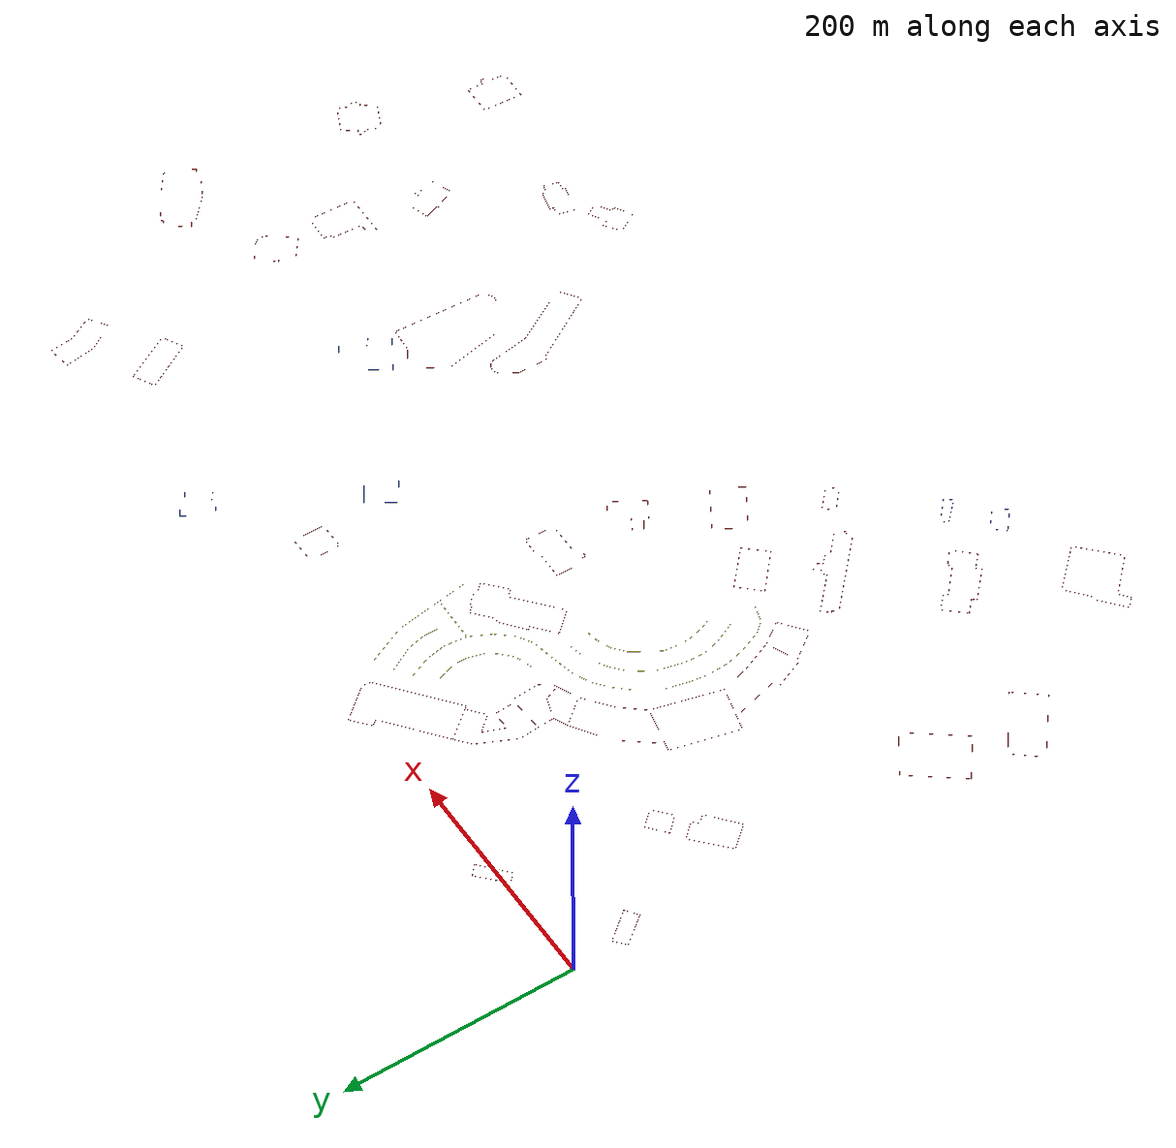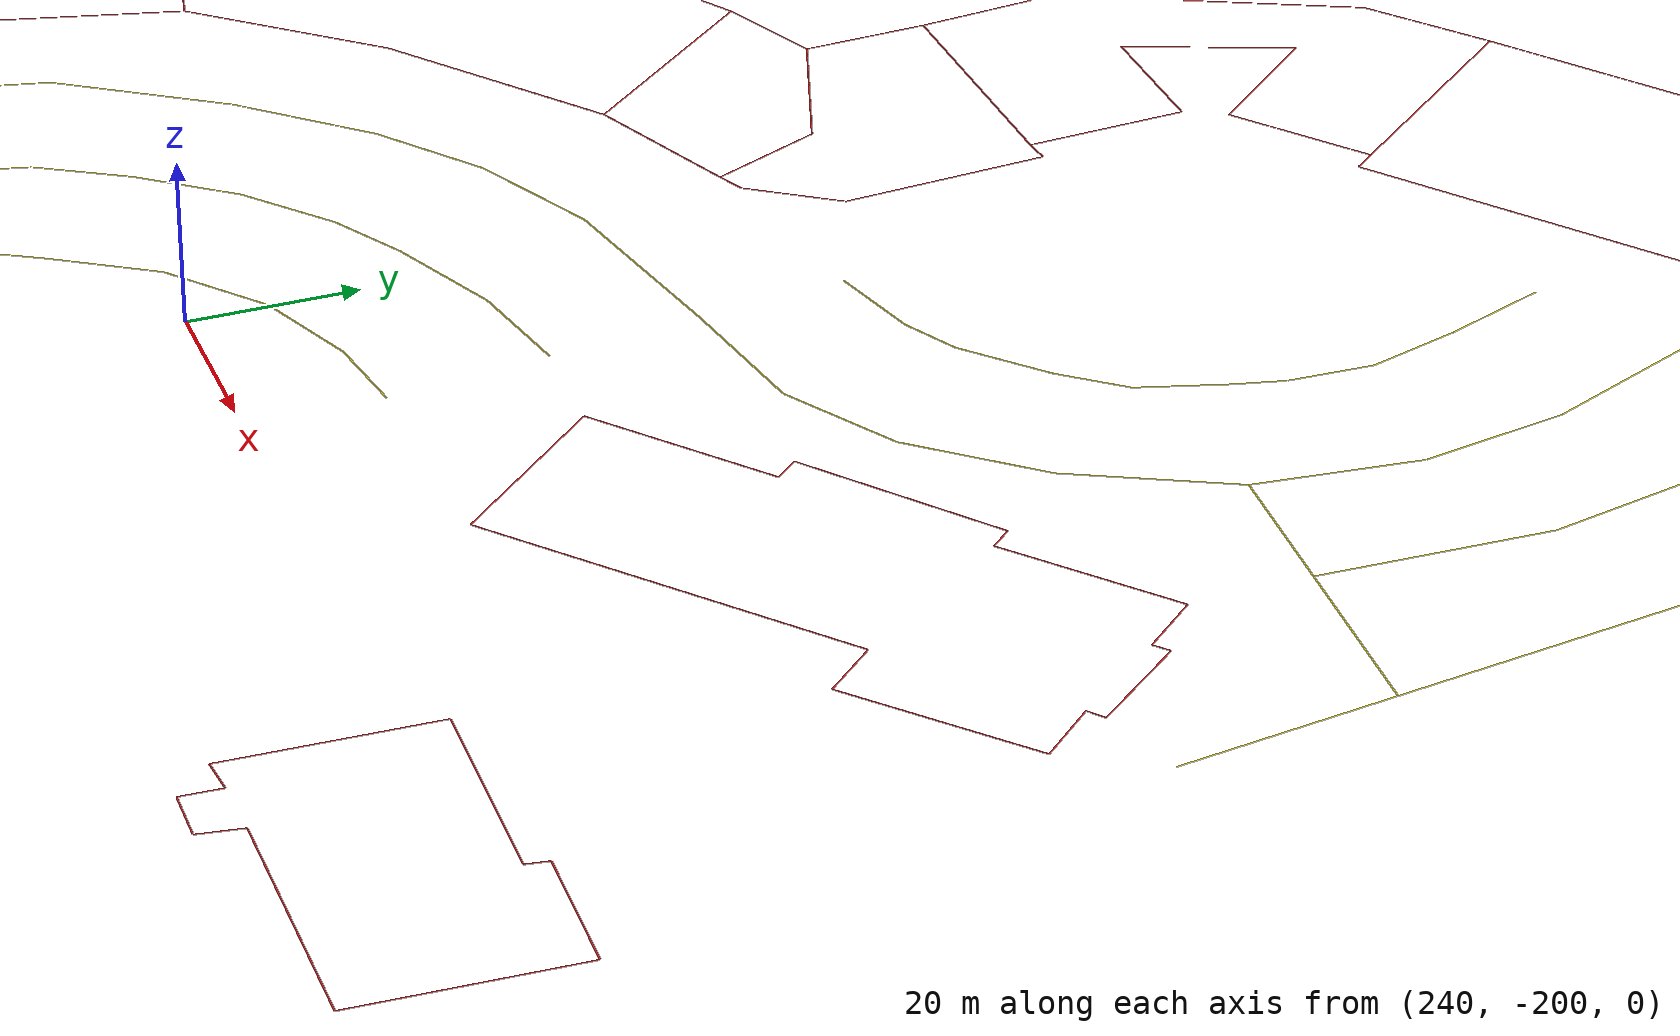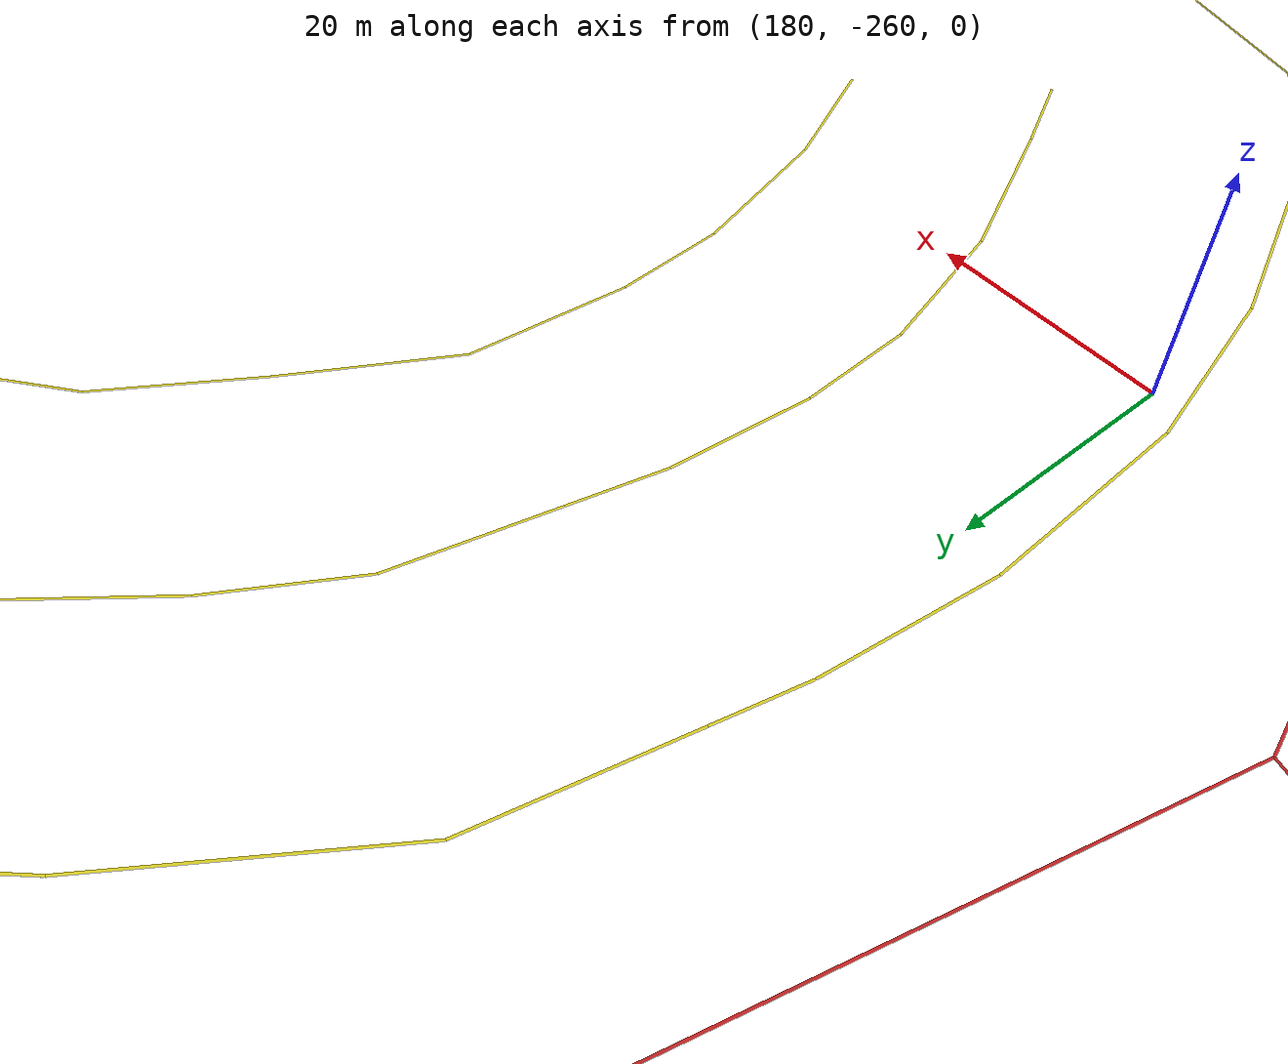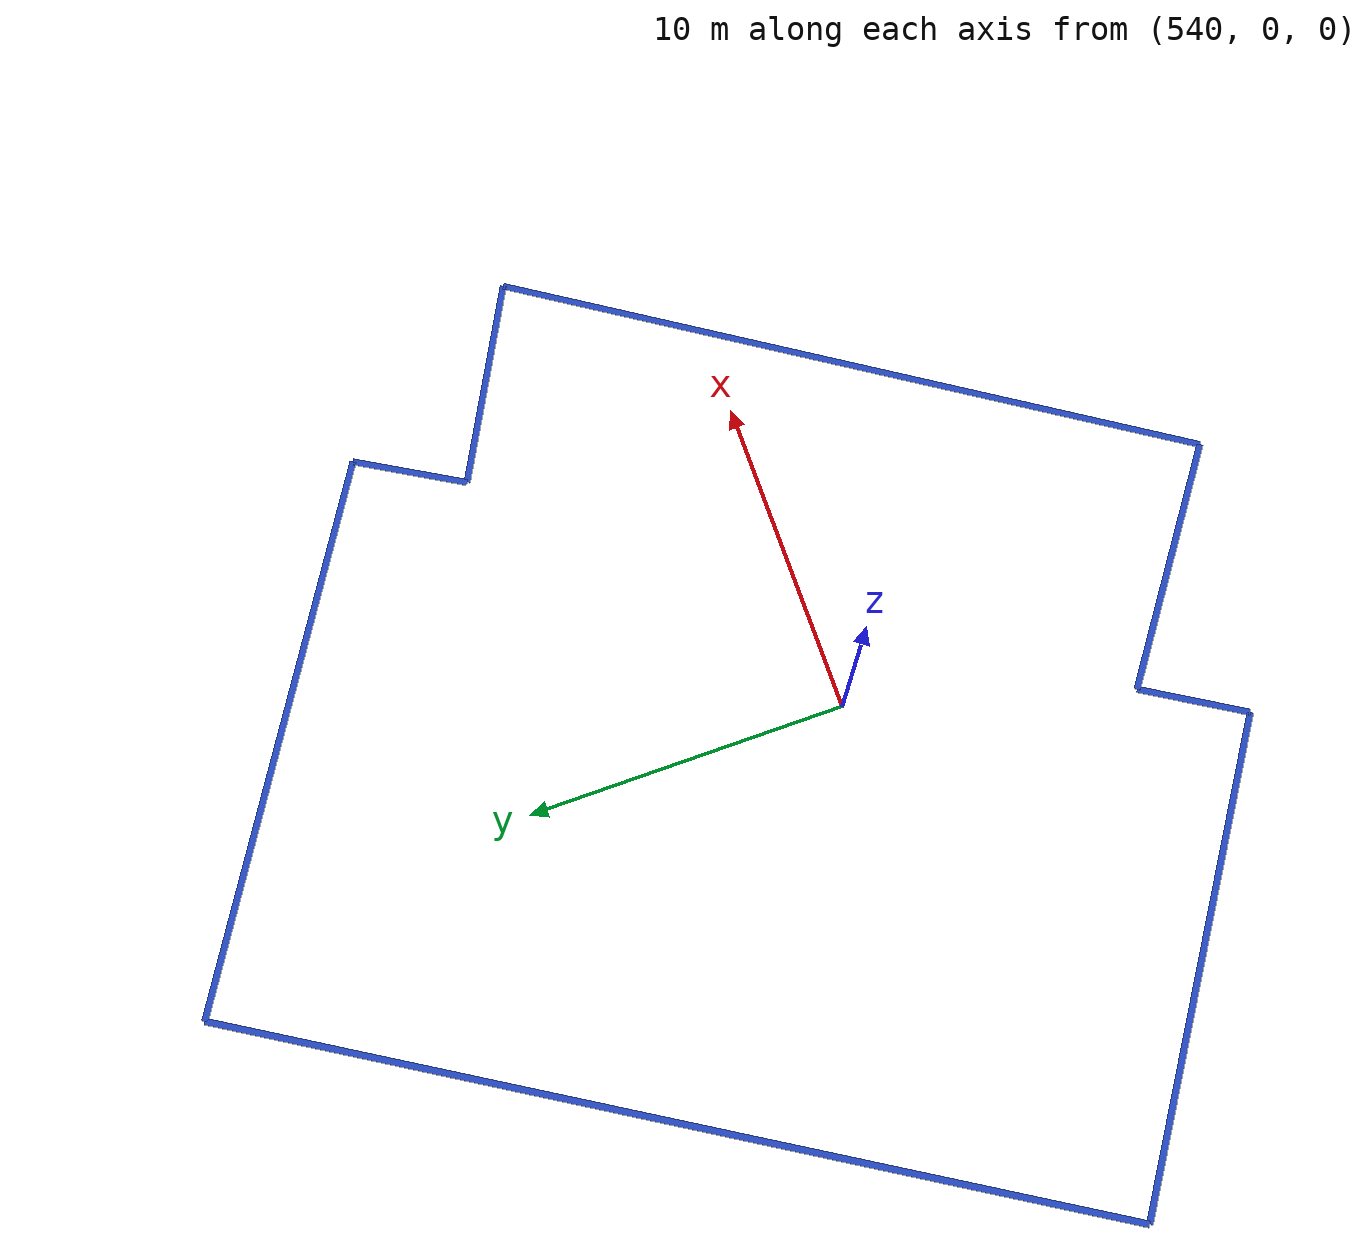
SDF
<sdf version="1.4">
 <world name="default">
  <spherical_coordinates>
   <surface_model>EARTH_WGS84</surface_model>
   <latitude_deg>33.39325</latitude_deg>
   <longitude_deg>-84.59399</longitude_deg>
   <elevation>0.0</elevation>
   <heading_deg>0</heading_deg>
  </spherical_coordinates>
  <include><uri>model://sun</uri></include>
  <model name="office_building_289242335">
   <static>true</static>
   <pose>343.145341733 -276.995207953 0.0 0 0 0</pose>
   <link name="office_building_289242335_0">
    <collision name="office_building_289242335_0">
     <geometry><box><size>17.6338927644 0.2 0</size></box></geometry>
    </collision>
    <visual name="office_building_289242335_0">
     <geometry><box><size>17.6338927644 0.2 0</size></box></geometry>
     <material>
      <script><uri>file://media/materials/scripts/gazebo.material</uri><name>Gazebo/Red</name></script>
     </material>
    </visual>
    <pose>14.1053484426 12.1612331397 0 0 0 -0.540218831163</pose>
   </link>
   <link name="office_building_289242335_1">
    <collision name="office_building_289242335_1">
     <geometry><box><size>18.614672145 0.2 0</size></box></geometry>
    </collision>
    <visual name="office_building_289242335_1">
     <geometry><box><size>18.614672145 0.2 0</size></box></geometry>
     <material>
      <script><uri>file://media/materials/scripts/gazebo.material</uri><name>Gazebo/Red</name></script>
     </material>
    </visual>
    <pose>1.55709475204 8.83739773491 0 0 0 1.00534090891</pose>
   </link>
   <link name="office_building_289242335_2">
    <collision name="office_building_289242335_2">
     <geometry><box><size>11.7677063694 0.2 0</size></box></geometry>
    </collision>
    <visual name="office_building_289242335_2">
     <geometry><box><size>11.7677063694 0.2 0</size></box></geometry>
     <material>
      <script><uri>file://media/materials/scripts/gazebo.material</uri><name>Gazebo/Red</name></script>
     </material>
    </visual>
    <pose>-8.56706633955 3.84724954283 0 0 0 -0.5092383873</pose>
   </link>
   <link name="office_building_289242335_3">
    <collision name="office_building_289242335_3">
     <geometry><box><size>8.97223625328 0.2 0</size></box></geometry>
    </collision>
    <visual name="office_building_289242335_3">
     <geometry><box><size>8.97223625328 0.2 0</size></box></geometry>
     <material>
      <script><uri>file://media/materials/scripts/gazebo.material</uri><name>Gazebo/Red</name></script>
     </material>
    </visual>
    <pose>-16.1227355342 2.93725133158 0 0 0 1.00145033255</pose>
   </link>
   <link name="office_building_289242335_4">
    <collision name="office_building_289242335_4">
     <geometry><box><size>12.1586680872 0.2 0</size></box></geometry>
    </collision>
    <visual name="office_building_289242335_4">
     <geometry><box><size>12.1586680872 0.2 0</size></box></geometry>
     <material>
      <script><uri>file://media/materials/scripts/gazebo.material</uri><name>Gazebo/Red</name></script>
     </material>
    </visual>
    <pose>-13.5539243764 -4.31771984411 0 0 0 2.5328225592</pose>
   </link>
   <link name="office_building_289242335_5">
    <collision name="office_building_289242335_5">
     <geometry><box><size>3.69089578935 0.2 0</size></box></geometry>
    </collision>
    <visual name="office_building_289242335_5">
     <geometry><box><size>3.69089578935 0.2 0</size></box></geometry>
     <material>
      <script><uri>file://media/materials/scripts/gazebo.material</uri><name>Gazebo/Red</name></script>
     </material>
    </visual>
    <pose>-9.62303768704 -9.30748075953 0 0 0 0.961384639227</pose>
   </link>
   <link name="office_building_289242335_6">
    <collision name="office_building_289242335_6">
     <geometry><box><size>18.3017159656 0.2 0</size></box></geometry>
    </collision>
    <visual name="office_building_289242335_6">
     <geometry><box><size>18.3017159656 0.2 0</size></box></geometry>
     <material>
      <script><uri>file://media/materials/scripts/gazebo.material</uri><name>Gazebo/Red</name></script>
     </material>
    </visual>
    <pose>-2.81772159209 -15.5039972855 0 0 0 2.60433075349</pose>
   </link>
   <link name="office_building_289242335_7">
    <collision name="office_building_289242335_7">
     <geometry><box><size>32.4025102245 0.2 0</size></box></geometry>
    </collision>
    <visual name="office_building_289242335_7">
     <geometry><box><size>32.4025102245 0.2 0</size></box></geometry>
     <material>
      <script><uri>file://media/materials/scripts/gazebo.material</uri><name>Gazebo/Red</name></script>
     </material>
    </visual>
    <pose>13.3553146037 -6.28040275404 0 0 0 -2.10948457299</pose>
   </link>
  </model>
  <model name="office_building_289242332">
   <static>true</static>
   <pose>311.738976313 -346.503149997 0.0 0 0 0</pose>
   <link name="office_building_289242332_0">
    <collision name="office_building_289242332_0">
     <geometry><box><size>42.8399060471 0.2 0</size></box></geometry>
    </collision>
    <visual name="office_building_289242332_0">
     <geometry><box><size>42.8399060471 0.2 0</size></box></geometry>
     <material>
      <script><uri>file://media/materials/scripts/gazebo.material</uri><name>Gazebo/Red</name></script>
     </material>
    </visual>
    <pose>2.37024662163 12.0417303831 0 0 0 -0.55021795317</pose>
   </link>
   <link name="office_building_289242332_1">
    <collision name="office_building_289242332_1">
     <geometry><box><size>28.5915512448 0.2 0</size></box></geometry>
    </collision>
    <visual name="office_building_289242332_1">
     <geometry><box><size>28.5915512448 0.2 0</size></box></geometry>
     <material>
      <script><uri>file://media/materials/scripts/gazebo.material</uri><name>Gazebo/Red</name></script>
     </material>
    </visual>
    <pose>-23.3268647899 11.0335475916 0 0 0 1.02355932555</pose>
   </link>
   <link name="office_building_289242332_2">
    <collision name="office_building_289242332_2">
     <geometry><box><size>42.6301835624 0.2 0</size></box></geometry>
    </collision>
    <visual name="office_building_289242332_2">
     <geometry><box><size>42.6301835624 0.2 0</size></box></geometry>
     <material>
      <script><uri>file://media/materials/scripts/gazebo.material</uri><name>Gazebo/Red</name></script>
     </material>
    </visual>
    <pose>-12.6846672277 -12.4626377375 0 0 0 2.58348505288</pose>
   </link>
   <link name="office_building_289242332_3">
    <collision name="office_building_289242332_3">
     <geometry><box><size>28.9280314655 0.2 0</size></box></geometry>
    </collision>
    <visual name="office_building_289242332_3">
     <geometry><box><size>28.9280314655 0.2 0</size></box></geometry>
     <material>
      <script><uri>file://media/materials/scripts/gazebo.material</uri><name>Gazebo/Red</name></script>
     </material>
    </visual>
    <pose>13.0124441838 -11.454454946 0 0 0 -2.1253636859</pose>
   </link>
  </model>
  <model name="office_building_289242333">
   <static>true</static>
   <pose>213.605715151 -379.046638468 0.0 0 0 0</pose>
   <link name="office_building_289242333_0">
    <collision name="office_building_289242333_0">
     <geometry><box><size>25.7217980841 0.2 0</size></box></geometry>
    </collision>
    <visual name="office_building_289242333_0">
     <geometry><box><size>25.7217980841 0.2 0</size></box></geometry>
     <material>
      <script><uri>file://media/materials/scripts/gazebo.material</uri><name>Gazebo/Red</name></script>
     </material>
    </visual>
    <pose>18.366076549 -15.4406419336 0 0 0 -0.734969119008</pose>
   </link>
   <link name="office_building_289242333_1">
    <collision name="office_building_289242333_1">
     <geometry><box><size>3.97115283461 0.2 0</size></box></geometry>
    </collision>
    <visual name="office_building_289242333_1">
     <geometry><box><size>3.97115283461 0.2 0</size></box></geometry>
     <material>
      <script><uri>file://media/materials/scripts/gazebo.material</uri><name>Gazebo/Red</name></script>
     </material>
    </visual>
    <pose>9.92596387683 -5.16405988727 0 0 0 -2.15841428691</pose>
   </link>
   <link name="office_building_289242333_2">
    <collision name="office_building_289242333_2">
     <geometry><box><size>8.70406953996 0.2 0</size></box></geometry>
    </collision>
    <visual name="office_building_289242333_2">
     <geometry><box><size>8.70406953996 0.2 0</size></box></geometry>
     <material>
      <script><uri>file://media/materials/scripts/gazebo.material</uri><name>Gazebo/Red</name></script>
     </material>
    </visual>
    <pose>7.9965435527 -0.387726886614 0 0 0 -0.800610788464</pose>
   </link>
   <link name="office_building_289242333_3">
    <collision name="office_building_289242333_3">
     <geometry><box><size>11.4907243861 0.2 0</size></box></geometry>
    </collision>
    <visual name="office_building_289242333_3">
     <geometry><box><size>11.4907243861 0.2 0</size></box></geometry>
     <material>
      <script><uri>file://media/materials/scripts/gazebo.material</uri><name>Gazebo/Red</name></script>
     </material>
    </visual>
    <pose>8.54666291681 7.2294795995 0 0 0 -2.24357830144</pose>
   </link>
   <link name="office_building_289242333_4">
    <collision name="office_building_289242333_4">
     <geometry><box><size>5.91099845738 0.2 0</size></box></geometry>
    </collision>
    <visual name="office_building_289242333_4">
     <geometry><box><size>5.91099845738 0.2 0</size></box></geometry>
     <material>
      <script><uri>file://media/materials/scripts/gazebo.material</uri><name>Gazebo/Red</name></script>
     </material>
    </visual>
    <pose>9.7417694847 13.4681009702 0 0 0 -0.631679350504</pose>
   </link>
   <link name="office_building_289242333_5">
    <collision name="office_building_289242333_5">
     <geometry><box><size>10.7838333885 0.2 0</size></box></geometry>
    </collision>
    <visual name="office_building_289242333_5">
     <geometry><box><size>10.7838333885 0.2 0</size></box></geometry>
     <material>
      <script><uri>file://media/materials/scripts/gazebo.material</uri><name>Gazebo/Red</name></script>
     </material>
    </visual>
    <pose>3.68173011129 11.2676572989 0 0 0 0.820922354455</pose>
   </link>
   <link name="office_building_289242333_6">
    <collision name="office_building_289242333_6">
     <geometry><box><size>3.38210886328 0.2 0</size></box></geometry>
    </collision>
    <visual name="office_building_289242333_6">
     <geometry><box><size>3.38210886328 0.2 0</size></box></geometry>
     <material>
      <script><uri>file://media/materials/scripts/gazebo.material</uri><name>Gazebo/Red</name></script>
     </material>
    </visual>
    <pose>-1.27745565575 8.42204626606 0 0 0 -0.708263323073</pose>
   </link>
   <link name="office_building_289242333_7">
    <collision name="office_building_289242333_7">
     <geometry><box><size>4.54273188868 0.2 0</size></box></geometry>
    </collision>
    <visual name="office_building_289242333_7">
     <geometry><box><size>4.54273188868 0.2 0</size></box></geometry>
     <material>
      <script><uri>file://media/materials/scripts/gazebo.material</uri><name>Gazebo/Red</name></script>
     </material>
    </visual>
    <pose>-4.21298402079 7.96239484504 0 0 0 0.756916667004</pose>
   </link>
   <link name="office_building_289242333_8">
    <collision name="office_building_289242333_8">
     <geometry><box><size>37.139260413 0.2 0</size></box></geometry>
    </collision>
    <visual name="office_building_289242333_8">
     <geometry><box><size>37.139260413 0.2 0</size></box></geometry>
     <material>
      <script><uri>file://media/materials/scripts/gazebo.material</uri><name>Gazebo/Red</name></script>
     </material>
    </visual>
    <pose>-19.4471007572 19.0650365684 0 0 0 -0.750336472054</pose>
   </link>
   <link name="office_building_289242333_9">
    <collision name="office_building_289242333_9">
     <geometry><box><size>8.96068470982 0.2 0</size></box></geometry>
    </collision>
    <visual name="office_building_289242333_9">
     <geometry><box><size>8.96068470982 0.2 0</size></box></geometry>
     <material>
      <script><uri>file://media/materials/scripts/gazebo.material</uri><name>Gazebo/Red</name></script>
     </material>
    </visual>
    <pose>-36.0599747349 28.4269450263 0 0 0 0.828102644443</pose>
   </link>
   <link name="office_building_289242333_10">
    <collision name="office_building_289242333_10">
     <geometry><box><size>1.69829934679 0.2 0</size></box></geometry>
    </collision>
    <visual name="office_building_289242333_10">
     <geometry><box><size>1.69829934679 0.2 0</size></box></geometry>
     <material>
      <script><uri>file://media/materials/scripts/gazebo.material</uri><name>Gazebo/Red</name></script>
     </material>
    </visual>
    <pose>-38.4449659149 24.5741500069 0 0 0 2.43337967471</pose>
   </link>
   <link name="office_building_289242333_11">
    <collision name="office_building_289242333_11">
     <geometry><box><size>5.45648890442 0.2 0</size></box></geometry>
    </collision>
    <visual name="office_building_289242333_11">
     <geometry><box><size>5.45648890442 0.2 0</size></box></geometry>
     <material>
      <script><uri>file://media/materials/scripts/gazebo.material</uri><name>Gazebo/Red</name></script>
     </material>
    </visual>
    <pose>-39.6346567714 22.0025380464 0 0 0 0.833265629062</pose>
   </link>
   <link name="office_building_289242333_12">
    <collision name="office_building_289242333_12">
     <geometry><box><size>79.7377841775 0.2 0</size></box></geometry>
    </collision>
    <visual name="office_building_289242333_12">
     <geometry><box><size>79.7377841775 0.2 0</size></box></geometry>
     <material>
      <script><uri>file://media/materials/scripts/gazebo.material</uri><name>Gazebo/Red</name></script>
     </material>
    </visual>
    <pose>-12.2851043829 -7.17940459039 0 0 0 2.39205528834</pose>
   </link>
   <link name="office_building_289242333_13">
    <collision name="office_building_289242333_13">
     <geometry><box><size>5.99332656118 0.2 0</size></box></geometry>
    </collision>
    <visual name="office_building_289242333_13">
     <geometry><box><size>5.99332656118 0.2 0</size></box></geometry>
     <material>
      <script><uri>file://media/materials/scripts/gazebo.material</uri><name>Gazebo/Red</name></script>
     </material>
    </visual>
    <pose>18.8282241321 -32.0489611056 0 0 0 -2.27019915235</pose>
   </link>
   <link name="office_building_289242333_14">
    <collision name="office_building_289242333_14">
     <geometry><box><size>1.94594424793 0.2 0</size></box></geometry>
    </collision>
    <visual name="office_building_289242333_14">
     <geometry><box><size>1.94594424793 0.2 0</size></box></geometry>
     <material>
      <script><uri>file://media/materials/scripts/gazebo.material</uri><name>Gazebo/Red</name></script>
     </material>
    </visual>
    <pose>21.3967604749 -30.4892098943 0 0 0 2.28784588362</pose>
   </link>
   <link name="office_building_289242333_15">
    <collision name="office_building_289242333_15">
     <geometry><box><size>9.25751035754 0.2 0</size></box></geometry>
    </collision>
    <visual name="office_building_289242333_15">
     <geometry><box><size>9.25751035754 0.2 0</size></box></geometry>
     <material>
      <script><uri>file://media/materials/scripts/gazebo.material</uri><name>Gazebo/Red</name></script>
     </material>
    </visual>
    <pose>24.9715578407 -27.6436433166 0 0 0 -2.25772469713</pose>
   </link>
  </model>
  <model name="office_building_289242331">
   <static>true</static>
   <pose>248.93098129 -327.817578953 0.0 0 0 0</pose>
   <link name="office_building_289242331_0">
    <collision name="office_building_289242331_0">
     <geometry><box><size>39.8998555635 0.2 0</size></box></geometry>
    </collision>
    <visual name="office_building_289242331_0">
     <geometry><box><size>39.8998555635 0.2 0</size></box></geometry>
     <material>
      <script><uri>file://media/materials/scripts/gazebo.material</uri><name>Gazebo/Red</name></script>
     </material>
    </visual>
    <pose>3.5979393788 9.7812924144 0 0 0 -0.729923029131</pose>
   </link>
   <link name="office_building_289242331_1">
    <collision name="office_building_289242331_1">
     <geometry><box><size>24.5358813129 0.2 0</size></box></geometry>
    </collision>
    <visual name="office_building_289242331_1">
     <geometry><box><size>24.5358813129 0.2 0</size></box></geometry>
     <material>
      <script><uri>file://media/materials/scripts/gazebo.material</uri><name>Gazebo/Red</name></script>
     </material>
    </visual>
    <pose>-19.7142260107 14.1855583344 0 0 0 0.811547444255</pose>
   </link>
   <link name="office_building_289242331_2">
    <collision name="office_building_289242331_2">
     <geometry><box><size>40.598398462 0.2 0</size></box></geometry>
    </collision>
    <visual name="office_building_289242331_2">
     <geometry><box><size>40.598398462 0.2 0</size></box></geometry>
     <material>
      <script><uri>file://media/materials/scripts/gazebo.material</uri><name>Gazebo/Red</name></script>
     </material>
    </visual>
    <pose>-12.8305088122 -8.02051024345 0 0 0 2.4266599033</pose>
   </link>
   <link name="office_building_289242331_3">
    <collision name="office_building_289242331_3">
     <geometry><box><size>23.9167865907 0.2 0</size></box></geometry>
    </collision>
    <visual name="office_building_289242331_3">
     <geometry><box><size>23.9167865907 0.2 0</size></box></geometry>
     <material>
      <script><uri>file://media/materials/scripts/gazebo.material</uri><name>Gazebo/Red</name></script>
     </material>
    </visual>
    <pose>10.4816565773 -12.4247761634 0 0 0 -2.30178350188</pose>
   </link>
  </model>
  <model name="Smokey Bones Bar and Grill">
   <static>true</static>
   <pose>456.98906086 -52.4046080895 0.0 0 0 0</pose>
   <link name="Smokey Bones Bar and Grill_0">
    <collision name="Smokey Bones Bar and Grill_0">
     <geometry><box><size>24.902365744 0.2 0</size></box></geometry>
    </collision>
    <visual name="Smokey Bones Bar and Grill_0">
     <geometry><box><size>24.902365744 0.2 0</size></box></geometry>
     <material>
      <script><uri>file://media/materials/scripts/gazebo.material</uri><name>Gazebo/Red</name></script>
     </material>
    </visual>
    <pose>-2.65206088 10.8243966605 0 0 0 0.021627846046</pose>
   </link>
   <link name="Smokey Bones Bar and Grill_1">
    <collision name="Smokey Bones Bar and Grill_1">
     <geometry><box><size>27.0732267006 0.2 0</size></box></geometry>
    </collision>
    <visual name="Smokey Bones Bar and Grill_1">
     <geometry><box><size>27.0732267006 0.2 0</size></box></geometry>
     <material>
      <script><uri>file://media/materials/scripts/gazebo.material</uri><name>Gazebo/Red</name></script>
     </material>
    </visual>
    <pose>-14.6943927386 -2.97539989771 0 0 0 1.60078904937</pose>
   </link>
   <link name="Smokey Bones Bar and Grill_2">
    <collision name="Smokey Bones Bar and Grill_2">
     <geometry><box><size>24.086325709 0.2 0</size></box></geometry>
    </collision>
    <visual name="Smokey Bones Bar and Grill_2">
     <geometry><box><size>24.086325709 0.2 0</size></box></geometry>
     <material>
      <script><uri>file://media/materials/scripts/gazebo.material</uri><name>Gazebo/Red</name></script>
     </material>
    </visual>
    <pose>-2.24604411984 -16.371230627 0 0 0 -3.13040810296</pose>
   </link>
   <link name="Smokey Bones Bar and Grill_3">
    <collision name="Smokey Bones Bar and Grill_3">
     <geometry><box><size>27.3302040042 0.2 0</size></box></geometry>
    </collision>
    <visual name="Smokey Bones Bar and Grill_3">
     <geometry><box><size>27.3302040042 0.2 0</size></box></geometry>
     <material>
      <script><uri>file://media/materials/scripts/gazebo.material</uri><name>Gazebo/Red</name></script>
     </material>
    </visual>
    <pose>9.79628773873 -2.57143406881 0 0 0 -1.57079063792</pose>
   </link>
  </model>
  <model name="office_building_289326070">
   <static>true</static>
   <pose>736.416937843 -250.580365527 0.0 0 0 0</pose>
   <link name="office_building_289326070_0">
    <collision name="office_building_289326070_0">
     <geometry><box><size>35.681275466 0.2 0</size></box></geometry>
    </collision>
    <visual name="office_building_289326070_0">
     <geometry><box><size>35.681275466 0.2 0</size></box></geometry>
     <material>
      <script><uri>file://media/materials/scripts/gazebo.material</uri><name>Gazebo/Red</name></script>
     </material>
    </visual>
    <pose>17.1767037193 -4.56049760745 0 0 0 -1.60817470538</pose>
   </link>
   <link name="office_building_289326070_1">
    <collision name="office_building_289326070_1">
     <geometry><box><size>3.56520579582 0.2 0</size></box></geometry>
    </collision>
    <visual name="office_building_289326070_1">
     <geometry><box><size>3.56520579582 0.2 0</size></box></geometry>
     <material>
      <script><uri>file://media/materials/scripts/gazebo.material</uri><name>Gazebo/Red</name></script>
     </material>
    </visual>
    <pose>16.0642864702 13.1562379043 0 0 0 0.0625565158895</pose>
   </link>
   <link name="office_building_289326070_2">
    <collision name="office_building_289326070_2">
     <geometry><box><size>6.0247218959 0.2 0</size></box></geometry>
    </collision>
    <visual name="office_building_289326070_2">
     <geometry><box><size>6.0247218959 0.2 0</size></box></geometry>
     <material>
      <script><uri>file://media/materials/scripts/gazebo.material</uri><name>Gazebo/Red</name></script>
     </material>
    </visual>
    <pose>14.2850972722 16.0571581419 0 0 0 -1.57077205727</pose>
   </link>
   <link name="office_building_289326070_3">
    <collision name="office_building_289326070_3">
     <geometry><box><size>20.9787210335 0.2 0</size></box></geometry>
    </collision>
    <visual name="office_building_289326070_3">
     <geometry><box><size>20.9787210335 0.2 0</size></box></geometry>
     <material>
      <script><uri>file://media/materials/scripts/gazebo.material</uri><name>Gazebo/Red</name></script>
     </material>
    </visual>
    <pose>3.81044876249 19.6262544093 0 0 0 -0.0531011443699</pose>
   </link>
   <link name="office_building_289326070_4">
    <collision name="office_building_289326070_4">
     <geometry><box><size>6.70788059769 0.2 0</size></box></geometry>
    </collision>
    <visual name="office_building_289326070_4">
     <geometry><box><size>6.70788059769 0.2 0</size></box></geometry>
     <material>
      <script><uri>file://media/materials/scripts/gazebo.material</uri><name>Gazebo/Red</name></script>
     </material>
    </visual>
    <pose>-6.44165583593 16.8364359395 0 0 0 1.63717623981</pose>
   </link>
   <link name="office_building_289326070_5">
    <collision name="office_building_289326070_5">
     <geometry><box><size>3.85020544762 0.2 0</size></box></geometry>
    </collision>
    <visual name="office_building_289326070_5">
     <geometry><box><size>3.85020544762 0.2 0</size></box></geometry>
     <material>
      <script><uri>file://media/materials/scripts/gazebo.material</uri><name>Gazebo/Red</name></script>
     </material>
    </visual>
    <pose>-8.11506672021 13.8240275165 0 0 0 -0.174456330886</pose>
   </link>
   <link name="office_building_289326070_6">
    <collision name="office_building_289326070_6">
     <geometry><box><size>27.658736078 0.2 0</size></box></geometry>
    </collision>
    <visual name="office_building_289326070_6">
     <geometry><box><size>27.658736078 0.2 0</size></box></geometry>
     <material>
      <script><uri>file://media/materials/scripts/gazebo.material</uri><name>Gazebo/Red</name></script>
     </material>
    </visual>
    <pose>-10.6777602674 0.344890062201 0 0 0 1.52256053568</pose>
   </link>
   <link name="office_building_289326070_7">
    <collision name="office_building_289326070_7">
     <geometry><box><size>11.3641215068 0.2 0</size></box></geometry>
    </collision>
    <visual name="office_building_289326070_7">
     <geometry><box><size>11.3641215068 0.2 0</size></box></geometry>
     <material>
      <script><uri>file://media/materials/scripts/gazebo.material</uri><name>Gazebo/Red</name></script>
     </material>
    </visual>
    <pose>-17.0266328788 -13.4685480292 0 0 0 2.73263715815e-05</pose>
   </link>
   <link name="office_building_289326070_8">
    <collision name="office_building_289326070_8">
     <geometry><box><size>8.0329777955 0.2 0</size></box></geometry>
    </collision>
    <visual name="office_building_289326070_8">
     <geometry><box><size>8.0329777955 0.2 0</size></box></geometry>
     <material>
      <script><uri>file://media/materials/scripts/gazebo.material</uri><name>Gazebo/Red</name></script>
     </material>
    </visual>
    <pose>-22.5973873275 -17.4836496218 0 0 0 1.59851221424</pose>
   </link>
   <link name="office_building_289326070_9">
    <collision name="office_building_289326070_9">
     <geometry><box><size>39.0062425062 0.2 0</size></box></geometry>
    </collision>
    <visual name="office_building_289326070_9">
     <geometry><box><size>39.0062425062 0.2 0</size></box></geometry>
     <material>
      <script><uri>file://media/materials/scripts/gazebo.material</uri><name>Gazebo/Red</name></script>
     </material>
    </visual>
    <pose>-2.9880380731 -21.9436348865 0 0 0 3.11877181546</pose>
   </link>
  </model>
  <model name="office_building_289326073">
   <static>true</static>
   <pose>743.875920288 -190.049008993 0.0 0 0 0</pose>
   <link name="office_building_289326073_0">
    <collision name="office_building_289326073_0">
     <geometry><box><size>14.5882097305 0.2 0</size></box></geometry>
    </collision>
    <visual name="office_building_289326073_0">
     <geometry><box><size>14.5882097305 0.2 0</size></box></geometry>
     <material>
      <script><uri>file://media/materials/scripts/gazebo.material</uri><name>Gazebo/Red</name></script>
     </material>
    </visual>
    <pose>-6.44066488787 13.1317375355 0 0 0 0.969689571873</pose>
   </link>
   <link name="office_building_289326073_1">
    <collision name="office_building_289326073_1">
     <geometry><box><size>2.39581355726 0.2 0</size></box></geometry>
    </collision>
    <visual name="office_building_289326073_1">
     <geometry><box><size>2.39581355726 0.2 0</size></box></geometry>
     <material>
      <script><uri>file://media/materials/scripts/gazebo.material</uri><name>Gazebo/Red</name></script>
     </material>
    </visual>
    <pose>-11.6778442159 7.56178284873 0 0 0 -0.381114693525</pose>
   </link>
   <link name="office_building_289326073_2">
    <collision name="office_building_289326073_2">
     <geometry><box><size>5.05444341722 0.2 0</size></box></geometry>
    </collision>
    <visual name="office_building_289326073_2">
     <geometry><box><size>5.05444341722 0.2 0</size></box></geometry>
     <material>
      <script><uri>file://media/materials/scripts/gazebo.material</uri><name>Gazebo/Red</name></script>
     </material>
    </visual>
    <pose>-14.4632494964 6.11356547921 0 0 0 0.847086906871</pose>
   </link>
   <link name="office_building_289326073_3">
    <collision name="office_building_289326073_3">
     <geometry><box><size>2.30034938425 0.2 0</size></box></geometry>
    </collision>
    <visual name="office_building_289326073_3">
     <geometry><box><size>2.30034938425 0.2 0</size></box></geometry>
     <material>
      <script><uri>file://media/materials/scripts/gazebo.material</uri><name>Gazebo/Red</name></script>
     </material>
    </visual>
    <pose>-15.1303722664 3.66281326694 0 0 0 2.6360920339</pose>
   </link>
   <link name="office_building_289326073_4">
    <collision name="office_building_289326073_4">
     <geometry><box><size>13.9696616832 0.2 0</size></box></geometry>
    </collision>
    <visual name="office_building_289326073_4">
     <geometry><box><size>13.9696616832 0.2 0</size></box></geometry>
     <material>
      <script><uri>file://media/materials/scripts/gazebo.material</uri><name>Gazebo/Red</name></script>
     </material>
    </visual>
    <pose>-18.0268738267 -2.68689118981 0 0 0 0.977909519251</pose>
   </link>
   <link name="office_building_289326073_5">
    <collision name="office_building_289326073_5">
     <geometry><box><size>24.6983197397 0.2 0</size></box></geometry>
    </collision>
    <visual name="office_building_289326073_5">
     <geometry><box><size>24.6983197397 0.2 0</size></box></geometry>
     <material>
      <script><uri>file://media/materials/scripts/gazebo.material</uri><name>Gazebo/Red</name></script>
     </material>
    </visual>
    <pose>-12.010956016 -15.836276254 0 0 0 2.50343027265</pose>
   </link>
   <link name="office_building_289326073_6">
    <collision name="office_building_289326073_6">
     <geometry><box><size>13.6370267705 0.2 0</size></box></geometry>
    </collision>
    <visual name="office_building_289326073_6">
     <geometry><box><size>13.6370267705 0.2 0</size></box></geometry>
     <material>
      <script><uri>file://media/materials/scripts/gazebo.material</uri><name>Gazebo/Red</name></script>
     </material>
    </visual>
    <pose>2.13864010678 -17.8457734476 0 0 0 -2.24016979257</pose>
   </link>
   <link name="office_building_289326073_7">
    <collision name="office_building_289326073_7">
     <geometry><box><size>4.5148025706 0.2 0</size></box></geometry>
    </collision>
    <visual name="office_building_289326073_7">
     <geometry><box><size>4.5148025706 0.2 0</size></box></geometry>
     <material>
      <script><uri>file://media/materials/scripts/gazebo.material</uri><name>Gazebo/Red</name></script>
     </material>
    </visual>
    <pose>8.26539136826 -13.7239501054 0 0 0 2.56782018613</pose>
   </link>
   <link name="office_building_289326073_8">
    <collision name="office_building_289326073_8">
     <geometry><box><size>7.30812960657 0.2 0</size></box></geometry>
    </collision>
    <visual name="office_building_289326073_8">
     <geometry><box><size>7.30812960657 0.2 0</size></box></geometry>
     <material>
      <script><uri>file://media/materials/scripts/gazebo.material</uri><name>Gazebo/Red</name></script>
     </material>
    </visual>
    <pose>12.0570989485 -11.8254812268 0 0 0 -2.11626842302</pose>
   </link>
   <link name="office_building_289326073_9">
    <collision name="office_building_289326073_9">
     <geometry><box><size>4.20761487227 0.2 0</size></box></geometry>
    </collision>
    <visual name="office_building_289326073_9">
     <geometry><box><size>4.20761487227 0.2 0</size></box></geometry>
     <material>
      <script><uri>file://media/materials/scripts/gazebo.material</uri><name>Gazebo/Red</name></script>
     </material>
    </visual>
    <pose>12.1682058338 -7.58775231574 0 0 0 -0.557992555555</pose>
   </link>
   <link name="office_building_289326073_10">
    <collision name="office_building_289326073_10">
     <geometry><box><size>6.6487740112 0.2 0</size></box></geometry>
    </collision>
    <visual name="office_building_289326073_10">
     <geometry><box><size>6.6487740112 0.2 0</size></box></geometry>
     <material>
      <script><uri>file://media/materials/scripts/gazebo.material</uri><name>Gazebo/Red</name></script>
     </material>
    </visual>
    <pose>12.5017164034 -3.91164692475 0 0 0 -2.26162190234</pose>
   </link>
   <link name="office_building_289326073_11">
    <collision name="office_building_289326073_11">
     <geometry><box><size>6.47631283652 0.2 0</size></box></geometry>
    </collision>
    <visual name="office_building_289326073_11">
     <geometry><box><size>6.47631283652 0.2 0</size></box></geometry>
     <material>
      <script><uri>file://media/materials/scripts/gazebo.material</uri><name>Gazebo/Red</name></script>
     </material>
    </visual>
    <pose>14.842255276 1.88104052053 0 0 0 -1.63950887933</pose>
   </link>
   <link name="office_building_289326073_12">
    <collision name="office_building_289326073_12">
     <geometry><box><size>5.75257825294 0.2 0</size></box></geometry>
    </collision>
    <visual name="office_building_289326073_12">
     <geometry><box><size>5.75257825294 0.2 0</size></box></geometry>
     <material>
      <script><uri>file://media/materials/scripts/gazebo.material</uri><name>Gazebo/Red</name></script>
     </material>
    </visual>
    <pose>13.3910543729 7.45085970648 0 0 0 -0.949812305177</pose>
   </link>
   <link name="office_building_289326073_13">
    <collision name="office_building_289326073_13">
     <geometry><box><size>16.8665198574 0.2 0</size></box></geometry>
    </collision>
    <visual name="office_building_289326073_13">
     <geometry><box><size>16.8665198574 0.2 0</size></box></geometry>
     <material>
      <script><uri>file://media/materials/scripts/gazebo.material</uri><name>Gazebo/Red</name></script>
     </material>
    </visual>
    <pose>4.70104164087 14.4687119712 0 0 0 -0.588090569092</pose>
   </link>
  </model>
  <model name="office_building_289242318">
   <static>true</static>
   <pose>277.276967872 -17.7924730716 0.0 0 0 0</pose>
   <link name="office_building_289242318_0">
    <collision name="office_building_289242318_0">
     <geometry><box><size>35.0213278969 0.2 0</size></box></geometry>
    </collision>
    <visual name="office_building_289242318_0">
     <geometry><box><size>35.0213278969 0.2 0</size></box></geometry>
     <material>
      <script><uri>file://media/materials/scripts/gazebo.material</uri><name>Gazebo/Red</name></script>
     </material>
    </visual>
    <pose>24.7117834945 21.4084180892 0 0 0 2.27829541252</pose>
   </link>
   <link name="office_building_289242318_1">
    <collision name="office_building_289242318_1">
     <geometry><box><size>7.58527878408 0.2 0</size></box></geometry>
    </collision>
    <visual name="office_building_289242318_1">
     <geometry><box><size>7.58527878408 0.2 0</size></box></geometry>
     <material>
      <script><uri>file://media/materials/scripts/gazebo.material</uri><name>Gazebo/Red</name></script>
     </material>
    </visual>
    <pose>35.6311255535 4.33603215976 0 0 0 1.44882324864</pose>
   </link>
   <link name="office_building_289242318_2">
    <collision name="office_building_289242318_2">
     <geometry><box><size>77.3629534005 0.2 0</size></box></geometry>
    </collision>
    <visual name="office_building_289242318_2">
     <geometry><box><size>77.3629534005 0.2 0</size></box></geometry>
     <material>
      <script><uri>file://media/materials/scripts/gazebo.material</uri><name>Gazebo/Red</name></script>
     </material>
    </visual>
    <pose>5.16382605489 -23.8396128747 0 0 0 0.682947240672</pose>
   </link>
   <link name="office_building_289242318_3">
    <collision name="office_building_289242318_3">
     <geometry><box><size>3.07860226014 0.2 0</size></box></geometry>
    </collision>
    <visual name="office_building_289242318_3">
     <geometry><box><size>3.07860226014 0.2 0</size></box></geometry>
     <material>
      <script><uri>file://media/materials/scripts/gazebo.material</uri><name>Gazebo/Red</name></script>
     </material>
    </visual>
    <pose>-25.8316625 -47.0717899123 0 0 0 -0.872495795368</pose>
   </link>
   <link name="office_building_289242318_4">
    <collision name="office_building_289242318_4">
     <geometry><box><size>30.6719300731 0.2 0</size></box></geometry>
    </collision>
    <visual name="office_building_289242318_4">
     <geometry><box><size>30.6719300731 0.2 0</size></box></geometry>
     <material>
      <script><uri>file://media/materials/scripts/gazebo.material</uri><name>Gazebo/Red</name></script>
     </material>
    </visual>
    <pose>-36.662119464 -34.1305477436 0 0 0 -0.874106898136</pose>
   </link>
   <link name="office_building_289242318_5">
    <collision name="office_building_289242318_5">
     <geometry><box><size>62.2616963315 0.2 0</size></box></geometry>
    </collision>
    <visual name="office_building_289242318_5">
     <geometry><box><size>62.2616963315 0.2 0</size></box></geometry>
     <material>
      <script><uri>file://media/materials/scripts/gazebo.material</uri><name>Gazebo/Red</name></script>
     </material>
    </visual>
    <pose>-22.2736008454 -2.82172266421 0 0 0 -2.46276002213</pose>
   </link>
   <link name="office_building_289242318_6">
    <collision name="office_building_289242318_6">
     <geometry><box><size>6.16771019823 0.2 0</size></box></geometry>
    </collision>
    <visual name="office_building_289242318_6">
     <geometry><box><size>6.16771019823 0.2 0</size></box></geometry>
     <material>
      <script><uri>file://media/materials/scripts/gazebo.material</uri><name>Gazebo/Red</name></script>
     </material>
    </visual>
    <pose>0.121016049056 19.2035715123 0 0 0 -0.933602433624</pose>
   </link>
   <link name="office_building_289242318_7">
    <collision name="office_building_289242318_7">
     <geometry><box><size>19.9055138762 0.2 0</size></box></geometry>
    </collision>
    <visual name="office_building_289242318_7">
     <geometry><box><size>19.9055138762 0.2 0</size></box></geometry>
     <material>
      <script><uri>file://media/materials/scripts/gazebo.material</uri><name>Gazebo/Red</name></script>
     </material>
    </visual>
    <pose>5.80864392619 28.1993094 0 0 0 -2.42767901797</pose>
   </link>
  </model>
  <model name="office_building_289242319">
   <static>true</static>
   <pose>227.794218223 -72.8567557991 0.0 0 0 0</pose>
   <link name="office_building_289242319_0">
    <collision name="office_building_289242319_0">
     <geometry><box><size>18.2542394732 0.2 0</size></box></geometry>
    </collision>
    <visual name="office_building_289242319_0">
     <geometry><box><size>18.2542394732 0.2 0</size></box></geometry>
     <material>
      <script><uri>file://media/materials/scripts/gazebo.material</uri><name>Gazebo/Red</name></script>
     </material>
    </visual>
    <pose>15.6506463091 3.32743988058 0 0 0 0.694883654133</pose>
   </link>
   <link name="office_building_289242319_1">
    <collision name="office_building_289242319_1">
     <geometry><box><size>17.773722933 0.2 0</size></box></geometry>
    </collision>
    <visual name="office_building_289242319_1">
     <geometry><box><size>17.773722933 0.2 0</size></box></geometry>
     <material>
      <script><uri>file://media/materials/scripts/gazebo.material</uri><name>Gazebo/Red</name></script>
     </material>
    </visual>
    <pose>2.74646981718 4.13502716794 0 0 0 -0.84576842435</pose>
   </link>
   <link name="office_building_289242319_2">
    <collision name="office_building_289242319_2">
     <geometry><box><size>20.3868220463 0.2 0</size></box></geometry>
    </collision>
    <visual name="office_building_289242319_2">
     <geometry><box><size>20.3868220463 0.2 0</size></box></geometry>
     <material>
      <script><uri>file://media/materials/scripts/gazebo.material</uri><name>Gazebo/Red</name></script>
     </material>
    </visual>
    <pose>-6.77735238635 1.2616796398 0 0 0 1.2066455023</pose>
   </link>
   <link name="office_building_289242319_3">
    <collision name="office_building_289242319_3">
     <geometry><box><size>16.6485188182 0.2 0</size></box></geometry>
    </collision>
    <visual name="office_building_289242319_3">
     <geometry><box><size>16.6485188182 0.2 0</size></box></geometry>
     <material>
      <script><uri>file://media/materials/scripts/gazebo.material</uri><name>Gazebo/Red</name></script>
     </material>
    </visual>
    <pose>-2.09597920788 -7.80834888548 0 0 0 -3.08691006482</pose>
   </link>
   <link name="office_building_289242319_4">
    <collision name="office_building_289242319_4">
     <geometry><box><size>19.0884247039 0.2 0</size></box></geometry>
    </collision>
    <visual name="office_building_289242319_4">
     <geometry><box><size>19.0884247039 0.2 0</size></box></geometry>
     <material>
      <script><uri>file://media/materials/scripts/gazebo.material</uri><name>Gazebo/Red</name></script>
     </material>
    </visual>
    <pose>6.8219385546 -16.8783314833 0 0 0 1.63434362587</pose>
   </link>
   <link name="office_building_289242319_5">
    <collision name="office_building_289242319_5">
     <geometry><box><size>30.4656449996 0.2 0</size></box></geometry>
    </collision>
    <visual name="office_building_289242319_5">
     <geometry><box><size>30.4656449996 0.2 0</size></box></geometry>
     <material>
      <script><uri>file://media/materials/scripts/gazebo.material</uri><name>Gazebo/Red</name></script>
     </material>
    </visual>
    <pose>-7.77785749027 -27.3085873773 0 0 0 0.0594664479947</pose>
   </link>
   <link name="office_building_289242319_6">
    <collision name="office_building_289242319_6">
     <geometry><box><size>17.1435220486 0.2 0</size></box></geometry>
    </collision>
    <visual name="office_building_289242319_6">
     <geometry><box><size>17.1435220486 0.2 0</size></box></geometry>
     <material>
      <script><uri>file://media/materials/scripts/gazebo.material</uri><name>Gazebo/Red</name></script>
     </material>
    </visual>
    <pose>-23.8122382248 -19.6822659624 0 0 0 -1.47399250061</pose>
   </link>
   <link name="office_building_289242319_7">
    <collision name="office_building_289242319_7">
     <geometry><box><size>36.5517976978 0.2 0</size></box></geometry>
    </collision>
    <visual name="office_building_289242319_7">
     <geometry><box><size>36.5517976978 0.2 0</size></box></geometry>
     <material>
      <script><uri>file://media/materials/scripts/gazebo.material</uri><name>Gazebo/Red</name></script>
     </material>
    </visual>
    <pose>-17.023985499 5.46242469754 0 0 0 -2.000678826</pose>
   </link>
   <link name="office_building_289242319_8">
    <collision name="office_building_289242319_8">
     <geometry><box><size>16.316681124 0.2 0</size></box></geometry>
    </collision>
    <visual name="office_building_289242319_8">
     <geometry><box><size>16.316681124 0.2 0</size></box></geometry>
     <material>
      <script><uri>file://media/materials/scripts/gazebo.material</uri><name>Gazebo/Red</name></script>
     </material>
    </visual>
    <pose>-3.21371644711 27.3857285119 0 0 0 -2.43282673294</pose>
   </link>
   <link name="office_building_289242319_9">
    <collision name="office_building_289242319_9">
     <geometry><box><size>30.6719300731 0.2 0</size></box></geometry>
    </collision>
    <visual name="office_building_289242319_9">
     <geometry><box><size>30.6719300731 0.2 0</size></box></geometry>
     <material>
      <script><uri>file://media/materials/scripts/gazebo.material</uri><name>Gazebo/Red</name></script>
     </material>
    </visual>
    <pose>12.8206301854 20.9337349838 0 0 0 2.26748575545</pose>
   </link>
  </model>
  <model name="office_building_289326076">
   <static>true</static>
   <pose>665.340739958 -415.331402557 0.0 0 0 0</pose>
   <link name="office_building_289326076_0">
    <collision name="office_building_289326076_0">
     <geometry><box><size>7.90399744248 0.2 0</size></box></geometry>
    </collision>
    <visual name="office_building_289326076_0">
     <geometry><box><size>7.90399744248 0.2 0</size></box></geometry>
     <material>
      <script><uri>file://media/materials/scripts/gazebo.material</uri><name>Gazebo/Red</name></script>
     </material>
    </visual>
    <pose>11.0223463499 2.33307545762 0 0 0 -0.285707446526</pose>
   </link>
   <link name="office_building_289326076_1">
    <collision name="office_building_289326076_1">
     <geometry><box><size>3.40788211875 0.2 0</size></box></geometry>
    </collision>
    <visual name="office_building_289326076_1">
     <geometry><box><size>3.40788211875 0.2 0</size></box></geometry>
     <material>
      <script><uri>file://media/materials/scripts/gazebo.material</uri><name>Gazebo/Red</name></script>
     </material>
    </visual>
    <pose>7.56406558934 5.11787495491 0 0 0 -1.7677989957</pose>
   </link>
   <link name="office_building_289326076_2">
    <collision name="office_building_289326076_2">
     <geometry><box><size>18.3203113759 0.2 0</size></box></geometry>
    </collision>
    <visual name="office_building_289326076_2">
     <geometry><box><size>18.3203113759 0.2 0</size></box></geometry>
     <material>
      <script><uri>file://media/materials/scripts/gazebo.material</uri><name>Gazebo/Red</name></script>
     </material>
    </visual>
    <pose>-1.01478295105 8.90504514537 0 0 0 -0.233126830105</pose>
   </link>
   <link name="office_building_289326076_3">
    <collision name="office_building_289326076_3">
     <geometry><box><size>3.40788816555 0.2 0</size></box></geometry>
    </collision>
    <visual name="office_building_289326076_3">
     <geometry><box><size>3.40788816555 0.2 0</size></box></geometry>
     <material>
      <script><uri>file://media/materials/scripts/gazebo.material</uri><name>Gazebo/Red</name></script>
     </material>
    </visual>
    <pose>-10.2606599171 9.35024672116 0 0 0 1.37379357395</pose>
   </link>
   <link name="office_building_289326076_4">
    <collision name="office_building_289326076_4">
     <geometry><box><size>8.17835257539 0.2 0</size></box></geometry>
    </collision>
    <visual name="office_building_289326076_4">
     <geometry><box><size>8.17835257539 0.2 0</size></box></geometry>
     <material>
      <script><uri>file://media/materials/scripts/gazebo.material</uri><name>Gazebo/Red</name></script>
     </material>
    </visual>
    <pose>-14.6083441797 8.45887909656 0 0 0 -0.191828407281</pose>
   </link>
   <link name="office_building_289326076_5">
    <collision name="office_building_289326076_5">
     <geometry><box><size>16.4898708226 0.2 0</size></box></geometry>
    </collision>
    <visual name="office_building_289326076_5">
     <geometry><box><size>16.4898708226 0.2 0</size></box></geometry>
     <material>
      <script><uri>file://media/materials/scripts/gazebo.material</uri><name>Gazebo/Red</name></script>
     </material>
    </visual>
    <pose>-20.512483699 1.21310168384 0 0 0 1.33951186393</pose>
   </link>
   <link name="office_building_289326076_6">
    <collision name="office_building_289326076_6">
     <geometry><box><size>25.3492498648 0.2 0</size></box></geometry>
    </collision>
    <visual name="office_building_289326076_6">
     <geometry><box><size>25.3492498648 0.2 0</size></box></geometry>
     <material>
      <script><uri>file://media/materials/scripts/gazebo.material</uri><name>Gazebo/Red</name></script>
     </material>
    </visual>
    <pose>-10.0374552328 -9.59670300477 0 0 0 2.92010236485</pose>
   </link>
   <link name="office_building_289326076_7">
    <collision name="office_building_289326076_7">
     <geometry><box><size>2.32570810547 0.2 0</size></box></geometry>
    </collision>
    <visual name="office_building_289326076_7">
     <geometry><box><size>2.32570810547 0.2 0</size></box></geometry>
     <material>
      <script><uri>file://media/materials/scripts/gazebo.material</uri><name>Gazebo/Red</name></script>
     </material>
    </visual>
    <pose>2.66107867171 -11.2671177176 0 0 0 -1.86170724754</pose>
   </link>
   <link name="office_building_289326076_8">
    <collision name="office_building_289326076_8">
     <geometry><box><size>8.54596885783 0.2 0</size></box></geometry>
    </collision>
    <visual name="office_building_289326076_8">
     <geometry><box><size>8.54596885783 0.2 0</size></box></geometry>
     <material>
      <script><uri>file://media/materials/scripts/gazebo.material</uri><name>Gazebo/Red</name></script>
     </material>
    </visual>
    <pose>7.23116553508 -10.7099260944 0 0 0 3.01091333039</pose>
   </link>
   <link name="office_building_289326076_9">
    <collision name="office_building_289326076_9">
     <geometry><box><size>12.9266562989 0.2 0</size></box></geometry>
    </collision>
    <visual name="office_building_289326076_9">
     <geometry><box><size>12.9266562989 0.2 0</size></box></geometry>
     <material>
      <script><uri>file://media/materials/scripts/gazebo.material</uri><name>Gazebo/Red</name></script>
     </material>
    </visual>
    <pose>13.1409288765 -5.02373504194 0 0 0 -1.83265652801</pose>
   </link>
  </model>
  <model name="office_building_289326077">
   <static>true</static>
   <pose>622.407647502 -441.875537744 0.0 0 0 0</pose>
   <link name="office_building_289326077_0">
    <collision name="office_building_289326077_0">
     <geometry><box><size>3.71211656453 0.2 0</size></box></geometry>
    </collision>
    <visual name="office_building_289326077_0">
     <geometry><box><size>3.71211656453 0.2 0</size></box></geometry>
     <material>
      <script><uri>file://media/materials/scripts/gazebo.material</uri><name>Gazebo/Red</name></script>
     </material>
    </visual>
    <pose>4.14721984198 -5.89051694767 0 0 0 -0.99772292228</pose>
   </link>
   <link name="office_building_289326077_1">
    <collision name="office_building_289326077_1">
     <geometry><box><size>15.9025645943 0.2 0</size></box></geometry>
    </collision>
    <visual name="office_building_289326077_1">
     <geometry><box><size>15.9025645943 0.2 0</size></box></geometry>
     <material>
      <script><uri>file://media/materials/scripts/gazebo.material</uri><name>Gazebo/Red</name></script>
     </material>
    </visual>
    <pose>9.94021469346 -0.208934211367 0 0 0 -2.59659816367</pose>
   </link>
   <link name="office_building_289326077_2">
    <collision name="office_building_289326077_2">
     <geometry><box><size>11.9978269215 0.2 0</size></box></geometry>
    </collision>
    <visual name="office_building_289326077_2">
     <geometry><box><size>11.9978269215 0.2 0</size></box></geometry>
     <material>
      <script><uri>file://media/materials/scripts/gazebo.material</uri><name>Gazebo/Red</name></script>
     </material>
    </visual>
    <pose>13.6203486798 9.03730069945 0 0 0 -1.02398202312</pose>
   </link>
   <link name="office_building_289326077_3">
    <collision name="office_building_289326077_3">
     <geometry><box><size>16.8944518238 0.2 0</size></box></geometry>
    </collision>
    <visual name="office_building_289326077_3">
     <geometry><box><size>16.8944518238 0.2 0</size></box></geometry>
     <material>
      <script><uri>file://media/materials/scripts/gazebo.material</uri><name>Gazebo/Red</name></script>
     </material>
    </visual>
    <pose>3.25694624111 9.8166207737 0 0 0 0.540254095179</pose>
   </link>
   <link name="office_building_289326077_4">
    <collision name="office_building_289326077_4">
     <geometry><box><size>6.28066786975 0.2 0</size></box></geometry>
    </collision>
    <visual name="office_building_289326077_4">
     <geometry><box><size>6.28066786975 0.2 0</size></box></geometry>
     <material>
      <script><uri>file://media/materials/scripts/gazebo.material</uri><name>Gazebo/Red</name></script>
     </material>
    </visual>
    <pose>-5.4384277409 8.25665585938 0 0 0 -1.09040929839</pose>
   </link>
   <link name="office_building_289326077_5">
    <collision name="office_building_289326077_5">
     <geometry><box><size>16.575297072 0.2 0</size></box></geometry>
    </collision>
    <visual name="office_building_289326077_5">
     <geometry><box><size>16.575297072 0.2 0</size></box></geometry>
     <material>
      <script><uri>file://media/materials/scripts/gazebo.material</uri><name>Gazebo/Red</name></script>
     </material>
    </visual>
    <pose>-13.5722405749 6.13971269266 0 0 0 0.632872698548</pose>
   </link>
   <link name="office_building_289326077_6">
    <collision name="office_building_289326077_6">
     <geometry><box><size>20.7952676818 0.2 0</size></box></geometry>
    </collision>
    <visual name="office_building_289326077_6">
     <geometry><box><size>20.7952676818 0.2 0</size></box></geometry>
     <material>
      <script><uri>file://media/materials/scripts/gazebo.material</uri><name>Gazebo/Red</name></script>
     </material>
    </visual>
    <pose>-14.9059438771 -7.67841532942 0 0 0 2.1111431826</pose>
   </link>
   <link name="office_building_289326077_7">
    <collision name="office_building_289326077_7">
     <geometry><box><size>17.3213213159 0.2 0</size></box></geometry>
    </collision>
    <visual name="office_building_289326077_7">
     <geometry><box><size>17.3213213159 0.2 0</size></box></geometry>
     <material>
      <script><uri>file://media/materials/scripts/gazebo.material</uri><name>Gazebo/Red</name></script>
     </material>
    </visual>
    <pose>-2.20172345586 -12.0223749732 0 0 0 -2.58541715988</pose>
   </link>
  </model>
  <model name="office_building_289326078">
   <static>true</static>
   <pose>802.459186581 -436.750288564 0.0 0 0 0</pose>
   <link name="office_building_289326078_0">
    <collision name="office_building_289326078_0">
     <geometry><box><size>27.6400216976 0.2 0</size></box></geometry>
    </collision>
    <visual name="office_building_289326078_0">
     <geometry><box><size>27.6400216976 0.2 0</size></box></geometry>
     <material>
      <script><uri>file://media/materials/scripts/gazebo.material</uri><name>Gazebo/Red</name></script>
     </material>
    </visual>
    <pose>-7.9455934257 15.931406548 0 0 0 -0.0241403738079</pose>
   </link>
   <link name="office_building_289326078_1">
    <collision name="office_building_289326078_1">
     <geometry><box><size>35.0229510519 0.2 0</size></box></geometry>
    </collision>
    <visual name="office_building_289326078_1">
     <geometry><box><size>35.0229510519 0.2 0</size></box></geometry>
     <material>
      <script><uri>file://media/materials/scripts/gazebo.material</uri><name>Gazebo/Red</name></script>
     </material>
    </visual>
    <pose>-22.5447089442 -1.22896116575 0 0 0 1.52606037026</pose>
   </link>
   <link name="office_building_289326078_2">
    <collision name="office_building_289326078_2">
     <geometry><box><size>27.4321767106 0.2 0</size></box></geometry>
    </collision>
    <visual name="office_building_289326078_2">
     <geometry><box><size>27.4321767106 0.2 0</size></box></geometry>
     <material>
      <script><uri>file://media/materials/scripts/gazebo.material</uri><name>Gazebo/Red</name></script>
     </material>
    </visual>
    <pose>-9.62303928617 -19.2792525502 0 0 0 3.10102069975</pose>
   </link>
   <link name="office_building_289326078_3">
    <collision name="office_building_289326078_3">
     <geometry><box><size>14.0900542596 0.2 0</size></box></geometry>
    </collision>
    <visual name="office_building_289326078_3">
     <geometry><box><size>14.0900542596 0.2 0</size></box></geometry>
     <material>
      <script><uri>file://media/materials/scripts/gazebo.material</uri><name>Gazebo/Red</name></script>
     </material>
    </visual>
    <pose>4.64296936877 -12.8129497732 0 0 0 -1.65054093258</pose>
   </link>
   <link name="office_building_289326078_4">
    <collision name="office_building_289326078_4">
     <geometry><box><size>4.23127672405 0.2 0</size></box></geometry>
    </collision>
    <visual name="office_building_289326078_4">
     <geometry><box><size>4.23127672405 0.2 0</size></box></geometry>
     <material>
      <script><uri>file://media/materials/scripts/gazebo.material</uri><name>Gazebo/Red</name></script>
     </material>
    </visual>
    <pose>7.31687553818 -5.67881808072 0 0 0 -3.08886873629</pose>
   </link>
   <link name="office_building_289326078_5">
    <collision name="office_building_289326078_5">
     <geometry><box><size>6.46098596339 0.2 0</size></box></geometry>
    </collision>
    <visual name="office_building_289326078_5">
     <geometry><box><size>6.46098596339 0.2 0</size></box></geometry>
     <material>
      <script><uri>file://media/materials/scripts/gazebo.material</uri><name>Gazebo/Red</name></script>
     </material>
    </visual>
    <pose>9.42942725233 -2.33683203204 0 0 0 -1.57075088757</pose>
   </link>
   <link name="office_building_289326078_6">
    <collision name="office_building_289326078_6">
     <geometry><box><size>4.2779428791 0.2 0</size></box></geometry>
    </collision>
    <visual name="office_building_289326078_6">
     <geometry><box><size>4.2779428791 0.2 0</size></box></geometry>
     <material>
      <script><uri>file://media/materials/scripts/gazebo.material</uri><name>Gazebo/Red</name></script>
     </material>
    </visual>
    <pose>7.31656179362 1.22775472172 0 0 0 -0.156835829552</pose>
   </link>
   <link name="office_building_289326078_7">
    <collision name="office_building_289326078_7">
     <geometry><box><size>14.0517879971 0.2 0</size></box></geometry>
    </collision>
    <visual name="office_building_289326078_7">
     <geometry><box><size>14.0517879971 0.2 0</size></box></geometry>
     <material>
      <script><uri>file://media/materials/scripts/gazebo.material</uri><name>Gazebo/Red</name></script>
     </material>
    </visual>
    <pose>5.53711694308 8.57983360976 0 0 0 -1.61824920985</pose>
   </link>
  </model>
  <model name="office_building_289326079">
   <static>true</static>
   <pose>832.237951144 -326.144853969 0.0 0 0 0</pose>
   <link name="office_building_289326079_0">
    <collision name="office_building_289326079_0">
     <geometry><box><size>26.142794273 0.2 0</size></box></geometry>
    </collision>
    <visual name="office_building_289326079_0">
     <geometry><box><size>26.142794273 0.2 0</size></box></geometry>
     <material>
      <script><uri>file://media/materials/scripts/gazebo.material</uri><name>Gazebo/Red</name></script>
     </material>
    </visual>
    <pose>6.06007784892 14.1942726221 0 0 0 -0.421782469129</pose>
   </link>
   <link name="office_building_289326079_1">
    <collision name="office_building_289326079_1">
     <geometry><box><size>14.3768634852 0.2 0</size></box></geometry>
    </collision>
    <visual name="office_building_289326079_1">
     <geometry><box><size>14.3768634852 0.2 0</size></box></geometry>
     <material>
      <script><uri>file://media/materials/scripts/gazebo.material</uri><name>Gazebo/Red</name></script>
     </material>
    </visual>
    <pose>-9.42934608568 13.3025941727 0 0 0 1.05210928772</pose>
   </link>
   <link name="office_building_289326079_2">
    <collision name="office_building_289326079_2">
     <geometry><box><size>5.3170015129 0.2 0</size></box></geometry>
    </collision>
    <visual name="office_building_289326079_2">
     <geometry><box><size>5.3170015129 0.2 0</size></box></geometry>
     <material>
      <script><uri>file://media/materials/scripts/gazebo.material</uri><name>Gazebo/Red</name></script>
     </material>
    </visual>
    <pose>-15.2224472555 8.50772896037 0 0 0 -0.576028030258</pose>
   </link>
   <link name="office_building_289326079_3">
    <collision name="office_building_289326079_3">
     <geometry><box><size>6.37778499077 0.2 0</size></box></geometry>
    </collision>
    <visual name="office_building_289326079_3">
     <geometry><box><size>6.37778499077 0.2 0</size></box></geometry>
     <material>
      <script><uri>file://media/materials/scripts/gazebo.material</uri><name>Gazebo/Red</name></script>
     </material>
    </visual>
    <pose>-18.7861966177 7.05945928212 0 0 0 1.13910957766</pose>
   </link>
   <link name="office_building_289326079_4">
    <collision name="office_building_289326079_4">
     <geometry><box><size>4.58593543654 0.2 0</size></box></geometry>
    </collision>
    <visual name="office_building_289326079_4">
     <geometry><box><size>4.58593543654 0.2 0</size></box></geometry>
     <material>
      <script><uri>file://media/materials/scripts/gazebo.material</uri><name>Gazebo/Red</name></script>
     </material>
    </visual>
    <pose>-18.0077067165 3.27201197241 0 0 0 2.74245615844</pose>
   </link>
   <link name="office_building_289326079_5">
    <collision name="office_building_289326079_5">
     <geometry><box><size>14.0716682373 0.2 0</size></box></geometry>
    </collision>
    <visual name="office_building_289326079_5">
     <geometry><box><size>14.0716682373 0.2 0</size></box></geometry>
     <material>
      <script><uri>file://media/materials/scripts/gazebo.material</uri><name>Gazebo/Red</name></script>
     </material>
    </visual>
    <pose>-18.6801854512 -4.08016772655 0 0 0 1.16379110654</pose>
   </link>
   <link name="office_building_289326079_6">
    <collision name="office_building_289326079_6">
     <geometry><box><size>27.4275184195 0.2 0</size></box></geometry>
    </collision>
    <visual name="office_building_289326079_6">
     <geometry><box><size>27.4275184195 0.2 0</size></box></geometry>
     <material>
      <script><uri>file://media/materials/scripts/gazebo.material</uri><name>Gazebo/Red</name></script>
     </material>
    </visual>
    <pose>-8.98356576804 -16.2220106124 0 0 0 2.71448700437</pose>
   </link>
   <link name="office_building_289326079_7">
    <collision name="office_building_289326079_7">
     <geometry><box><size>14.3502008825 0.2 0</size></box></geometry>
    </collision>
    <visual name="office_building_289326079_7">
     <geometry><box><size>14.3502008825 0.2 0</size></box></geometry>
     <material>
      <script><uri>file://media/materials/scripts/gazebo.material</uri><name>Gazebo/Red</name></script>
     </material>
    </visual>
    <pose>6.83944904996 -15.55308352 0 0 0 -2.05518063984</pose>
   </link>
   <link name="office_building_289326079_8">
    <collision name="office_building_289326079_8">
     <geometry><box><size>4.39783663683 0.2 0</size></box></geometry>
    </collision>
    <visual name="office_building_289326079_8">
     <geometry><box><size>4.39783663683 0.2 0</size></box></geometry>
     <material>
      <script><uri>file://media/materials/scripts/gazebo.material</uri><name>Gazebo/Red</name></script>
     </material>
    </visual>
    <pose>12.0765443539 -10.3172869168 0 0 0 2.61039743952</pose>
   </link>
   <link name="office_building_289326079_9">
    <collision name="office_building_289326079_9">
     <geometry><box><size>7.2822276929 0.2 0</size></box></geometry>
    </collision>
    <visual name="office_building_289326079_9">
     <geometry><box><size>7.2822276929 0.2 0</size></box></geometry>
     <material>
      <script><uri>file://media/materials/scripts/gazebo.material</uri><name>Gazebo/Red</name></script>
     </material>
    </visual>
    <pose>15.4178750948 -8.08925333827 0 0 0 -1.97901119054</pose>
   </link>
   <link name="office_building_289326079_10">
    <collision name="office_building_289326079_10">
     <geometry><box><size>3.9796697295 0.2 0</size></box></geometry>
    </collision>
    <visual name="office_building_289326079_10">
     <geometry><box><size>3.9796697295 0.2 0</size></box></geometry>
     <material>
      <script><uri>file://media/materials/scripts/gazebo.material</uri><name>Gazebo/Red</name></script>
     </material>
    </visual>
    <pose>15.0841442897 -3.85621997197 0 0 0 -0.464336158096</pose>
   </link>
   <link name="office_building_289326079_11">
    <collision name="office_building_289326079_11">
     <geometry><box><size>12.702073199 0.2 0</size></box></geometry>
    </collision>
    <visual name="office_building_289326079_11">
     <geometry><box><size>12.702073199 0.2 0</size></box></geometry>
     <material>
      <script><uri>file://media/materials/scripts/gazebo.material</uri><name>Gazebo/Red</name></script>
     </material>
    </visual>
    <pose>15.6454507624 2.93894718378 0 0 0 -1.94820800635</pose>
   </link>
  </model>
  <model name="parking_aisle_368212377">
   <static>true</static>
   <pose>213.6421268 -217.116286688 0.0 0 0 0</pose>
   <link name="parking_aisle_368212377_0">
    <collision name="parking_aisle_368212377_0">
     <geometry><box><size>13.8191342875 0.2 0</size></box></geometry>
    </collision>
    <visual name="parking_aisle_368212377_0">
     <geometry><box><size>13.8191342875 0.2 0</size></box></geometry>
     <material>
      <script><uri>file://media/materials/scripts/gazebo.material</uri><name>Gazebo/Yellow</name></script>
     </material>
    </visual>
    <pose>39.9782505265 50.9358819983 0 0 0 0.21186873461</pose>
   </link>
   <link name="parking_aisle_368212377_1">
    <collision name="parking_aisle_368212377_1">
     <geometry><box><size>14.7091740244 0.2 0</size></box></geometry>
    </collision>
    <visual name="parking_aisle_368212377_1">
     <geometry><box><size>14.7091740244 0.2 0</size></box></geometry>
     <material>
      <script><uri>file://media/materials/scripts/gazebo.material</uri><name>Gazebo/Yellow</name></script>
     </material>
    </visual>
    <pose>26.5015030935 46.4981003113 0 0 0 0.417898102975</pose>
   </link>
   <link name="parking_aisle_368212377_2">
    <collision name="parking_aisle_368212377_2">
     <geometry><box><size>9.8212726653 0.2 0</size></box></geometry>
    </collision>
    <visual name="parking_aisle_368212377_2">
     <geometry><box><size>9.8212726653 0.2 0</size></box></geometry>
     <material>
      <script><uri>file://media/materials/scripts/gazebo.material</uri><name>Gazebo/Yellow</name></script>
     </material>
    </visual>
    <pose>15.5489009326 41.0205924315 0 0 0 0.53241606139</pose>
   </link>
   <link name="parking_aisle_368212377_3">
    <collision name="parking_aisle_368212377_3">
     <geometry><box><size>12.5317520997 0.2 0</size></box></geometry>
    </collision>
    <visual name="parking_aisle_368212377_3">
     <geometry><box><size>12.5317520997 0.2 0</size></box></geometry>
     <material>
      <script><uri>file://media/materials/scripts/gazebo.material</uri><name>Gazebo/Yellow</name></script>
     </material>
    </visual>
    <pose>6.58671292398 34.4197927313 0 0 0 0.715013190181</pose>
   </link>
   <link name="parking_aisle_368212377_4">
    <collision name="parking_aisle_368212377_4">
     <geometry><box><size>13.1540862749 0.2 0</size></box></geometry>
    </collision>
    <visual name="parking_aisle_368212377_4">
     <geometry><box><size>13.1540862749 0.2 0</size></box></geometry>
     <material>
      <script><uri>file://media/materials/scripts/gazebo.material</uri><name>Gazebo/Yellow</name></script>
     </material>
    </visual>
    <pose>-2.13078771523 25.0803235968 0 0 0 0.919669562307</pose>
   </link>
   <link name="parking_aisle_368212377_5">
    <collision name="parking_aisle_368212377_5">
     <geometry><box><size>11.8215758527 0.2 0</size></box></geometry>
    </collision>
    <visual name="parking_aisle_368212377_5">
     <geometry><box><size>11.8215758527 0.2 0</size></box></geometry>
     <material>
      <script><uri>file://media/materials/scripts/gazebo.material</uri><name>Gazebo/Yellow</name></script>
     </material>
    </visual>
    <pose>-9.10249884266 14.7475285273 0 0 0 1.04131065692</pose>
   </link>
   <link name="parking_aisle_368212377_6">
    <collision name="parking_aisle_368212377_6">
     <geometry><box><size>13.2925590553 0.2 0</size></box></geometry>
    </collision>
    <visual name="parking_aisle_368212377_6">
     <geometry><box><size>13.2925590553 0.2 0</size></box></geometry>
     <material>
      <script><uri>file://media/materials/scripts/gazebo.material</uri><name>Gazebo/Yellow</name></script>
     </material>
    </visual>
    <pose>-13.6445617417 3.1846931715 0 0 0 1.33439650479</pose>
   </link>
   <link name="parking_aisle_368212377_7">
    <collision name="parking_aisle_368212377_7">
     <geometry><box><size>7.96470736516 0.2 0</size></box></geometry>
    </collision>
    <visual name="parking_aisle_368212377_7">
     <geometry><box><size>7.96470736516 0.2 0</size></box></geometry>
     <material>
      <script><uri>file://media/materials/scripts/gazebo.material</uri><name>Gazebo/Yellow</name></script>
     </material>
    </visual>
    <pose>-16.1350952321 -7.14802592994 0 0 0 1.33407001828</pose>
   </link>
   <link name="parking_aisle_368212377_8">
    <collision name="parking_aisle_368212377_8">
     <geometry><box><size>12.2713159146 0.2 0</size></box></geometry>
    </collision>
    <visual name="parking_aisle_368212377_8">
     <geometry><box><size>12.2713159146 0.2 0</size></box></geometry>
     <material>
      <script><uri>file://media/materials/scripts/gazebo.material</uri><name>Gazebo/Yellow</name></script>
     </material>
    </visual>
    <pose>-17.6915864238 -17.1233090955 0 0 0 1.46915820018</pose>
   </link>
   <link name="parking_aisle_368212377_9">
    <collision name="parking_aisle_368212377_9">
     <geometry><box><size>9.97388153698 0.2 0</size></box></geometry>
    </collision>
    <visual name="parking_aisle_368212377_9">
     <geometry><box><size>9.97388153698 0.2 0</size></box></geometry>
     <material>
      <script><uri>file://media/materials/scripts/gazebo.material</uri><name>Gazebo/Yellow</name></script>
     </material>
    </visual>
    <pose>-18.0638150489 -28.2079573425 0 0 0 1.62101153038</pose>
   </link>
   <link name="parking_aisle_368212377_10">
    <collision name="parking_aisle_368212377_10">
     <geometry><box><size>13.4011942789 0.2 0</size></box></geometry>
    </collision>
    <visual name="parking_aisle_368212377_10">
     <geometry><box><size>13.4011942789 0.2 0</size></box></geometry>
     <material>
      <script><uri>file://media/materials/scripts/gazebo.material</uri><name>Gazebo/Yellow</name></script>
     </material>
    </visual>
    <pose>-16.0731275062 -39.6592460681 0 0 0 1.83354300849</pose>
   </link>
   <link name="parking_aisle_368212377_11">
    <collision name="parking_aisle_368212377_11">
     <geometry><box><size>15.158709011 0.2 0</size></box></geometry>
    </collision>
    <visual name="parking_aisle_368212377_11">
     <geometry><box><size>15.158709011 0.2 0</size></box></geometry>
     <material>
      <script><uri>file://media/materials/scripts/gazebo.material</uri><name>Gazebo/Yellow</name></script>
     </material>
    </visual>
    <pose>-11.0912313884 -52.9810946117 0 0 0 2.01271881903</pose>
   </link>
   <link name="parking_aisle_368212377_12">
    <collision name="parking_aisle_368212377_12">
     <geometry><box><size>8.11840139787 0.2 0</size></box></geometry>
    </collision>
    <visual name="parking_aisle_368212377_12">
     <geometry><box><size>8.11840139787 0.2 0</size></box></geometry>
     <material>
      <script><uri>file://media/materials/scripts/gazebo.material</uri><name>Gazebo/Yellow</name></script>
     </material>
    </visual>
    <pose>-5.98708807221 -63.4389360345 0 0 0 2.04751217946</pose>
   </link>
  </model>
  <model name="parking_aisle_368212188">
   <static>true</static>
   <pose>324.036194858 -69.4474877281 0.0 0 0 0</pose>
   <link name="parking_aisle_368212188_0">
    <collision name="parking_aisle_368212188_0">
     <geometry><box><size>25.3625566842 0.2 0</size></box></geometry>
    </collision>
    <visual name="parking_aisle_368212188_0">
     <geometry><box><size>25.3625566842 0.2 0</size></box></geometry>
     <material>
      <script><uri>file://media/materials/scripts/gazebo.material</uri><name>Gazebo/Yellow</name></script>
     </material>
    </visual>
    <pose>-4.81210925939 20.4770370573 0 0 0 2.07654245755</pose>
   </link>
   <link name="parking_aisle_368212188_1">
    <collision name="parking_aisle_368212188_1">
     <geometry><box><size>16.60685509 0.2 0</size></box></geometry>
    </collision>
    <visual name="parking_aisle_368212188_1">
     <geometry><box><size>16.60685509 0.2 0</size></box></geometry>
     <material>
      <script><uri>file://media/materials/scripts/gazebo.material</uri><name>Gazebo/Yellow</name></script>
     </material>
    </visual>
    <pose>3.19959847876 1.29273719361 0 0 0 1.79772213645</pose>
   </link>
   <link name="parking_aisle_368212188_2">
    <collision name="parking_aisle_368212188_2">
     <geometry><box><size>27.3632256701 0.2 0</size></box></geometry>
    </collision>
    <visual name="parking_aisle_368212188_2">
     <geometry><box><size>27.3632256701 0.2 0</size></box></geometry>
     <material>
      <script><uri>file://media/materials/scripts/gazebo.material</uri><name>Gazebo/Yellow</name></script>
     </material>
    </visual>
    <pose>4.81210925939 -20.4770370573 0 0 0 1.55211169345</pose>
   </link>
  </model>
  <model name="office_building_289492270">
   <static>true</static>
   <pose>109.551471849 4.57499781833 0.0 0 0 0</pose>
   <link name="office_building_289492270_0">
    <collision name="office_building_289492270_0">
     <geometry><box><size>10.7428738111 0.2 0</size></box></geometry>
    </collision>
    <visual name="office_building_289492270_0">
     <geometry><box><size>10.7428738111 0.2 0</size></box></geometry>
     <material>
      <script><uri>file://media/materials/scripts/gazebo.material</uri><name>Gazebo/Red</name></script>
     </material>
    </visual>
    <pose>7.95933655404 8.82137246537 0 0 0 -0.7142402865</pose>
   </link>
   <link name="office_building_289492270_1">
    <collision name="office_building_289492270_1">
     <geometry><box><size>29.2871270079 0.2 0</size></box></geometry>
    </collision>
    <visual name="office_building_289492270_1">
     <geometry><box><size>29.2871270079 0.2 0</size></box></geometry>
     <material>
      <script><uri>file://media/materials/scripts/gazebo.material</uri><name>Gazebo/Red</name></script>
     </material>
    </visual>
    <pose>-6.65723878192 2.19281343223 0 0 0 0.765556278491</pose>
   </link>
   <link name="office_building_289492270_2">
    <collision name="office_building_289492270_2">
     <geometry><box><size>9.57545676607 0.2 0</size></box></geometry>
    </collision>
    <visual name="office_building_289492270_2">
     <geometry><box><size>9.57545676607 0.2 0</size></box></geometry>
     <material>
      <script><uri>file://media/materials/scripts/gazebo.material</uri><name>Gazebo/Red</name></script>
     </material>
    </visual>
    <pose>-13.9683098036 -11.4727960866 0 0 0 2.31606614756</pose>
   </link>
   <link name="office_building_289492270_3">
    <collision name="office_building_289492270_3">
     <geometry><box><size>30.478383487 0.2 0</size></box></geometry>
    </collision>
    <visual name="office_building_289492270_3">
     <geometry><box><size>30.478383487 0.2 0</size></box></geometry>
     <material>
      <script><uri>file://media/materials/scripts/gazebo.material</uri><name>Gazebo/Red</name></script>
     </material>
    </visual>
    <pose>0.648265532357 -4.84423705347 0 0 0 -2.41295411208</pose>
   </link>
  </model>
  <model name="office_building_289492216">
   <static>true</static>
   <pose>81.6068230495 -129.157072798 0.0 0 0 0</pose>
   <link name="office_building_289492216_0">
    <collision name="office_building_289492216_0">
     <geometry><box><size>16.8562336675 0.2 0</size></box></geometry>
    </collision>
    <visual name="office_building_289492216_0">
     <geometry><box><size>16.8562336675 0.2 0</size></box></geometry>
     <material>
      <script><uri>file://media/materials/scripts/gazebo.material</uri><name>Gazebo/Red</name></script>
     </material>
    </visual>
    <pose>4.8702525209 6.44018823247 0 0 0 -0.830930881576</pose>
   </link>
   <link name="office_building_289492216_1">
    <collision name="office_building_289492216_1">
     <geometry><box><size>20.1630240249 0.2 0</size></box></geometry>
    </collision>
    <visual name="office_building_289492216_1">
     <geometry><box><size>20.1630240249 0.2 0</size></box></geometry>
     <material>
      <script><uri>file://media/materials/scripts/gazebo.material</uri><name>Gazebo/Red</name></script>
     </material>
    </visual>
    <pose>-8.52317279373 6.1707809933 0 0 0 0.699919957873</pose>
   </link>
   <link name="office_building_289492216_2">
    <collision name="office_building_289492216_2">
     <geometry><box><size>17.4138171012 0.2 0</size></box></geometry>
    </collision>
    <visual name="office_building_289492216_2">
     <geometry><box><size>17.4138171012 0.2 0</size></box></geometry>
     <material>
      <script><uri>file://media/materials/scripts/gazebo.material</uri><name>Gazebo/Red</name></script>
     </material>
    </visual>
    <pose>-10.1464486773 -6.54795039548 0 0 0 2.34509657275</pose>
   </link>
   <link name="office_building_289492216_3">
    <collision name="office_building_289492216_3">
     <geometry><box><size>19.5491187175 0.2 0</size></box></geometry>
    </collision>
    <visual name="office_building_289492216_3">
     <geometry><box><size>19.5491187175 0.2 0</size></box></geometry>
     <material>
      <script><uri>file://media/materials/scripts/gazebo.material</uri><name>Gazebo/Red</name></script>
     </material>
    </visual>
    <pose>3.24697663732 -6.27854315631 0 0 0 -2.4149224293</pose>
   </link>
  </model>
  <model name="office_building_289492271">
   <static>true</static>
   <pose>13.1678640503 -54.6258297437 0.0 0 0 0</pose>
   <link name="office_building_289492271_0">
    <collision name="office_building_289492271_0">
     <geometry><box><size>29.803572558 0.2 0</size></box></geometry>
    </collision>
    <visual name="office_building_289492271_0">
     <geometry><box><size>29.803572558 0.2 0</size></box></geometry>
     <material>
      <script><uri>file://media/materials/scripts/gazebo.material</uri><name>Gazebo/Red</name></script>
     </material>
    </visual>
    <pose>2.11045087477 5.44031591996 0 0 0 -0.881811721214</pose>
   </link>
   <link name="office_building_289492271_1">
    <collision name="office_building_289492271_1">
     <geometry><box><size>12.4796438053 0.2 0</size></box></geometry>
    </collision>
    <visual name="office_building_289492271_1">
     <geometry><box><size>12.4796438053 0.2 0</size></box></geometry>
     <material>
      <script><uri>file://media/materials/scripts/gazebo.material</uri><name>Gazebo/Red</name></script>
     </material>
    </visual>
    <pose>-12.1003017469 12.8811998164 0 0 0 0.708808394522</pose>
   </link>
   <link name="office_building_289492271_2">
    <collision name="office_building_289492271_2">
     <geometry><box><size>28.6991632872 0.2 0</size></box></geometry>
    </collision>
    <visual name="office_building_289492271_2">
     <geometry><box><size>28.6991632872 0.2 0</size></box></geometry>
     <material>
      <script><uri>file://media/materials/scripts/gazebo.material</uri><name>Gazebo/Red</name></script>
     </material>
    </visual>
    <pose>-7.90260945701 -2.40918941841 0 0 0 2.24290428761</pose>
   </link>
   <link name="office_building_289492271_3">
    <collision name="office_building_289492271_3">
     <geometry><box><size>12.9900877273 0.2 0</size></box></geometry>
    </collision>
    <visual name="office_building_289492271_3">
     <geometry><box><size>12.9900877273 0.2 0</size></box></geometry>
     <material>
      <script><uri>file://media/materials/scripts/gazebo.material</uri><name>Gazebo/Red</name></script>
     </material>
    </visual>
    <pose>6.30814316465 -9.85007331489 0 0 0 -2.51894713451</pose>
   </link>
  </model>
  <model name="office_building_289492196">
   <static>true</static>
   <pose>85.2600087193 -547.22703875 0.0 0 0 0</pose>
   <link name="office_building_289492196_0">
    <collision name="office_building_289492196_0">
     <geometry><box><size>45.1656742923 0.2 0</size></box></geometry>
    </collision>
    <visual name="office_building_289492196_0">
     <geometry><box><size>45.1656742923 0.2 0</size></box></geometry>
     <material>
      <script><uri>file://media/materials/scripts/gazebo.material</uri><name>Gazebo/Red</name></script>
     </material>
    </visual>
    <pose>25.1657468006 13.470035607 0 0 0 -0.802315524848</pose>
   </link>
   <link name="office_building_289492196_1">
    <collision name="office_building_289492196_1">
     <geometry><box><size>25.9201702061 0.2 0</size></box></geometry>
    </collision>
    <visual name="office_building_289492196_1">
     <geometry><box><size>25.9201702061 0.2 0</size></box></geometry>
     <material>
      <script><uri>file://media/materials/scripts/gazebo.material</uri><name>Gazebo/Red</name></script>
     </material>
    </visual>
    <pose>-0.409526644929 21.3179770213 0 0 0 0.703967977046</pose>
   </link>
   <link name="office_building_289492196_2">
    <collision name="office_building_289492196_2">
     <geometry><box><size>2.70054284127 0.2 0</size></box></geometry>
    </collision>
    <visual name="office_building_289492196_2">
     <geometry><box><size>2.70054284127 0.2 0</size></box></geometry>
     <material>
      <script><uri>file://media/materials/scripts/gazebo.material</uri><name>Gazebo/Red</name></script>
     </material>
    </visual>
    <pose>-11.3673750628 13.7418617989 0 0 0 -0.645450662317</pose>
   </link>
   <link name="office_building_289492196_3">
    <collision name="office_building_289492196_3">
     <geometry><box><size>28.2098852982 0.2 0</size></box></geometry>
    </collision>
    <visual name="office_building_289492196_3">
     <geometry><box><size>28.2098852982 0.2 0</size></box></geometry>
     <material>
      <script><uri>file://media/materials/scripts/gazebo.material</uri><name>Gazebo/Red</name></script>
     </material>
    </visual>
    <pose>-23.136887044 5.35333724023 0 0 0 0.710627828915</pose>
   </link>
   <link name="office_building_289492196_4">
    <collision name="office_building_289492196_4">
     <geometry><box><size>10.1451789216 0.2 0</size></box></geometry>
    </collision>
    <visual name="office_building_289492196_4">
     <geometry><box><size>10.1451789216 0.2 0</size></box></geometry>
     <material>
      <script><uri>file://media/materials/scripts/gazebo.material</uri><name>Gazebo/Red</name></script>
     </material>
    </visual>
    <pose>-30.308234284 -7.50040935651 0 0 0 2.33759419947</pose>
   </link>
   <link name="office_building_289492196_5">
    <collision name="office_building_289492196_5">
     <geometry><box><size>10.9868073891 0.2 0</size></box></geometry>
    </collision>
    <visual name="office_building_289492196_5">
     <geometry><box><size>10.9868073891 0.2 0</size></box></geometry>
     <material>
      <script><uri>file://media/materials/scripts/gazebo.material</uri><name>Gazebo/Red</name></script>
     </material>
    </visual>
    <pose>-22.4578568414 -7.77383208995 0 0 0 -2.47895531066</pose>
   </link>
   <link name="office_building_289492196_6">
    <collision name="office_building_289492196_6">
     <geometry><box><size>39.7978434758 0.2 0</size></box></geometry>
    </collision>
    <visual name="office_building_289492196_6">
     <geometry><box><size>39.7978434758 0.2 0</size></box></geometry>
     <material>
      <script><uri>file://media/materials/scripts/gazebo.material</uri><name>Gazebo/Red</name></script>
     </material>
    </visual>
    <pose>-3.92104118218 -18.3283439082 0 0 0 2.3658574215</pose>
   </link>
   <link name="office_building_289492196_7">
    <collision name="office_building_289492196_7">
     <geometry><box><size>42.4848862084 0.2 0</size></box></geometry>
    </collision>
    <visual name="office_building_289492196_7">
     <geometry><box><size>42.4848862084 0.2 0</size></box></geometry>
     <material>
      <script><uri>file://media/materials/scripts/gazebo.material</uri><name>Gazebo/Red</name></script>
     </material>
    </visual>
    <pose>25.5733668019 -17.5143380304 0 0 0 -2.3741836962</pose>
   </link>
  </model>
  <model name="parking_aisle_289242328">
   <static>true</static>
   <pose>345.266228187 -81.3231915848 0.0 0 0 0</pose>
   <link name="parking_aisle_289242328_0">
    <collision name="parking_aisle_289242328_0">
     <geometry><box><size>41.2686812455 0.2 0</size></box></geometry>
    </collision>
    <visual name="parking_aisle_289242328_0">
     <geometry><box><size>41.2686812455 0.2 0</size></box></geometry>
     <material>
      <script><uri>file://media/materials/scripts/gazebo.material</uri><name>Gazebo/Yellow</name></script>
     </material>
    </visual>
    <pose>-8.54006557776 35.6438339844 0 0 0 2.01025794585</pose>
   </link>
   <link name="parking_aisle_289242328_1">
    <collision name="parking_aisle_289242328_1">
     <geometry><box><size>40.2343107184 0.2 0</size></box></geometry>
    </collision>
    <visual name="parking_aisle_289242328_1">
     <geometry><box><size>40.2343107184 0.2 0</size></box></geometry>
     <material>
      <script><uri>file://media/materials/scripts/gazebo.material</uri><name>Gazebo/Yellow</name></script>
     </material>
    </visual>
    <pose>3.37473226206 -2.90109112049 0 0 0 1.72731500735</pose>
   </link>
   <link name="parking_aisle_289242328_2">
    <collision name="parking_aisle_289242328_2">
     <geometry><box><size>26.0610249636 0.2 0</size></box></geometry>
    </collision>
    <visual name="parking_aisle_289242328_2">
     <geometry><box><size>26.0610249636 0.2 0</size></box></geometry>
     <material>
      <script><uri>file://media/materials/scripts/gazebo.material</uri><name>Gazebo/Yellow</name></script>
     </material>
    </visual>
    <pose>8.54006557776 -35.6438339844 0 0 0 1.72717996129</pose>
   </link>
  </model>
  <model name="office_building_289492193">
   <static>true</static>
   <pose>22.4383970482 -337.848067748 0.0 0 0 0</pose>
   <link name="office_building_289492193_0">
    <collision name="office_building_289492193_0">
     <geometry><box><size>41.1230006774 0.2 0</size></box></geometry>
    </collision>
    <visual name="office_building_289492193_0">
     <geometry><box><size>41.1230006774 0.2 0</size></box></geometry>
     <material>
      <script><uri>file://media/materials/scripts/gazebo.material</uri><name>Gazebo/Red</name></script>
     </material>
    </visual>
    <pose>9.95791512912 20.1062593729 0 0 0 -0.593385510419</pose>
   </link>
   <link name="office_building_289492193_1">
    <collision name="office_building_289492193_1">
     <geometry><box><size>54.5032965143 0.2 0</size></box></geometry>
    </collision>
    <visual name="office_building_289492193_1">
     <geometry><box><size>54.5032965143 0.2 0</size></box></geometry>
     <material>
      <script><uri>file://media/materials/scripts/gazebo.material</uri><name>Gazebo/Red</name></script>
     </material>
    </visual>
    <pose>-23.4613586958 9.81864558975 0 0 0 0.926298364219</pose>
   </link>
   <link name="office_building_289492193_2">
    <collision name="office_building_289492193_2">
     <geometry><box><size>41.1323019662 0.2 0</size></box></geometry>
    </collision>
    <visual name="office_building_289492193_2">
     <geometry><box><size>41.1323019662 0.2 0</size></box></geometry>
     <material>
      <script><uri>file://media/materials/scripts/gazebo.material</uri><name>Gazebo/Red</name></script>
     </material>
    </visual>
    <pose>-23.4601528294 -24.4106918354 0 0 0 2.4917163805</pose>
   </link>
   <link name="office_building_289492193_3">
    <collision name="office_building_289492193_3">
     <geometry><box><size>56.8255343421 0.2 0</size></box></geometry>
    </collision>
    <visual name="office_building_289492193_3">
     <geometry><box><size>56.8255343421 0.2 0</size></box></geometry>
     <material>
      <script><uri>file://media/materials/scripts/gazebo.material</uri><name>Gazebo/Red</name></script>
     </material>
    </visual>
    <pose>9.95912099551 -14.1230780523 0 0 0 -2.21419599308</pose>
   </link>
  </model>
  <model name="office_building_289492192">
   <static>true</static>
   <pose>7.99063351347 -418.058680643 0.0 0 0 0</pose>
   <link name="office_building_289492192_0">
    <collision name="office_building_289492192_0">
     <geometry><box><size>60.1317742268 0.2 0</size></box></geometry>
    </collision>
    <visual name="office_building_289492192_0">
     <geometry><box><size>60.1317742268 0.2 0</size></box></geometry>
     <material>
      <script><uri>file://media/materials/scripts/gazebo.material</uri><name>Gazebo/Red</name></script>
     </material>
    </visual>
    <pose>2.75930529774 12.909251148 0 0 0 -0.641677010081</pose>
   </link>
   <link name="office_building_289492192_1">
    <collision name="office_building_289492192_1">
     <geometry><box><size>29.4191259269 0.2 0</size></box></geometry>
    </collision>
    <visual name="office_building_289492192_1">
     <geometry><box><size>29.4191259269 0.2 0</size></box></geometry>
     <material>
      <script><uri>file://media/materials/scripts/gazebo.material</uri><name>Gazebo/Red</name></script>
     </material>
    </visual>
    <pose>-30.6606155742 19.536447187 0 0 0 0.88333568844</pose>
   </link>
   <link name="office_building_289492192_2">
    <collision name="office_building_289492192_2">
     <geometry><box><size>60.3516785474 0.2 0</size></box></geometry>
    </collision>
    <visual name="office_building_289492192_2">
     <geometry><box><size>60.3516785474 0.2 0</size></box></geometry>
     <material>
      <script><uri>file://media/materials/scripts/gazebo.material</uri><name>Gazebo/Red</name></script>
     </material>
    </visual>
    <pose>-16.1817457188 -10.3660628401 0 0 0 2.48021756801</pose>
   </link>
   <link name="office_building_289492192_3">
    <collision name="office_building_289492192_3">
     <geometry><box><size>30.598211675 0.2 0</size></box></geometry>
    </collision>
    <visual name="office_building_289492192_3">
     <geometry><box><size>30.598211675 0.2 0</size></box></geometry>
     <material>
      <script><uri>file://media/materials/scripts/gazebo.material</uri><name>Gazebo/Red</name></script>
     </material>
    </visual>
    <pose>17.2381751532 -16.9932588791 0 0 0 -2.24968173566</pose>
   </link>
  </model>
  <model name="restaurant_4">
   <static>true</static>
   <pose>543.669067658 1.69677374372 0.0 0 0 0</pose>
   <link name="restaurant_4_0">
    <collision name="restaurant_4_0"><geometry><box><size>6.55024429191 0.2 0</size></box></geometry></collision>
    <visual name="restaurant_4_0">
     <geometry><box><size>6.55024429191 0.2 0</size></box></geometry>
     <material>
      <script><uri>file://media/materials/scripts/gazebo.material</uri><name>Gazebo/Blue</name></script>
     </material>
    </visual>
    <pose>9.73696536583 5.22854921632 0 0 0 -0.49632088374</pose>
   </link>
   <link name="restaurant_4_1">
    <collision name="restaurant_4_1"><geometry><box><size>3.60754244505 0.2 0</size></box></geometry></collision>
    <visual name="restaurant_4_1">
     <geometry><box><size>3.60754244505 0.2 0</size></box></geometry>
     <material>
      <script><uri>file://media/materials/scripts/gazebo.material</uri><name>Gazebo/Blue</name></script>
     </material>
    </visual>
    <pose>7.76325815658 8.34773076275 0 0 0 -2.09718502937</pose>
   </link>
   <link name="restaurant_4_2">
    <collision name="restaurant_4_2"><geometry><box><size>17.6374191101 0.2 0</size></box></geometry></collision>
    <visual name="restaurant_4_2">
     <geometry><box><size>17.6374191101 0.2 0</size></box></geometry>
     <material>
      <script><uri>file://media/materials/scripts/gazebo.material</uri><name>Gazebo/Blue</name></script>
     </material>
    </visual>
    <pose>1.19720725291 14.5907487217 0 0 0 -0.559873090063</pose>
   </link>
   <link name="restaurant_4_3">
    <collision name="restaurant_4_3"><geometry><box><size>28.0853601987 0.2 0</size></box></geometry></collision>
    <visual name="restaurant_4_3">
     <geometry><box><size>28.0853601987 0.2 0</size></box></geometry>
     <material>
      <script><uri>file://media/materials/scripts/gazebo.material</uri><name>Gazebo/Blue</name></script>
     </material>
    </visual>
    <pose>-13.5861614942 7.28480657756 0 0 0 1.02320456046</pose>
   </link>
   <link name="restaurant_4_4">
    <collision name="restaurant_4_4"><geometry><box><size>15.5399253202 0.2 0</size></box></geometry></collision>
    <visual name="restaurant_4_4">
     <geometry><box><size>15.5399253202 0.2 0</size></box></geometry>
     <material>
      <script><uri>file://media/materials/scripts/gazebo.material</uri><name>Gazebo/Blue</name></script>
     </material>
    </visual>
    <pose>-14.4090118728 -8.97951762128 0 0 0 2.55900124234</pose>
   </link>
   <link name="restaurant_4_5">
    <collision name="restaurant_4_5"><geometry><box><size>3.46620826769 0.2 0</size></box></geometry></collision>
    <visual name="restaurant_4_5">
     <geometry><box><size>3.46620826769 0.2 0</size></box></geometry>
     <material>
      <script><uri>file://media/materials/scripts/gazebo.material</uri><name>Gazebo/Blue</name></script>
     </material>
    </visual>
    <pose>-7.02010731928 -11.773785418 0 0 0 -2.11728471108</pose>
   </link>
   <link name="restaurant_4_6">
    <collision name="restaurant_4_6"><geometry><box><size>8.11578331498 0.2 0</size></box></geometry></collision>
    <visual name="restaurant_4_6">
     <geometry><box><size>8.11578331498 0.2 0</size></box></geometry>
     <material>
      <script><uri>file://media/materials/scripts/gazebo.material</uri><name>Gazebo/Blue</name></script>
     </material>
    </visual>
    <pose>-2.83361717002 -12.6742588667 0 0 0 2.51449496824</pose>
   </link>
   <link name="restaurant_4_7">
    <collision name="restaurant_4_7"><geometry><box><size>22.3289625792 0.2 0</size></box></geometry></collision>
    <visual name="restaurant_4_7">
     <geometry><box><size>22.3289625792 0.2 0</size></box></geometry>
     <material>
      <script><uri>file://media/materials/scripts/gazebo.material</uri><name>Gazebo/Blue</name></script>
     </material>
    </visual>
    <pose>6.5345542328 -5.6932304723 0 0 0 -2.14694149551</pose>
   </link>
  </model>
  <model name="restaurant_5">
   <static>true</static>
   <pose>603.816291869 -190.783701685 0.0 0 0 0</pose>
   <link name="restaurant_5_0">
    <collision name="restaurant_5_0"><geometry><box><size>20.3361217715 0.2 0</size></box></geometry></collision>
    <visual name="restaurant_5_0">
     <geometry><box><size>20.3361217715 0.2 0</size></box></geometry>
     <material>
      <script><uri>file://media/materials/scripts/gazebo.material</uri><name>Gazebo/Blue</name></script>
     </material>
    </visual>
    <pose>9.5197963911 17.6702842901 0 0 0 -0.566658687523</pose>
   </link>
   <link name="restaurant_5_1">
    <collision name="restaurant_5_1"><geometry><box><size>23.1803047128 0.2 0</size></box></geometry></collision>
    <visual name="restaurant_5_1">
     <geometry><box><size>23.1803047128 0.2 0</size></box></geometry>
     <material>
      <script><uri>file://media/materials/scripts/gazebo.material</uri><name>Gazebo/Blue</name></script>
     </material>
    </visual>
    <pose>-5.40804234187 13.4322107384 0 0 0 0.991067436056</pose>
   </link>
   <link name="restaurant_5_2">
    <collision name="restaurant_5_2"><geometry><box><size>5.39097595592 0.2 0</size></box></geometry></collision>
    <visual name="restaurant_5_2">
     <geometry><box><size>5.39097595592 0.2 0</size></box></geometry>
     <material>
      <script><uri>file://media/materials/scripts/gazebo.material</uri><name>Gazebo/Blue</name></script>
     </material>
    </visual>
    <pose>-14.0977735955 5.07250100818 0 0 0 -0.518891862824</pose>
   </link>
   <link name="restaurant_5_3">
    <collision name="restaurant_5_3"><geometry><box><size>20.8331955696 0.2 0</size></box></geometry></collision>
    <visual name="restaurant_5_3">
     <geometry><box><size>20.8331955696 0.2 0</size></box></geometry>
     <material>
      <script><uri>file://media/materials/scripts/gazebo.material</uri><name>Gazebo/Blue</name></script>
     </material>
    </visual>
    <pose>-22.348291571 -2.16859591674 0 0 0 0.967514175787</pose>
   </link>
   <link name="restaurant_5_4">
    <collision name="restaurant_5_4"><geometry><box><size>34.3675099449 0.2 0</size></box></geometry></collision>
    <visual name="restaurant_5_4">
     <geometry><box><size>34.3675099449 0.2 0</size></box></geometry>
     <material>
      <script><uri>file://media/materials/scripts/gazebo.material</uri><name>Gazebo/Blue</name></script>
     </material>
    </visual>
    <pose>-13.435657804 -19.4398647962 0 0 0 2.61115624899</pose>
   </link>
   <link name="restaurant_5_5">
    <collision name="restaurant_5_5"><geometry><box><size>19.4127932621 0.2 0</size></box></geometry></collision>
    <visual name="restaurant_5_5">
     <geometry><box><size>19.4127932621 0.2 0</size></box></geometry>
     <material>
      <script><uri>file://media/materials/scripts/gazebo.material</uri><name>Gazebo/Blue</name></script>
     </material>
    </visual>
    <pose>6.84631080005 -20.1078332025 0 0 0 -2.16815883907</pose>
   </link>
   <link name="restaurant_5_6">
    <collision name="restaurant_5_6"><geometry><box><size>8.5587294183 0.2 0</size></box></geometry></collision>
    <visual name="restaurant_5_6">
     <geometry><box><size>8.5587294183 0.2 0</size></box></geometry>
     <material>
      <script><uri>file://media/materials/scripts/gazebo.material</uri><name>Gazebo/Blue</name></script>
     </material>
    </visual>
    <pose>8.96434362542 -9.40887382483 0 0 0 -0.674800601757</pose>
   </link>
   <link name="restaurant_5_7">
    <collision name="restaurant_5_7"><geometry><box><size>22.6857374119 0.2 0</size></box></geometry></collision>
    <visual name="restaurant_5_7">
     <geometry><box><size>22.6857374119 0.2 0</size></box></geometry>
     <material>
      <script><uri>file://media/materials/scripts/gazebo.material</uri><name>Gazebo/Blue</name></script>
     </material>
    </visual>
    <pose>11.8607317298 2.73826505808 0 0 0 -2.15308384967</pose>
   </link>
  </model>
  <model name="Carrabbas Italian Grill">
   <static>true</static>
   <pose>603.816291869 -190.783701685 0.0 0 0 0</pose>
   <link name="Carrabbas Italian Grill_0">
    <collision name="Carrabbas Italian Grill_0">
     <geometry><box><size>20.3361217715 0.2 0</size></box></geometry>
    </collision>
    <visual name="Carrabbas Italian Grill_0">
     <geometry><box><size>20.3361217715 0.2 0</size></box></geometry>
     <material>
      <script><uri>file://media/materials/scripts/gazebo.material</uri><name>Gazebo/Red</name></script>
     </material>
    </visual>
    <pose>9.5197963911 17.6702842901 0 0 0 -0.566658687523</pose>
   </link>
   <link name="Carrabbas Italian Grill_1">
    <collision name="Carrabbas Italian Grill_1">
     <geometry><box><size>23.1803047128 0.2 0</size></box></geometry>
    </collision>
    <visual name="Carrabbas Italian Grill_1">
     <geometry><box><size>23.1803047128 0.2 0</size></box></geometry>
     <material>
      <script><uri>file://media/materials/scripts/gazebo.material</uri><name>Gazebo/Red</name></script>
     </material>
    </visual>
    <pose>-5.40804234187 13.4322107384 0 0 0 0.991067436056</pose>
   </link>
   <link name="Carrabbas Italian Grill_2">
    <collision name="Carrabbas Italian Grill_2">
     <geometry><box><size>5.39097595592 0.2 0</size></box></geometry>
    </collision>
    <visual name="Carrabbas Italian Grill_2">
     <geometry><box><size>5.39097595592 0.2 0</size></box></geometry>
     <material>
      <script><uri>file://media/materials/scripts/gazebo.material</uri><name>Gazebo/Red</name></script>
     </material>
    </visual>
    <pose>-14.0977735955 5.07250100818 0 0 0 -0.518891862824</pose>
   </link>
   <link name="Carrabbas Italian Grill_3">
    <collision name="Carrabbas Italian Grill_3">
     <geometry><box><size>20.8331955696 0.2 0</size></box></geometry>
    </collision>
    <visual name="Carrabbas Italian Grill_3">
     <geometry><box><size>20.8331955696 0.2 0</size></box></geometry>
     <material>
      <script><uri>file://media/materials/scripts/gazebo.material</uri><name>Gazebo/Red</name></script>
     </material>
    </visual>
    <pose>-22.348291571 -2.16859591674 0 0 0 0.967514175787</pose>
   </link>
   <link name="Carrabbas Italian Grill_4">
    <collision name="Carrabbas Italian Grill_4">
     <geometry><box><size>34.3675099449 0.2 0</size></box></geometry>
    </collision>
    <visual name="Carrabbas Italian Grill_4">
     <geometry><box><size>34.3675099449 0.2 0</size></box></geometry>
     <material>
      <script><uri>file://media/materials/scripts/gazebo.material</uri><name>Gazebo/Red</name></script>
     </material>
    </visual>
    <pose>-13.435657804 -19.4398647962 0 0 0 2.61115624899</pose>
   </link>
   <link name="Carrabbas Italian Grill_5">
    <collision name="Carrabbas Italian Grill_5">
     <geometry><box><size>19.4127932621 0.2 0</size></box></geometry>
    </collision>
    <visual name="Carrabbas Italian Grill_5">
     <geometry><box><size>19.4127932621 0.2 0</size></box></geometry>
     <material>
      <script><uri>file://media/materials/scripts/gazebo.material</uri><name>Gazebo/Red</name></script>
     </material>
    </visual>
    <pose>6.84631080005 -20.1078332025 0 0 0 -2.16815883907</pose>
   </link>
   <link name="Carrabbas Italian Grill_6">
    <collision name="Carrabbas Italian Grill_6">
     <geometry><box><size>8.5587294183 0.2 0</size></box></geometry>
    </collision>
    <visual name="Carrabbas Italian Grill_6">
     <geometry><box><size>8.5587294183 0.2 0</size></box></geometry>
     <material>
      <script><uri>file://media/materials/scripts/gazebo.material</uri><name>Gazebo/Red</name></script>
     </material>
    </visual>
    <pose>8.96434362542 -9.40887382483 0 0 0 -0.674800601757</pose>
   </link>
   <link name="Carrabbas Italian Grill_7">
    <collision name="Carrabbas Italian Grill_7">
     <geometry><box><size>22.6857374119 0.2 0</size></box></geometry>
    </collision>
    <visual name="Carrabbas Italian Grill_7">
     <geometry><box><size>22.6857374119 0.2 0</size></box></geometry>
     <material>
      <script><uri>file://media/materials/scripts/gazebo.material</uri><name>Gazebo/Red</name></script>
     </material>
    </visual>
    <pose>11.8607317298 2.73826505808 0 0 0 -2.15308384967</pose>
   </link>
  </model>
  <model name="office_building_289326089">
   <static>true</static>
   <pose>691.730449659 -50.9068681468 0.0 0 0 0</pose>
   <link name="office_building_289326089_0">
    <collision name="office_building_289326089_0">
     <geometry><box><size>47.214003709 0.2 0</size></box></geometry>
    </collision>
    <visual name="office_building_289326089_0">
     <geometry><box><size>47.214003709 0.2 0</size></box></geometry>
     <material>
      <script><uri>file://media/materials/scripts/gazebo.material</uri><name>Gazebo/Red</name></script>
     </material>
    </visual>
    <pose>4.78912820263 7.97702760526 0 0 0 -1.05208904599</pose>
   </link>
   <link name="office_building_289326089_1">
    <collision name="office_building_289326089_1">
     <geometry><box><size>20.5375507432 0.2 0</size></box></geometry>
    </collision>
    <visual name="office_building_289326089_1">
     <geometry><box><size>20.5375507432 0.2 0</size></box></geometry>
     <material>
      <script><uri>file://media/materials/scripts/gazebo.material</uri><name>Gazebo/Red</name></script>
     </material>
    </visual>
    <pose>-15.9376833414 23.5772506917 0 0 0 0.49760678767</pose>
   </link>
   <link name="office_building_289326089_2">
    <collision name="office_building_289326089_2">
     <geometry><box><size>47.2436919164 0.2 0</size></box></geometry>
    </collision>
    <visual name="office_building_289326089_2">
     <geometry><box><size>47.2436919164 0.2 0</size></box></geometry>
     <material>
      <script><uri>file://media/materials/scripts/gazebo.material</uri><name>Gazebo/Red</name></script>
     </material>
    </visual>
    <pose>-13.0353708586 -1.71466377555 0 0 0 2.10001814583</pose>
   </link>
   <link name="office_building_289326089_3">
    <collision name="office_building_289326089_3">
     <geometry><box><size>20.0403604459 0.2 0</size></box></geometry>
    </collision>
    <visual name="office_building_289326089_3">
     <geometry><box><size>20.0403604459 0.2 0</size></box></geometry>
     <material>
      <script><uri>file://media/materials/scripts/gazebo.material</uri><name>Gazebo/Red</name></script>
     </material>
    </visual>
    <pose>7.69144068553 -17.314886862 0 0 0 -2.6431580328</pose>
   </link>
  </model>
  <model name="restaurant_1">
   <static>true</static>
   <pose>181.944430442 -519.447001051 0.0 0 0 0</pose>
   <link name="restaurant_1_0">
    <collision name="restaurant_1_0"><geometry><box><size>21.444232312 0.2 0</size></box></geometry></collision>
    <visual name="restaurant_1_0">
     <geometry><box><size>21.444232312 0.2 0</size></box></geometry>
     <material>
      <script><uri>file://media/materials/scripts/gazebo.material</uri><name>Gazebo/Blue</name></script>
     </material>
    </visual>
    <pose>1.87443855255 5.74666997221 0 0 0 -0.705576968253</pose>
   </link>
   <link name="restaurant_1_1">
    <collision name="restaurant_1_1"><geometry><box><size>14.1744250252 0.2 0</size></box></geometry></collision>
    <visual name="restaurant_1_1">
     <geometry><box><size>14.1744250252 0.2 0</size></box></geometry>
     <material>
      <script><uri>file://media/materials/scripts/gazebo.material</uri><name>Gazebo/Blue</name></script>
     </material>
    </visual>
    <pose>-10.8241031047 7.25457827578 0 0 0 0.87617898204</pose>
   </link>
   <link name="restaurant_1_2">
    <collision name="restaurant_1_2"><geometry><box><size>21.9133603416 0.2 0</size></box></geometry></collision>
    <visual name="restaurant_1_2">
     <geometry><box><size>21.9133603416 0.2 0</size></box></geometry>
     <material>
      <script><uri>file://media/materials/scripts/gazebo.material</uri><name>Gazebo/Blue</name></script>
     </material>
    </visual>
    <pose>-6.89269643869 -5.14350275342 0 0 0 2.45411649534</pose>
   </link>
   <link name="restaurant_1_3">
    <collision name="restaurant_1_3"><geometry><box><size>13.790929298 0.2 0</size></box></geometry></collision>
    <visual name="restaurant_1_3">
     <geometry><box><size>13.790929298 0.2 0</size></box></geometry>
     <material>
      <script><uri>file://media/materials/scripts/gazebo.material</uri><name>Gazebo/Blue</name></script>
     </material>
    </visual>
    <pose>5.80584521856 -6.651411057 0 0 0 -2.23133706425</pose>
   </link>
  </model>
  <model name="restaurant_2">
   <static>true</static>
   <pose>456.98906086 -52.4046080895 0.0 0 0 0</pose>
   <link name="restaurant_2_0">
    <collision name="restaurant_2_0"><geometry><box><size>24.902365744 0.2 0</size></box></geometry></collision>
    <visual name="restaurant_2_0">
     <geometry><box><size>24.902365744 0.2 0</size></box></geometry>
     <material>
      <script><uri>file://media/materials/scripts/gazebo.material</uri><name>Gazebo/Blue</name></script>
     </material>
    </visual>
    <pose>-2.65206088 10.8243966605 0 0 0 0.021627846046</pose>
   </link>
   <link name="restaurant_2_1">
    <collision name="restaurant_2_1"><geometry><box><size>27.0732267006 0.2 0</size></box></geometry></collision>
    <visual name="restaurant_2_1">
     <geometry><box><size>27.0732267006 0.2 0</size></box></geometry>
     <material>
      <script><uri>file://media/materials/scripts/gazebo.material</uri><name>Gazebo/Blue</name></script>
     </material>
    </visual>
    <pose>-14.6943927386 -2.97539989771 0 0 0 1.60078904937</pose>
   </link>
   <link name="restaurant_2_2">
    <collision name="restaurant_2_2"><geometry><box><size>24.086325709 0.2 0</size></box></geometry></collision>
    <visual name="restaurant_2_2">
     <geometry><box><size>24.086325709 0.2 0</size></box></geometry>
     <material>
      <script><uri>file://media/materials/scripts/gazebo.material</uri><name>Gazebo/Blue</name></script>
     </material>
    </visual>
    <pose>-2.24604411984 -16.371230627 0 0 0 -3.13040810296</pose>
   </link>
   <link name="restaurant_2_3">
    <collision name="restaurant_2_3"><geometry><box><size>27.3302040042 0.2 0</size></box></geometry></collision>
    <visual name="restaurant_2_3">
     <geometry><box><size>27.3302040042 0.2 0</size></box></geometry>
     <material>
      <script><uri>file://media/materials/scripts/gazebo.material</uri><name>Gazebo/Blue</name></script>
     </material>
    </visual>
    <pose>9.79628773873 -2.57143406881 0 0 0 -1.57079063792</pose>
   </link>
  </model>
  <model name="Green Ginger">
   <static>true</static>
   <pose>543.669067658 1.69677374372 0.0 0 0 0</pose>
   <link name="Green Ginger_0">
    <collision name="Green Ginger_0"><geometry><box><size>6.55024429191 0.2 0</size></box></geometry></collision>
    <visual name="Green Ginger_0">
     <geometry><box><size>6.55024429191 0.2 0</size></box></geometry>
     <material>
      <script><uri>file://media/materials/scripts/gazebo.material</uri><name>Gazebo/Red</name></script>
     </material>
    </visual>
    <pose>9.73696536583 5.22854921632 0 0 0 -0.49632088374</pose>
   </link>
   <link name="Green Ginger_1">
    <collision name="Green Ginger_1"><geometry><box><size>3.60754244505 0.2 0</size></box></geometry></collision>
    <visual name="Green Ginger_1">
     <geometry><box><size>3.60754244505 0.2 0</size></box></geometry>
     <material>
      <script><uri>file://media/materials/scripts/gazebo.material</uri><name>Gazebo/Red</name></script>
     </material>
    </visual>
    <pose>7.76325815658 8.34773076275 0 0 0 -2.09718502937</pose>
   </link>
   <link name="Green Ginger_2">
    <collision name="Green Ginger_2"><geometry><box><size>17.6374191101 0.2 0</size></box></geometry></collision>
    <visual name="Green Ginger_2">
     <geometry><box><size>17.6374191101 0.2 0</size></box></geometry>
     <material>
      <script><uri>file://media/materials/scripts/gazebo.material</uri><name>Gazebo/Red</name></script>
     </material>
    </visual>
    <pose>1.19720725291 14.5907487217 0 0 0 -0.559873090063</pose>
   </link>
   <link name="Green Ginger_3">
    <collision name="Green Ginger_3"><geometry><box><size>28.0853601987 0.2 0</size></box></geometry></collision>
    <visual name="Green Ginger_3">
     <geometry><box><size>28.0853601987 0.2 0</size></box></geometry>
     <material>
      <script><uri>file://media/materials/scripts/gazebo.material</uri><name>Gazebo/Red</name></script>
     </material>
    </visual>
    <pose>-13.5861614942 7.28480657756 0 0 0 1.02320456046</pose>
   </link>
   <link name="Green Ginger_4">
    <collision name="Green Ginger_4"><geometry><box><size>15.5399253202 0.2 0</size></box></geometry></collision>
    <visual name="Green Ginger_4">
     <geometry><box><size>15.5399253202 0.2 0</size></box></geometry>
     <material>
      <script><uri>file://media/materials/scripts/gazebo.material</uri><name>Gazebo/Red</name></script>
     </material>
    </visual>
    <pose>-14.4090118728 -8.97951762128 0 0 0 2.55900124234</pose>
   </link>
   <link name="Green Ginger_5">
    <collision name="Green Ginger_5"><geometry><box><size>3.46620826769 0.2 0</size></box></geometry></collision>
    <visual name="Green Ginger_5">
     <geometry><box><size>3.46620826769 0.2 0</size></box></geometry>
     <material>
      <script><uri>file://media/materials/scripts/gazebo.material</uri><name>Gazebo/Red</name></script>
     </material>
    </visual>
    <pose>-7.02010731928 -11.773785418 0 0 0 -2.11728471108</pose>
   </link>
   <link name="Green Ginger_6">
    <collision name="Green Ginger_6"><geometry><box><size>8.11578331498 0.2 0</size></box></geometry></collision>
    <visual name="Green Ginger_6">
     <geometry><box><size>8.11578331498 0.2 0</size></box></geometry>
     <material>
      <script><uri>file://media/materials/scripts/gazebo.material</uri><name>Gazebo/Red</name></script>
     </material>
    </visual>
    <pose>-2.83361717002 -12.6742588667 0 0 0 2.51449496824</pose>
   </link>
   <link name="Green Ginger_7">
    <collision name="Green Ginger_7"><geometry><box><size>22.3289625792 0.2 0</size></box></geometry></collision>
    <visual name="Green Ginger_7">
     <geometry><box><size>22.3289625792 0.2 0</size></box></geometry>
     <material>
      <script><uri>file://media/materials/scripts/gazebo.material</uri><name>Gazebo/Red</name></script>
     </material>
    </visual>
    <pose>6.5345542328 -5.6932304723 0 0 0 -2.14694149551</pose>
   </link>
  </model>
  <model name="restaurant_0">
   <static>true</static>
   <pose>212.054484942 -490.122194143 0.0 0 0 0</pose>
   <link name="restaurant_0_0">
    <collision name="restaurant_0_0"><geometry><box><size>23.351016861 0.2 0</size></box></geometry></collision>
    <visual name="restaurant_0_0">
     <geometry><box><size>23.351016861 0.2 0</size></box></geometry>
     <material>
      <script><uri>file://media/materials/scripts/gazebo.material</uri><name>Gazebo/Blue</name></script>
     </material>
    </visual>
    <pose>0.178832834265 3.77750756379 0 0 0 -0.7212468863</pose>
   </link>
   <link name="restaurant_0_1">
    <collision name="restaurant_0_1"><geometry><box><size>6.62386793587 0.2 0</size></box></geometry></collision>
    <visual name="restaurant_0_1">
     <geometry><box><size>6.62386793587 0.2 0</size></box></geometry>
     <material>
      <script><uri>file://media/materials/scripts/gazebo.material</uri><name>Gazebo/Blue</name></script>
     </material>
    </visual>
    <pose>-10.8519715082 9.06860399807 0 0 0 0.81866744345</pose>
   </link>
   <link name="restaurant_0_2">
    <collision name="restaurant_0_2"><geometry><box><size>23.9340672695 0.2 0</size></box></geometry></collision>
    <visual name="restaurant_0_2">
     <geometry><box><size>23.9340672695 0.2 0</size></box></geometry>
     <material>
      <script><uri>file://media/materials/scripts/gazebo.material</uri><name>Gazebo/Blue</name></script>
     </material>
    </visual>
    <pose>-4.65230323383 -1.81146628541 0 0 0 2.35624105469</pose>
   </link>
   <link name="restaurant_0_3">
    <collision name="restaurant_0_3"><geometry><box><size>8.16059480846 0.2 0</size></box></geometry></collision>
    <visual name="restaurant_0_3">
     <geometry><box><size>8.16059480846 0.2 0</size></box></geometry>
     <material>
      <script><uri>file://media/materials/scripts/gazebo.material</uri><name>Gazebo/Blue</name></script>
     </material>
    </visual>
    <pose>6.37850110868 -7.10256271969 0 0 0 -2.25167195519</pose>
   </link>
  </model>
  <model name="office_building_289326081">
   <static>true</static>
   <pose>837.677713236 -153.53823805 0.0 0 0 0</pose>
   <link name="office_building_289326081_0">
    <collision name="office_building_289326081_0">
     <geometry><box><size>4.09399874982 0.2 0</size></box></geometry>
    </collision>
    <visual name="office_building_289326081_0">
     <geometry><box><size>4.09399874982 0.2 0</size></box></geometry>
     <material>
      <script><uri>file://media/materials/scripts/gazebo.material</uri><name>Gazebo/Red</name></script>
     </material>
    </visual>
    <pose>28.63775442 -8.2175751871 0 0 0 -0.511810449865</pose>
   </link>
   <link name="office_building_289326081_1">
    <collision name="office_building_289326081_1">
     <geometry><box><size>3.52553321909 0.2 0</size></box></geometry>
    </collision>
    <visual name="office_building_289326081_1">
     <geometry><box><size>3.52553321909 0.2 0</size></box></geometry>
     <material>
      <script><uri>file://media/materials/scripts/gazebo.material</uri><name>Gazebo/Red</name></script>
     </material>
    </visual>
    <pose>27.4145659358 -5.54409923612 0 0 0 -1.89498230742</pose>
   </link>
   <link name="office_building_289326081_2">
    <collision name="office_building_289326081_2">
     <geometry><box><size>23.6335947744 0.2 0</size></box></geometry>
    </collision>
    <visual name="office_building_289326081_2">
     <geometry><box><size>23.6335947744 0.2 0</size></box></geometry>
     <material>
      <script><uri>file://media/materials/scripts/gazebo.material</uri><name>Gazebo/Red</name></script>
     </material>
    </visual>
    <pose>18.3909624902 3.0378772655 0 0 0 -0.624692811077</pose>
   </link>
   <link name="office_building_289326081_3">
    <collision name="office_building_289326081_3">
     <geometry><box><size>3.33970817225 0.2 0</size></box></geometry>
    </collision>
    <visual name="office_building_289326081_3">
     <geometry><box><size>3.33970817225 0.2 0</size></box></geometry>
     <material>
      <script><uri>file://media/materials/scripts/gazebo.material</uri><name>Gazebo/Red</name></script>
     </material>
    </visual>
    <pose>7.80511788241 8.6121430002 0 0 0 0.928176860167</pose>
   </link>
   <link name="office_building_289326081_4">
    <collision name="office_building_289326081_4">
     <geometry><box><size>6.1915183095 0.2 0</size></box></geometry>
    </collision>
    <visual name="office_building_289326081_4">
     <geometry><box><size>6.1915183095 0.2 0</size></box></geometry>
     <material>
      <script><uri>file://media/materials/scripts/gazebo.material</uri><name>Gazebo/Red</name></script>
     </material>
    </visual>
    <pose>4.13012225122 8.83488037884 0 0 0 -0.527939870066</pose>
   </link>
   <link name="office_building_289326081_5">
    <collision name="office_building_289326081_5">
     <geometry><box><size>2.9879897875 0.2 0</size></box></geometry>
    </collision>
    <visual name="office_building_289326081_5">
     <geometry><box><size>2.9879897875 0.2 0</size></box></geometry>
     <material>
      <script><uri>file://media/materials/scripts/gazebo.material</uri><name>Gazebo/Red</name></script>
     </material>
    </visual>
    <pose>2.12301085452 11.7311454805 0 0 0 -2.03370703086</pose>
   </link>
   <link name="office_building_289326081_6">
    <collision name="office_building_289326081_6">
     <geometry><box><size>23.0591545271 0.2 0</size></box></geometry>
    </collision>
    <visual name="office_building_289326081_6">
     <geometry><box><size>23.0591545271 0.2 0</size></box></geometry>
     <material>
      <script><uri>file://media/materials/scripts/gazebo.material</uri><name>Gazebo/Red</name></script>
     </material>
    </visual>
    <pose>-6.90612346116 19.3059535707 0 0 0 -0.571681905086</pose>
   </link>
   <link name="office_building_289326081_7">
    <collision name="office_building_289326081_7">
     <geometry><box><size>2.83312386469 0.2 0</size></box></geometry>
    </collision>
    <visual name="office_building_289326081_7">
     <geometry><box><size>2.83312386469 0.2 0</size></box></geometry>
     <material>
      <script><uri>file://media/materials/scripts/gazebo.material</uri><name>Gazebo/Red</name></script>
     </material>
    </visual>
    <pose>-17.6031486762 24.5414207187 0 0 0 0.786315810076</pose>
   </link>
   <link name="office_building_289326081_8">
    <collision name="office_building_289326081_8">
     <geometry><box><size>5.44157062823 0.2 0</size></box></geometry>
    </collision>
    <visual name="office_building_289326081_8">
     <geometry><box><size>5.44157062823 0.2 0</size></box></geometry>
     <material>
      <script><uri>file://media/materials/scripts/gazebo.material</uri><name>Gazebo/Red</name></script>
     </material>
    </visual>
    <pose>-20.8333686405 25.0983593211 0 0 0 -0.610389511904</pose>
   </link>
   <link name="office_building_289326081_9">
    <collision name="office_building_289326081_9">
     <geometry><box><size>23.5766000322 0.2 0</size></box></geometry>
    </collision>
    <visual name="office_building_289326081_9">
     <geometry><box><size>23.5766000322 0.2 0</size></box></geometry>
     <material>
      <script><uri>file://media/materials/scripts/gazebo.material</uri><name>Gazebo/Red</name></script>
     </material>
    </visual>
    <pose>-30.0846736612 17.1890876083 0 0 0 0.932708489522</pose>
   </link>
   <link name="office_building_289326081_10">
    <collision name="office_building_289326081_10">
     <geometry><box><size>5.81162790603 0.2 0</size></box></geometry>
    </collision>
    <visual name="office_building_289326081_10">
     <geometry><box><size>5.81162790603 0.2 0</size></box></geometry>
     <material>
      <script><uri>file://media/materials/scripts/gazebo.material</uri><name>Gazebo/Red</name></script>
     </material>
    </visual>
    <pose>-34.654627756 6.16078562754 0 0 0 2.5750869251</pose>
   </link>
   <link name="office_building_289326081_11">
    <collision name="office_building_289326081_11">
     <geometry><box><size>3.16418534669 0.2 0</size></box></geometry>
    </collision>
    <visual name="office_building_289326081_11">
     <geometry><box><size>3.16418534669 0.2 0</size></box></geometry>
     <material>
      <script><uri>file://media/materials/scripts/gazebo.material</uri><name>Gazebo/Red</name></script>
     </material>
    </visual>
    <pose>-33.2034911361 3.37589736111 0 0 0 0.885969378422</pose>
   </link>
   <link name="office_building_289326081_12">
    <collision name="office_building_289326081_12">
     <geometry><box><size>29.3918899226 0.2 0</size></box></geometry>
    </collision>
    <visual name="office_building_289326081_12">
     <geometry><box><size>29.3918899226 0.2 0</size></box></geometry>
     <material>
      <script><uri>file://media/materials/scripts/gazebo.material</uri><name>Gazebo/Red</name></script>
     </material>
    </visual>
    <pose>-23.3180783626 -7.72179227127 0 0 0 2.40499528271</pose>
   </link>
   <link name="office_building_289326081_13">
    <collision name="office_building_289326081_13">
     <geometry><box><size>24.7181839292 0.2 0</size></box></geometry>
    </collision>
    <visual name="office_building_289326081_13">
     <geometry><box><size>24.7181839292 0.2 0</size></box></geometry>
     <material>
      <script><uri>file://media/materials/scripts/gazebo.material</uri><name>Gazebo/Red</name></script>
     </material>
    </visual>
    <pose>-1.40129163057 -23.1683472033 0 0 0 2.67368085755</pose>
   </link>
   <link name="office_building_289326081_14">
    <collision name="office_building_289326081_14">
     <geometry><box><size>3.79115291488 0.2 0</size></box></geometry>
    </collision>
    <visual name="office_building_289326081_14">
     <geometry><box><size>3.79115291488 0.2 0</size></box></geometry>
     <material>
      <script><uri>file://media/materials/scripts/gazebo.material</uri><name>Gazebo/Red</name></script>
     </material>
    </visual>
    <pose>10.8524641229 -27.2944189757 0 0 0 -2.27214430491</pose>
   </link>
   <link name="office_building_289326081_15">
    <collision name="office_building_289326081_15">
     <geometry><box><size>5.93416951712 0.2 0</size></box></geometry>
    </collision>
    <visual name="office_building_289326081_15">
     <geometry><box><size>5.93416951712 0.2 0</size></box></geometry>
     <material>
      <script><uri>file://media/materials/scripts/gazebo.material</uri><name>Gazebo/Red</name></script>
     </material>
    </visual>
    <pose>14.5274606563 -27.5171412804 0 0 0 2.54340885437</pose>
   </link>
   <link name="office_building_289326081_16">
    <collision name="office_building_289326081_16">
     <geometry><box><size>24.0714621275 0.2 0</size></box></geometry>
    </collision>
    <visual name="office_building_289326081_16">
     <geometry><box><size>24.0714621275 0.2 0</size></box></geometry>
     <material>
      <script><uri>file://media/materials/scripts/gazebo.material</uri><name>Gazebo/Red</name></script>
     </material>
    </visual>
    <pose>23.700894936 -19.2040697296 0 0 0 -2.16333255426</pose>
   </link>
  </model>
  <model name="parking_aisle_368212378">
   <static>true</static>
   <pose>228.481462247 -221.019948174 0.0 0 0 0</pose>
   <link name="parking_aisle_368212378_0">
    <collision name="parking_aisle_368212378_0">
     <geometry><box><size>10.9671735382 0.2 0</size></box></geometry>
    </collision>
    <visual name="parking_aisle_368212378_0">
     <geometry><box><size>10.9671735382 0.2 0</size></box></geometry>
     <material>
      <script><uri>file://media/materials/scripts/gazebo.material</uri><name>Gazebo/Yellow</name></script>
     </material>
    </visual>
    <pose>28.7808849891 36.3235489749 0 0 0 0.158123368608</pose>
   </link>
   <link name="parking_aisle_368212378_1">
    <collision name="parking_aisle_368212378_1">
     <geometry><box><size>13.1739800309 0.2 0</size></box></geometry>
    </collision>
    <visual name="parking_aisle_368212378_1">
     <geometry><box><size>13.1739800309 0.2 0</size></box></geometry>
     <material>
      <script><uri>file://media/materials/scripts/gazebo.material</uri><name>Gazebo/Yellow</name></script>
     </material>
    </visual>
    <pose>17.2667152475 32.9719591754 0 0 0 0.387345344312</pose>
   </link>
   <link name="parking_aisle_368212378_2">
    <collision name="parking_aisle_368212378_2">
     <geometry><box><size>13.9673448716 0.2 0</size></box></geometry>
    </collision>
    <visual name="parking_aisle_368212378_2">
     <geometry><box><size>13.9673448716 0.2 0</size></box></geometry>
     <material>
      <script><uri>file://media/materials/scripts/gazebo.material</uri><name>Gazebo/Yellow</name></script>
     </material>
    </visual>
    <pose>5.8137767005 25.9997663095 0 0 0 0.697208547814</pose>
   </link>
   <link name="parking_aisle_368212378_3">
    <collision name="parking_aisle_368212378_3">
     <geometry><box><size>13.5394747469 0.2 0</size></box></geometry>
    </collision>
    <visual name="parking_aisle_368212378_3">
     <geometry><box><size>13.5394747469 0.2 0</size></box></geometry>
     <material>
      <script><uri>file://media/materials/scripts/gazebo.material</uri><name>Gazebo/Yellow</name></script>
     </material>
    </visual>
    <pose>-3.14832226024 15.7876375769 0 0 0 1.00867439078</pose>
   </link>
   <link name="parking_aisle_368212378_4">
    <collision name="parking_aisle_368212378_4">
     <geometry><box><size>14.6126038741 0.2 0</size></box></geometry>
    </collision>
    <visual name="parking_aisle_368212378_4">
     <geometry><box><size>14.6126038741 0.2 0</size></box></geometry>
     <material>
      <script><uri>file://media/materials/scripts/gazebo.material</uri><name>Gazebo/Yellow</name></script>
     </material>
    </visual>
    <pose>-10.3701683184 3.70952527529 0 0 0 1.05342251644</pose>
   </link>
   <link name="parking_aisle_368212378_5">
    <collision name="parking_aisle_368212378_5">
     <geometry><box><size>13.7741385002 0.2 0</size></box></geometry>
    </collision>
    <visual name="parking_aisle_368212378_5">
     <geometry><box><size>13.7741385002 0.2 0</size></box></geometry>
     <material>
      <script><uri>file://media/materials/scripts/gazebo.material</uri><name>Gazebo/Yellow</name></script>
     </material>
    </visual>
    <pose>-14.728703353 -9.48720888176 0 0 0 1.46243348081</pose>
   </link>
   <link name="parking_aisle_368212378_6">
    <collision name="parking_aisle_368212378_6">
     <geometry><box><size>9.72352988299 0.2 0</size></box></geometry>
    </collision>
    <visual name="parking_aisle_368212378_6">
     <geometry><box><size>9.72352988299 0.2 0</size></box></geometry>
     <material>
      <script><uri>file://media/materials/scripts/gazebo.material</uri><name>Gazebo/Yellow</name></script>
     </material>
    </visual>
    <pose>-15.2232357864 -21.1891989513 0 0 0 1.62230457365</pose>
   </link>
   <link name="parking_aisle_368212378_7">
    <collision name="parking_aisle_368212378_7">
     <geometry><box><size>13.8858945375 0.2 0</size></box></geometry>
    </collision>
    <visual name="parking_aisle_368212378_7">
     <geometry><box><size>13.8858945375 0.2 0</size></box></geometry>
     <material>
      <script><uri>file://media/materials/scripts/gazebo.material</uri><name>Gazebo/Yellow</name></script>
     </material>
    </visual>
    <pose>-13.232548409 -32.7657959059 0 0 0 1.82416690796</pose>
   </link>
   <link name="parking_aisle_368212378_8">
    <collision name="parking_aisle_368212378_8">
     <geometry><box><size>11.8148123474 0.2 0</size></box></geometry>
    </collision>
    <visual name="parking_aisle_368212378_8">
     <geometry><box><size>11.8148123474 0.2 0</size></box></geometry>
     <material>
      <script><uri>file://media/materials/scripts/gazebo.material</uri><name>Gazebo/Yellow</name></script>
     </material>
    </visual>
    <pose>-9.00125758478 -44.8436416083 0 0 0 2.00607098367</pose>
   </link>
  </model>
  <model name="office_building_289242325">
   <static>true</static>
   <pose>172.385921541 -306.659059493 0.0 0 0 0</pose>
   <link name="office_building_289242325_0">
    <collision name="office_building_289242325_0">
     <geometry><box><size>23.3830378541 0.2 0</size></box></geometry>
    </collision>
    <visual name="office_building_289242325_0">
     <geometry><box><size>23.3830378541 0.2 0</size></box></geometry>
     <material>
      <script><uri>file://media/materials/scripts/gazebo.material</uri><name>Gazebo/Red</name></script>
     </material>
    </visual>
    <pose>10.790230388 3.82706247437 0 0 0 2.20029520582</pose>
   </link>
   <link name="office_building_289242325_1">
    <collision name="office_building_289242325_1">
     <geometry><box><size>27.316735086 0.2 0</size></box></geometry>
    </collision>
    <visual name="office_building_289242325_1">
     <geometry><box><size>27.316735086 0.2 0</size></box></geometry>
     <material>
      <script><uri>file://media/materials/scripts/gazebo.material</uri><name>Gazebo/Red</name></script>
     </material>
    </visual>
    <pose>6.93790253197 -14.0672779172 0 0 0 0.66647093839</pose>
   </link>
   <link name="office_building_289242325_2">
    <collision name="office_building_289242325_2">
     <geometry><box><size>30.0079548562 0.2 0</size></box></geometry>
    </collision>
    <visual name="office_building_289242325_2">
     <geometry><box><size>30.0079548562 0.2 0</size></box></geometry>
     <material>
      <script><uri>file://media/materials/scripts/gazebo.material</uri><name>Gazebo/Red</name></script>
     </material>
    </visual>
    <pose>-12.7437145324 -10.4658534318 0 0 0 -0.93198236395</pose>
   </link>
   <link name="office_building_289242325_3">
    <collision name="office_building_289242325_3">
     <geometry><box><size>28.1431911205 0.2 0</size></box></geometry>
    </collision>
    <visual name="office_building_289242325_3">
     <geometry><box><size>28.1431911205 0.2 0</size></box></geometry>
     <material>
      <script><uri>file://media/materials/scripts/gazebo.material</uri><name>Gazebo/Red</name></script>
     </material>
    </visual>
    <pose>-8.8913866764 7.42848695976 0 0 0 -2.71291684804</pose>
   </link>
  </model>
  <model name="office_building_289242324">
   <static>true</static>
   <pose>153.590141357 -277.057355046 0.0 0 0 0</pose>
   <link name="office_building_289242324_0">
    <collision name="office_building_289242324_0">
     <geometry><box><size>29.601736271 0.2 0</size></box></geometry>
    </collision>
    <visual name="office_building_289242324_0">
     <geometry><box><size>29.601736271 0.2 0</size></box></geometry>
     <material>
      <script><uri>file://media/materials/scripts/gazebo.material</uri><name>Gazebo/Red</name></script>
     </material>
    </visual>
    <pose>16.8312629963 -2.73768238574 0 0 0 -1.16287865106</pose>
   </link>
   <link name="office_building_289242324_1">
    <collision name="office_building_289242324_1">
     <geometry><box><size>25.8452081396 0.2 0</size></box></geometry>
    </collision>
    <visual name="office_building_289242324_1">
     <geometry><box><size>25.8452081396 0.2 0</size></box></geometry>
     <material>
      <script><uri>file://media/materials/scripts/gazebo.material</uri><name>Gazebo/Red</name></script>
     </material>
    </visual>
    <pose>7.28445981348 23.2376937808 0 0 0 -1.28240537931</pose>
   </link>
   <link name="office_building_289242324_2">
    <collision name="office_building_289242324_2">
     <geometry><box><size>27.8215692155 0.2 0</size></box></geometry>
    </collision>
    <visual name="office_building_289242324_2">
     <geometry><box><size>27.8215692155 0.2 0</size></box></geometry>
     <material>
      <script><uri>file://media/materials/scripts/gazebo.material</uri><name>Gazebo/Red</name></script>
     </material>
    </visual>
    <pose>-9.85664944955 39.1169573121 0 0 0 -0.253618174458</pose>
   </link>
   <link name="office_building_289242324_3">
    <collision name="office_building_289242324_3">
     <geometry><box><size>42.7579251012 0.2 0</size></box></geometry>
    </collision>
    <visual name="office_building_289242324_3">
     <geometry><box><size>42.7579251012 0.2 0</size></box></geometry>
     <material>
      <script><uri>file://media/materials/scripts/gazebo.material</uri><name>Gazebo/Red</name></script>
     </material>
    </visual>
    <pose>-17.4730452615 22.0440990499 0 0 0 1.84793561584</pose>
   </link>
   <link name="office_building_289242324_4">
    <collision name="office_building_289242324_4">
     <geometry><box><size>5.99901586325 0.2 0</size></box></geometry>
    </collision>
    <visual name="office_building_289242324_4">
     <geometry><box><size>5.99901586325 0.2 0</size></box></geometry>
     <material>
      <script><uri>file://media/materials/scripts/gazebo.material</uri><name>Gazebo/Red</name></script>
     </material>
    </visual>
    <pose>-14.3756897869 0.287882606479 0 0 0 0.409054627047</pose>
   </link>
   <link name="office_building_289242324_5">
    <collision name="office_building_289242324_5">
     <geometry><box><size>30.586938303 0.2 0</size></box></geometry>
    </collision>
    <visual name="office_building_289242324_5">
     <geometry><box><size>30.586938303 0.2 0</size></box></geometry>
     <material>
      <script><uri>file://media/materials/scripts/gazebo.material</uri><name>Gazebo/Red</name></script>
     </material>
    </visual>
    <pose>-11.067182297 -14.9465140771 0 0 0 1.97826158711</pose>
   </link>
   <link name="office_building_289242324_6">
    <collision name="office_building_289242324_6">
     <geometry><box><size>2.32286642394 0.2 0</size></box></geometry>
    </collision>
    <visual name="office_building_289242324_6">
     <geometry><box><size>2.32286642394 0.2 0</size></box></geometry>
     <material>
      <script><uri>file://media/materials/scripts/gazebo.material</uri><name>Gazebo/Red</name></script>
     </material>
    </visual>
    <pose>-3.95029799666 -28.5050962666 0 0 0 -2.71290301804</pose>
   </link>
   <link name="office_building_289242324_7">
    <collision name="office_building_289242324_7">
     <geometry><box><size>28.1431911205 0.2 0</size></box></geometry>
    </collision>
    <visual name="office_building_289242324_7">
     <geometry><box><size>28.1431911205 0.2 0</size></box></geometry>
     <material>
      <script><uri>file://media/materials/scripts/gazebo.material</uri><name>Gazebo/Red</name></script>
     </material>
    </visual>
    <pose>9.90439350828 -22.1732174874 0 0 0 -2.71291684804</pose>
   </link>
  </model>
  <model name="office_building_289242327">
   <static>true</static>
   <pose>342.650453605 -209.306963227 0.0 0 0 0</pose>
   <link name="office_building_289242327_0">
    <collision name="office_building_289242327_0">
     <geometry><box><size>17.0775074665 0.2 0</size></box></geometry>
    </collision>
    <visual name="office_building_289242327_0">
     <geometry><box><size>17.0775074665 0.2 0</size></box></geometry>
     <material>
      <script><uri>file://media/materials/scripts/gazebo.material</uri><name>Gazebo/Red</name></script>
     </material>
    </visual>
    <pose>15.9273248798 15.7282286448 0 0 0 -0.0326022048202</pose>
   </link>
   <link name="office_building_289242327_1">
    <collision name="office_building_289242327_1">
     <geometry><box><size>2.78150081013 0.2 0</size></box></geometry>
    </collision>
    <visual name="office_building_289242327_1">
     <geometry><box><size>2.78150081013 0.2 0</size></box></geometry>
     <material>
      <script><uri>file://media/materials/scripts/gazebo.material</uri><name>Gazebo/Red</name></script>
     </material>
    </visual>
    <pose>7.20966482426 14.6279625889 0 0 0 1.43850803026</pose>
   </link>
   <link name="office_building_289242327_2">
    <collision name="office_building_289242327_2">
     <geometry><box><size>26.44120705 0.2 0</size></box></geometry>
    </collision>
    <visual name="office_building_289242327_2">
     <geometry><box><size>26.44120705 0.2 0</size></box></geometry>
     <material>
      <script><uri>file://media/materials/scripts/gazebo.material</uri><name>Gazebo/Red</name></script>
     </material>
    </visual>
    <pose>-6.18930348931 13.6157935938 0 0 0 -0.0277201322482</pose>
   </link>
   <link name="office_building_289242327_3">
    <collision name="office_building_289242327_3">
     <geometry><box><size>24.969509873 0.2 0</size></box></geometry>
    </collision>
    <visual name="office_building_289242327_3">
     <geometry><box><size>24.969509873 0.2 0</size></box></geometry>
     <material>
      <script><uri>file://media/materials/scripts/gazebo.material</uri><name>Gazebo/Red</name></script>
     </material>
    </visual>
    <pose>-19.6825468685 1.50055786486 0 0 0 1.54854984836</pose>
   </link>
   <link name="office_building_289242327_4">
    <collision name="office_building_289242327_4">
     <geometry><box><size>4.60733936837 0.2 0</size></box></geometry>
    </collision>
    <visual name="office_building_289242327_4">
     <geometry><box><size>4.60733936837 0.2 0</size></box></geometry>
     <material>
      <script><uri>file://media/materials/scripts/gazebo.material</uri><name>Gazebo/Red</name></script>
     </material>
    </visual>
    <pose>-17.664094785 -10.7953856411 0 0 0 -3.06088492544</pose>
   </link>
   <link name="office_building_289242327_5">
    <collision name="office_building_289242327_5">
     <geometry><box><size>4.96057587568 0.2 0</size></box></geometry>
    </collision>
    <visual name="office_building_289242327_5">
     <geometry><box><size>4.96057587568 0.2 0</size></box></geometry>
     <material>
      <script><uri>file://media/materials/scripts/gazebo.material</uri><name>Gazebo/Red</name></script>
     </material>
    </visual>
    <pose>-15.4568226786 -13.0883577332 0 0 0 1.53494647903</pose>
   </link>
   <link name="office_building_289242327_6">
    <collision name="office_building_289242327_6">
     <geometry><box><size>6.78543124267 0.2 0</size></box></geometry>
    </collision>
    <visual name="office_building_289242327_6">
     <geometry><box><size>6.78543124267 0.2 0</size></box></geometry>
     <material>
      <script><uri>file://media/materials/scripts/gazebo.material</uri><name>Gazebo/Red</name></script>
     </material>
    </visual>
    <pose>-12.1542741552 -15.6598079259 0 0 0 3.11424951582</pose>
   </link>
   <link name="office_building_289242327_7">
    <collision name="office_building_289242327_7">
     <geometry><box><size>5.36982274521 0.2 0</size></box></geometry>
    </collision>
    <visual name="office_building_289242327_7">
     <geometry><box><size>5.36982274521 0.2 0</size></box></geometry>
     <material>
      <script><uri>file://media/materials/scripts/gazebo.material</uri><name>Gazebo/Red</name></script>
     </material>
    </visual>
    <pose>-8.39594468244 -13.0928370593 0 0 0 -1.70787105389</pose>
   </link>
   <link name="office_building_289242327_8">
    <collision name="office_building_289242327_8">
     <geometry><box><size>31.7593348317 0.2 0</size></box></geometry>
    </collision>
    <visual name="office_building_289242327_8">
     <geometry><box><size>31.7593348317 0.2 0</size></box></geometry>
     <material>
      <script><uri>file://media/materials/scripts/gazebo.material</uri><name>Gazebo/Red</name></script>
     </material>
    </visual>
    <pose>7.84957701067 -10.6137765515 0 0 0 3.13021519943</pose>
   </link>
   <link name="office_building_289242327_9">
    <collision name="office_building_289242327_9">
     <geometry><box><size>26.2545819493 0.2 0</size></box></geometry>
    </collision>
    <visual name="office_building_289242327_9">
     <geometry><box><size>26.2545819493 0.2 0</size></box></geometry>
     <material>
      <script><uri>file://media/materials/scripts/gazebo.material</uri><name>Gazebo/Red</name></script>
     </material>
    </visual>
    <pose>24.0948788662 2.327726459 0 0 0 -1.59873125298</pose>
   </link>
  </model>
  <model name="office_building_289242326">
   <static>true</static>
   <pose>320.748754493 -142.021446534 0.0 0 0 0</pose>
   <link name="office_building_289242326_0">
    <collision name="office_building_289242326_0">
     <geometry><box><size>8.56671041255 0.2 0</size></box></geometry>
    </collision>
    <visual name="office_building_289242326_0">
     <geometry><box><size>8.56671041255 0.2 0</size></box></geometry>
     <material>
      <script><uri>file://media/materials/scripts/gazebo.material</uri><name>Gazebo/Red</name></script>
     </material>
    </visual>
    <pose>25.7689786855 4.19900917489 0 0 0 -0.815714334252</pose>
   </link>
   <link name="office_building_289242326_1">
    <collision name="office_building_289242326_1">
     <geometry><box><size>2.34896868712 0.2 0</size></box></geometry>
    </collision>
    <visual name="office_building_289242326_1">
     <geometry><box><size>2.34896868712 0.2 0</size></box></geometry>
     <material>
      <script><uri>file://media/materials/scripts/gazebo.material</uri><name>Gazebo/Red</name></script>
     </material>
    </visual>
    <pose>23.7507361151 8.05162142228 0 0 0 -2.46716496379</pose>
   </link>
   <link name="office_building_289242326_2">
    <collision name="office_building_289242326_2">
     <geometry><box><size>13.9393385736 0.2 0</size></box></geometry>
    </collision>
    <visual name="office_building_289242326_2">
     <geometry><box><size>13.9393385736 0.2 0</size></box></geometry>
     <material>
      <script><uri>file://media/materials/scripts/gazebo.material</uri><name>Gazebo/Red</name></script>
     </material>
    </visual>
    <pose>20.1701788409 14.1090438931 0 0 0 -0.869309468883</pose>
   </link>
   <link name="office_building_289242326_3">
    <collision name="office_building_289242326_3">
     <geometry><box><size>2.20448470957 0.2 0</size></box></geometry>
    </collision>
    <visual name="office_building_289242326_3">
     <geometry><box><size>2.20448470957 0.2 0</size></box></geometry>
     <material>
      <script><uri>file://media/materials/scripts/gazebo.material</uri><name>Gazebo/Red</name></script>
     </material>
    </visual>
    <pose>14.8494404906 18.69965345 0 0 0 0.727997477297</pose>
   </link>
   <link name="office_building_289242326_4">
    <collision name="office_building_289242326_4">
     <geometry><box><size>8.44578139334 0.2 0</size></box></geometry>
    </collision>
    <visual name="office_building_289242326_4">
     <geometry><box><size>8.44578139334 0.2 0</size></box></geometry>
     <material>
      <script><uri>file://media/materials/scripts/gazebo.material</uri><name>Gazebo/Red</name></script>
     </material>
    </visual>
    <pose>11.1799782354 21.0854637354 0 0 0 -0.831057639004</pose>
   </link>
   <link name="office_building_289242326_5">
    <collision name="office_building_289242326_5">
     <geometry><box><size>22.6387334308 0.2 0</size></box></geometry>
    </collision>
    <visual name="office_building_289242326_5">
     <geometry><box><size>22.6387334308 0.2 0</size></box></geometry>
     <material>
      <script><uri>file://media/materials/scripts/gazebo.material</uri><name>Gazebo/Red</name></script>
     </material>
    </visual>
    <pose>-0.200765164056 16.7684873395 0 0 0 0.716758461805</pose>
   </link>
   <link name="office_building_289242326_6">
    <collision name="office_building_289242326_6">
     <geometry><box><size>3.24648101699 0.2 0</size></box></geometry>
    </collision>
    <visual name="office_building_289242326_6">
     <geometry><box><size>3.24648101699 0.2 0</size></box></geometry>
     <material>
      <script><uri>file://media/materials/scripts/gazebo.material</uri><name>Gazebo/Red</name></script>
     </material>
    </visual>
    <pose>-9.83572541234 10.5252106519 0 0 0 -0.825515790608</pose>
   </link>
   <link name="office_building_289242326_7">
    <collision name="office_building_289242326_7">
     <geometry><box><size>26.2332779652 0.2 0</size></box></geometry>
    </collision>
    <visual name="office_building_289242326_7">
     <geometry><box><size>26.2332779652 0.2 0</size></box></geometry>
     <material>
      <script><uri>file://media/materials/scripts/gazebo.material</uri><name>Gazebo/Red</name></script>
     </material>
    </visual>
    <pose>-21.1274680479 3.46029101788 0 0 0 0.68099894105</pose>
   </link>
   <link name="office_building_289242326_8">
    <collision name="office_building_289242326_8">
     <geometry><box><size>3.51115435564 0.2 0</size></box></geometry>
    </collision>
    <visual name="office_building_289242326_8">
     <geometry><box><size>3.51115435564 0.2 0</size></box></geometry>
     <material>
      <script><uri>file://media/materials/scripts/gazebo.material</uri><name>Gazebo/Red</name></script>
     </material>
    </visual>
    <pose>-30.1229995119 -6.08329440715 0 0 0 2.31978143247</pose>
   </link>
   <link name="office_building_289242326_9">
    <collision name="office_building_289242326_9">
     <geometry><box><size>24.2247032354 0.2 0</size></box></geometry>
    </collision>
    <visual name="office_building_289242326_9">
     <geometry><box><size>24.2247032354 0.2 0</size></box></geometry>
     <material>
      <script><uri>file://media/materials/scripts/gazebo.material</uri><name>Gazebo/Red</name></script>
     </material>
    </visual>
    <pose>-38.1956046422 -15.1673640996 0 0 0 0.699495838293</pose>
   </link>
   <link name="office_building_289242326_10">
    <collision name="office_building_289242326_10">
     <geometry><box><size>24.1632837369 0.2 0</size></box></geometry>
    </collision>
    <visual name="office_building_289242326_10">
     <geometry><box><size>24.1632837369 0.2 0</size></box></geometry>
     <material>
      <script><uri>file://media/materials/scripts/gazebo.material</uri><name>Gazebo/Red</name></script>
     </material>
    </visual>
    <pose>-39.2961473835 -31.8684471496 0 0 0 2.31314391288</pose>
   </link>
   <link name="office_building_289242326_11">
    <collision name="office_building_289242326_11">
     <geometry><box><size>47.7613384532 0.2 0</size></box></geometry>
    </collision>
    <visual name="office_building_289242326_11">
     <geometry><box><size>47.7613384532 0.2 0</size></box></geometry>
     <material>
      <script><uri>file://media/materials/scripts/gazebo.material</uri><name>Gazebo/Red</name></script>
     </material>
    </visual>
    <pose>-13.0486946582 -25.1699589838 0 0 0 -2.42965705042</pose>
   </link>
   <link name="office_building_289242326_12">
    <collision name="office_building_289242326_12">
     <geometry><box><size>8.05160299241 0.2 0</size></box></geometry>
    </collision>
    <visual name="office_building_289242326_12">
     <geometry><box><size>8.05160299241 0.2 0</size></box></geometry>
     <material>
      <script><uri>file://media/materials/scripts/gazebo.material</uri><name>Gazebo/Red</name></script>
     </material>
    </visual>
    <pose>7.78345192915 -12.506887976 0 0 0 2.32350853732</pose>
   </link>
   <link name="office_building_289242326_13">
    <collision name="office_building_289242326_13">
     <geometry><box><size>24.5598011229 0.2 0</size></box></geometry>
    </collision>
    <visual name="office_building_289242326_13">
     <geometry><box><size>24.5598011229 0.2 0</size></box></geometry>
     <material>
      <script><uri>file://media/materials/scripts/gazebo.material</uri><name>Gazebo/Red</name></script>
     </material>
    </visual>
    <pose>19.6200712899 -7.18263222371 0 0 0 -2.40354850639</pose>
   </link>
  </model>
  <model name="office_building_289242321">
   <static>true</static>
   <pose>216.067427673 -128.515938005 0.0 0 0 0</pose>
   <link name="office_building_289242321_0">
    <collision name="office_building_289242321_0">
     <geometry><box><size>19.6495196626 0.2 0</size></box></geometry>
    </collision>
    <visual name="office_building_289242321_0">
     <geometry><box><size>19.6495196626 0.2 0</size></box></geometry>
     <material>
      <script><uri>file://media/materials/scripts/gazebo.material</uri><name>Gazebo/Red</name></script>
     </material>
    </visual>
    <pose>5.0780399048 -10.2784275004 0 0 0 0.413782849921</pose>
   </link>
   <link name="office_building_289242321_1">
    <collision name="office_building_289242321_1">
     <geometry><box><size>28.2704686284 0.2 0</size></box></geometry>
    </collision>
    <visual name="office_building_289242321_1">
     <geometry><box><size>28.2704686284 0.2 0</size></box></geometry>
     <material>
      <script><uri>file://media/materials/scripts/gazebo.material</uri><name>Gazebo/Red</name></script>
     </material>
    </visual>
    <pose>-13.0023462546 -3.39951779648 0 0 0 -0.872773609605</pose>
   </link>
   <link name="office_building_289242321_2">
    <collision name="office_building_289242321_2">
     <geometry><box><size>12.7329668481 0.2 0</size></box></geometry>
    </collision>
    <visual name="office_building_289242321_2">
     <geometry><box><size>12.7329668481 0.2 0</size></box></geometry>
     <material>
      <script><uri>file://media/materials/scripts/gazebo.material</uri><name>Gazebo/Red</name></script>
     </material>
    </visual>
    <pose>-16.3050160427 10.0941580868 0 0 0 -2.70978317041</pose>
   </link>
   <link name="office_building_289242321_3">
    <collision name="office_building_289242321_3">
     <geometry><box><size>19.8514170673 0.2 0</size></box></geometry>
    </collision>
    <visual name="office_building_289242321_3">
     <geometry><box><size>19.8514170673 0.2 0</size></box></geometry>
     <material>
      <script><uri>file://media/materials/scripts/gazebo.material</uri><name>Gazebo/Red</name></script>
     </material>
    </visual>
    <pose>-1.07130648459 9.72764714653 0 0 0 2.83126935404</pose>
   </link>
   <link name="office_building_289242321_4">
    <collision name="office_building_289242321_4">
     <geometry><box><size>14.2147677193 0.2 0</size></box></geometry>
    </collision>
    <visual name="office_building_289242321_4">
     <geometry><box><size>14.2147677193 0.2 0</size></box></geometry>
     <material>
      <script><uri>file://media/materials/scripts/gazebo.material</uri><name>Gazebo/Red</name></script>
     </material>
    </visual>
    <pose>11.2269761379 0.184269413567 0 0 0 1.98288478904</pose>
   </link>
  </model>
  <model name="office_building_289242320">
   <static>true</static>
   <pose>227.43384566 -114.171617862 0.0 0 0 0</pose>
   <link name="office_building_289242320_0">
    <collision name="office_building_289242320_0">
     <geometry><box><size>3.01644983872 0.2 0</size></box></geometry>
    </collision>
    <visual name="office_building_289242320_0">
     <geometry><box><size>3.01644983872 0.2 0</size></box></geometry>
     <material>
      <script><uri>file://media/materials/scripts/gazebo.material</uri><name>Gazebo/Red</name></script>
     </material>
    </visual>
    <pose>9.28398167385 15.1065532213 0 0 0 -3.01195838811</pose>
   </link>
   <link name="office_building_289242320_1">
    <collision name="office_building_289242320_1">
     <geometry><box><size>24.4846424579 0.2 0</size></box></geometry>
    </collision>
    <visual name="office_building_289242320_1">
     <geometry><box><size>24.4846424579 0.2 0</size></box></geometry>
     <material>
      <script><uri>file://media/materials/scripts/gazebo.material</uri><name>Gazebo/Red</name></script>
     </material>
    </visual>
    <pose>11.697049898 3.09363175595 0 0 0 1.64581147383</pose>
   </link>
   <link name="office_building_289242320_2">
    <collision name="office_building_289242320_2">
     <geometry><box><size>12.1651918804 0.2 0</size></box></geometry>
    </collision>
    <visual name="office_building_289242320_2">
     <geometry><box><size>12.1651918804 0.2 0</size></box></geometry>
     <material>
      <script><uri>file://media/materials/scripts/gazebo.material</uri><name>Gazebo/Red</name></script>
     </material>
    </visual>
    <pose>9.21761035026 -14.1599301653 0 0 0 0.978257956665</pose>
   </link>
   <link name="office_building_289242320_3">
    <collision name="office_building_289242320_3">
     <geometry><box><size>3.44167701003 0.2 0</size></box></geometry>
    </collision>
    <visual name="office_building_289242320_3">
     <geometry><box><size>3.44167701003 0.2 0</size></box></geometry>
     <material>
      <script><uri>file://media/materials/scripts/gazebo.material</uri><name>Gazebo/Red</name></script>
     </material>
    </visual>
    <pose>4.26395354742 -19.9390248188 0 0 0 0.440290104048</pose>
   </link>
   <link name="office_building_289242320_4">
    <collision name="office_building_289242320_4">
     <geometry><box><size>14.2147677193 0.2 0</size></box></geometry>
    </collision>
    <visual name="office_building_289242320_4">
     <geometry><box><size>14.2147677193 0.2 0</size></box></geometry>
     <material>
      <script><uri>file://media/materials/scripts/gazebo.material</uri><name>Gazebo/Red</name></script>
     </material>
    </visual>
    <pose>-0.139441849387 -14.1600507288 0 0 0 -1.15870786455</pose>
   </link>
   <link name="office_building_289242320_5">
    <collision name="office_building_289242320_5">
     <geometry><box><size>19.8514170673 0.2 0</size></box></geometry>
    </collision>
    <visual name="office_building_289242320_5">
     <geometry><box><size>19.8514170673 0.2 0</size></box></geometry>
     <material>
      <script><uri>file://media/materials/scripts/gazebo.material</uri><name>Gazebo/Red</name></script>
     </material>
    </visual>
    <pose>-12.4377244719 -4.6166729958 0 0 0 -0.310323299552</pose>
   </link>
   <link name="office_building_289242320_6">
    <collision name="office_building_289242320_6">
     <geometry><box><size>14.7049934512 0.2 0</size></box></geometry>
    </collision>
    <visual name="office_building_289242320_6">
     <geometry><box><size>14.7049934512 0.2 0</size></box></geometry>
     <material>
      <script><uri>file://media/materials/scripts/gazebo.material</uri><name>Gazebo/Red</name></script>
     </material>
    </visual>
    <pose>-22.2563561293 5.75763629994 0 0 0 -1.52085706804</pose>
   </link>
   <link name="office_building_289242320_7">
    <collision name="office_building_289242320_7">
     <geometry><box><size>30.4656449996 0.2 0</size></box></geometry>
    </collision>
    <visual name="office_building_289242320_7">
     <geometry><box><size>30.4656449996 0.2 0</size></box></geometry>
     <material>
      <script><uri>file://media/materials/scripts/gazebo.material</uri><name>Gazebo/Red</name></script>
     </material>
    </visual>
    <pose>-7.41748492811 14.0062746859 0 0 0 -3.0821262056</pose>
   </link>
  </model>
  <model name="office_building_289242323">
   <static>true</static>
   <pose>145.646865028 -202.305686974 0.0 0 0 0</pose>
   <link name="office_building_289242323_0">
    <collision name="office_building_289242323_0">
     <geometry><box><size>61.7757059324 0.2 0</size></box></geometry>
    </collision>
    <visual name="office_building_289242323_0">
     <geometry><box><size>61.7757059324 0.2 0</size></box></geometry>
     <material>
      <script><uri>file://media/materials/scripts/gazebo.material</uri><name>Gazebo/Red</name></script>
     </material>
    </visual>
    <pose>19.0351812836 -9.15726022511 0 0 0 1.32610604638</pose>
   </link>
   <link name="office_building_289242323_1">
    <collision name="office_building_289242323_1">
     <geometry><box><size>27.8215692155 0.2 0</size></box></geometry>
    </collision>
    <visual name="office_building_289242323_1">
     <geometry><box><size>27.8215692155 0.2 0</size></box></geometry>
     <material>
      <script><uri>file://media/materials/scripts/gazebo.material</uri><name>Gazebo/Red</name></script>
     </material>
    </visual>
    <pose>-1.91337312105 -35.6347107601 0 0 0 -0.253618174458</pose>
   </link>
   <link name="office_building_289242323_2">
    <collision name="office_building_289242323_2">
     <geometry><box><size>13.1299323368 0.2 0</size></box></geometry>
    </collision>
    <visual name="office_building_289242323_2">
     <geometry><box><size>13.1299323368 0.2 0</size></box></geometry>
     <material>
      <script><uri>file://media/materials/scripts/gazebo.material</uri><name>Gazebo/Red</name></script>
     </material>
    </visual>
    <pose>-21.7339944304 -30.4966819361 0 0 0 -0.253696634958</pose>
   </link>
   <link name="office_building_289242323_3">
    <collision name="office_building_289242323_3">
     <geometry><box><size>60.5947483414 0.2 0</size></box></geometry>
    </collision>
    <visual name="office_building_289242323_3">
     <geometry><box><size>60.5947483414 0.2 0</size></box></geometry>
     <material>
      <script><uri>file://media/materials/scripts/gazebo.material</uri><name>Gazebo/Red</name></script>
     </material>
    </visual>
    <pose>-21.0230014524 0.612944479899 0 0 0 -1.8061795725</pose>
   </link>
   <link name="office_building_289242323_4">
    <collision name="office_building_289242323_4">
     <geometry><box><size>6.99208907366 0.2 0</size></box></geometry>
    </collision>
    <visual name="office_building_289242323_4">
     <geometry><box><size>6.99208907366 0.2 0</size></box></geometry>
     <material>
      <script><uri>file://media/materials/scripts/gazebo.material</uri><name>Gazebo/Red</name></script>
     </material>
    </visual>
    <pose>-10.5601589187 29.2486832506 0 0 0 2.90301551074</pose>
   </link>
   <link name="office_building_289242323_5">
    <collision name="office_building_289242323_5">
     <geometry><box><size>34.5305313364 0.2 0</size></box></geometry>
    </collision>
    <visual name="office_building_289242323_5">
     <geometry><box><size>34.5305313364 0.2 0</size></box></geometry>
     <material>
      <script><uri>file://media/materials/scripts/gazebo.material</uri><name>Gazebo/Red</name></script>
     </material>
    </visual>
    <pose>9.677402508 24.6165073696 0 0 0 2.91932506756</pose>
   </link>
  </model>
  <model name="office_building_289242322">
   <static>true</static>
   <pose>183.10272508 -152.075168925 0.0 0 0 0</pose>
   <link name="office_building_289242322_0">
    <collision name="office_building_289242322_0">
     <geometry><box><size>29.9779995014 0.2 0</size></box></geometry>
    </collision>
    <visual name="office_building_289242322_0">
     <geometry><box><size>29.9779995014 0.2 0</size></box></geometry>
     <material>
      <script><uri>file://media/materials/scripts/gazebo.material</uri><name>Gazebo/Red</name></script>
     </material>
    </visual>
    <pose>17.3718103452 -0.0693368744836 0 0 0 0.677845182849</pose>
   </link>
   <link name="office_building_289242322_1">
    <collision name="office_building_289242322_1">
     <geometry><box><size>25.9757340876 0.2 0</size></box></geometry>
    </collision>
    <visual name="office_building_289242322_1">
     <geometry><box><size>25.9757340876 0.2 0</size></box></geometry>
     <material>
      <script><uri>file://media/materials/scripts/gazebo.material</uri><name>Gazebo/Red</name></script>
     </material>
    </visual>
    <pose>-2.62071244712 -19.444589623 0 0 0 0.875800083204</pose>
   </link>
   <link name="office_building_289242322_2">
    <collision name="office_building_289242322_2">
     <geometry><box><size>34.5305313364 0.2 0</size></box></geometry>
    </collision>
    <visual name="office_building_289242322_2">
     <geometry><box><size>34.5305313364 0.2 0</size></box></geometry>
     <material>
      <script><uri>file://media/materials/scripts/gazebo.material</uri><name>Gazebo/Red</name></script>
     </material>
    </visual>
    <pose>-27.7784575437 -25.6140106788 0 0 0 -0.222267586029</pose>
   </link>
   <link name="office_building_289242322_3">
    <collision name="office_building_289242322_3">
     <geometry><box><size>41.5945520823 0.2 0</size></box></geometry>
    </collision>
    <visual name="office_building_289242322_3">
     <geometry><box><size>41.5945520823 0.2 0</size></box></geometry>
     <material>
      <script><uri>file://media/materials/scripts/gazebo.material</uri><name>Gazebo/Red</name></script>
     </material>
    </visual>
    <pose>-31.8652087234 -5.38037613593 0 0 0 -2.23095641449</pose>
   </link>
   <link name="office_building_289242322_4">
    <collision name="office_building_289242322_4">
     <geometry><box><size>36.0140207124 0.2 0</size></box></geometry>
    </collision>
    <visual name="office_building_289242322_4">
     <geometry><box><size>36.0140207124 0.2 0</size></box></geometry>
     <material>
      <script><uri>file://media/materials/scripts/gazebo.material</uri><name>Gazebo/Red</name></script>
     </material>
    </visual>
    <pose>-4.11691763329 21.0180949184 0 0 0 -2.55476868535</pose>
   </link>
   <link name="office_building_289242322_5">
    <collision name="office_building_289242322_5">
     <geometry><box><size>28.2704686284 0.2 0</size></box></geometry>
    </collision>
    <visual name="office_building_289242322_5">
     <geometry><box><size>28.2704686284 0.2 0</size></box></geometry>
     <material>
      <script><uri>file://media/materials/scripts/gazebo.material</uri><name>Gazebo/Red</name></script>
     </material>
    </visual>
    <pose>19.9623563387 20.159713124 0 0 0 2.26881904398</pose>
   </link>
  </model>
  <model name="parking_aisle_368212190">
   <static>true</static>
   <pose>281.570561405 -99.9131396378 0.0 0 0 0</pose>
   <link name="parking_aisle_368212190_0">
    <collision name="parking_aisle_368212190_0">
     <geometry><box><size>12.8144840726 0.2 0</size></box></geometry>
    </collision>
    <visual name="parking_aisle_368212190_0">
     <geometry><box><size>12.8144840726 0.2 0</size></box></geometry>
     <material>
      <script><uri>file://media/materials/scripts/gazebo.material</uri><name>Gazebo/Yellow</name></script>
     </material>
    </visual>
    <pose>5.11797487605 35.4761569314 0 0 0 1.94663774496</pose>
   </link>
   <link name="parking_aisle_368212190_1">
    <collision name="parking_aisle_368212190_1">
     <geometry><box><size>11.3368134854 0.2 0</size></box></geometry>
    </collision>
    <visual name="parking_aisle_368212190_1">
     <geometry><box><size>11.3368134854 0.2 0</size></box></geometry>
     <material>
      <script><uri>file://media/materials/scripts/gazebo.material</uri><name>Gazebo/Yellow</name></script>
     </material>
    </visual>
    <pose>9.15443290932 24.1038634108 0 0 0 1.8725542292</pose>
   </link>
   <link name="parking_aisle_368212190_2">
    <collision name="parking_aisle_368212190_2">
     <geometry><box><size>10.094431937 0.2 0</size></box></geometry>
    </collision>
    <visual name="parking_aisle_368212190_2">
     <geometry><box><size>10.094431937 0.2 0</size></box></geometry>
     <material>
      <script><uri>file://media/materials/scripts/gazebo.material</uri><name>Gazebo/Yellow</name></script>
     </material>
    </visual>
    <pose>10.7112493783 13.6459837263 0 0 0 1.54546695781</pose>
   </link>
   <link name="parking_aisle_368212190_3">
    <collision name="parking_aisle_368212190_3">
     <geometry><box><size>6.12398754949 0.2 0</size></box></geometry>
    </collision>
    <visual name="parking_aisle_368212190_3">
     <geometry><box><size>6.12398754949 0.2 0</size></box></geometry>
     <material>
      <script><uri>file://media/materials/scripts/gazebo.material</uri><name>Gazebo/Yellow</name></script>
     </material>
    </visual>
    <pose>9.89960057654 5.61572655695 0 0 0 1.3455720578</pose>
   </link>
   <link name="parking_aisle_368212190_4">
    <collision name="parking_aisle_368212190_4">
     <geometry><box><size>10.7657234579 0.2 0</size></box></geometry>
    </collision>
    <visual name="parking_aisle_368212190_4">
     <geometry><box><size>10.7657234579 0.2 0</size></box></geometry>
     <material>
      <script><uri>file://media/materials/scripts/gazebo.material</uri><name>Gazebo/Yellow</name></script>
     </material>
    </visual>
    <pose>7.72026395603 -2.53987451415 0 0 0 1.2892625741</pose>
   </link>
   <link name="parking_aisle_368212190_5">
    <collision name="parking_aisle_368212190_5">
     <geometry><box><size>8.93815777292 0.2 0</size></box></geometry>
    </collision>
    <visual name="parking_aisle_368212190_5">
     <geometry><box><size>8.93815777292 0.2 0</size></box></geometry>
     <material>
      <script><uri>file://media/materials/scripts/gazebo.material</uri><name>Gazebo/Yellow</name></script>
     </material>
    </visual>
    <pose>3.42823468543 -11.1968137907 0 0 0 0.894707610011</pose>
   </link>
   <link name="parking_aisle_368212190_6">
    <collision name="parking_aisle_368212190_6">
     <geometry><box><size>11.8009802234 0.2 0</size></box></geometry>
    </collision>
    <visual name="parking_aisle_368212190_6">
     <geometry><box><size>11.8009802234 0.2 0</size></box></geometry>
     <material>
      <script><uri>file://media/materials/scripts/gazebo.material</uri><name>Gazebo/Yellow</name></script>
     </material>
    </visual>
    <pose>-3.66591192261 -18.7258461017 0 0 0 0.754882461243</pose>
   </link>
   <link name="parking_aisle_368212190_7">
    <collision name="parking_aisle_368212190_7">
     <geometry><box><size>7.24548871117 0.2 0</size></box></geometry>
    </collision>
    <visual name="parking_aisle_368212190_7">
     <geometry><box><size>7.24548871117 0.2 0</size></box></geometry>
     <material>
      <script><uri>file://media/materials/scripts/gazebo.material</uri><name>Gazebo/Yellow</name></script>
     </material>
    </visual>
    <pose>-11.1381388892 -24.5142275205 0 0 0 0.502679115029</pose>
   </link>
   <link name="parking_aisle_368212190_8">
    <collision name="parking_aisle_368212190_8">
     <geometry><box><size>11.5903795965 0.2 0</size></box></geometry>
    </collision>
    <visual name="parking_aisle_368212190_8">
     <geometry><box><size>11.5903795965 0.2 0</size></box></geometry>
     <material>
      <script><uri>file://media/materials/scripts/gazebo.material</uri><name>Gazebo/Yellow</name></script>
     </material>
    </visual>
    <pose>-19.8835762878 -27.8564200419 0 0 0 0.279158297031</pose>
   </link>
  </model>
  <model name="restaurant_3">
   <static>true</static>
   <pose>474.994402409 -124.57698393 0.0 0 0 0</pose>
   <link name="restaurant_3_0">
    <collision name="restaurant_3_0"><geometry><box><size>23.0766925197 0.2 0</size></box></geometry></collision>
    <visual name="restaurant_3_0">
     <geometry><box><size>23.0766925197 0.2 0</size></box></geometry>
     <material>
      <script><uri>file://media/materials/scripts/gazebo.material</uri><name>Gazebo/Blue</name></script>
     </material>
    </visual>
    <pose>4.07293384493 10.5960735087 0 0 0 -0.546545053038</pose>
   </link>
   <link name="restaurant_3_1">
    <collision name="restaurant_3_1"><geometry><box><size>28.1209205139 0.2 0</size></box></geometry></collision>
    <visual name="restaurant_3_1">
     <geometry><box><size>28.1209205139 0.2 0</size></box></geometry>
     <material>
      <script><uri>file://media/materials/scripts/gazebo.material</uri><name>Gazebo/Blue</name></script>
     </material>
    </visual>
    <pose>-13.2567184359 4.68235206197 0 0 0 1.01050846948</pose>
   </link>
   <link name="restaurant_3_2">
    <collision name="restaurant_3_2"><geometry><box><size>22.4525205561 0.2 0</size></box></geometry></collision>
    <visual name="restaurant_3_2">
     <geometry><box><size>22.4525205561 0.2 0</size></box></geometry>
     <material>
      <script><uri>file://media/materials/scripts/gazebo.material</uri><name>Gazebo/Blue</name></script>
     </material>
    </visual>
    <pose>-11.0381512572 -12.8956477884 0 0 0 2.61240758759</pose>
   </link>
   <link name="restaurant_3_3">
    <collision name="restaurant_3_3"><geometry><box><size>27.7470434809 0.2 0</size></box></geometry></collision>
    <visual name="restaurant_3_3">
     <geometry><box><size>27.7470434809 0.2 0</size></box></geometry>
     <material>
      <script><uri>file://media/materials/scripts/gazebo.material</uri><name>Gazebo/Blue</name></script>
     </material>
    </visual>
    <pose>6.29150102355 -6.9819263417 0 0 0 -2.15389407081</pose>
   </link>
  </model>
  <model name="office_building_289242343">
   <static>true</static>
   <pose>146.652989803 -457.261182334 0.0 0 0 0</pose>
   <link name="office_building_289242343_0">
    <collision name="office_building_289242343_0">
     <geometry><box><size>15.4442263498 0.2 0</size></box></geometry>
    </collision>
    <visual name="office_building_289242343_0">
     <geometry><box><size>15.4442263498 0.2 0</size></box></geometry>
     <material>
      <script><uri>file://media/materials/scripts/gazebo.material</uri><name>Gazebo/Red</name></script>
     </material>
    </visual>
    <pose>23.1082514061 -5.19883294396 0 0 0 -0.702534630372</pose>
   </link>
   <link name="office_building_289242343_1">
    <collision name="office_building_289242343_1">
     <geometry><box><size>3.63976124547 0.2 0</size></box></geometry>
    </collision>
    <visual name="office_building_289242343_1">
     <geometry><box><size>3.63976124547 0.2 0</size></box></geometry>
     <material>
      <script><uri>file://media/materials/scripts/gazebo.material</uri><name>Gazebo/Red</name></script>
     </material>
    </visual>
    <pose>15.8526009424 -1.41609612316 0 0 0 0.725082047922</pose>
   </link>
   <link name="office_building_289242343_2">
    <collision name="office_building_289242343_2">
     <geometry><box><size>29.1261181778 0.2 0</size></box></geometry>
    </collision>
    <visual name="office_building_289242343_2">
     <geometry><box><size>29.1261181778 0.2 0</size></box></geometry>
     <material>
      <script><uri>file://media/materials/scripts/gazebo.material</uri><name>Gazebo/Red</name></script>
     </material>
    </visual>
    <pose>3.604086413 7.0500328357 0 0 0 -0.726449259954</pose>
   </link>
   <link name="office_building_289242343_3">
    <collision name="office_building_289242343_3">
     <geometry><box><size>3.87757352706 0.2 0</size></box></geometry>
    </collision>
    <visual name="office_building_289242343_3">
     <geometry><box><size>3.87757352706 0.2 0</size></box></geometry>
     <material>
      <script><uri>file://media/materials/scripts/gazebo.material</uri><name>Gazebo/Red</name></script>
     </material>
    </visual>
    <pose>-6.07039158578 18.2363942817 0 0 0 -2.24606941814</pose>
   </link>
   <link name="office_building_289242343_4">
    <collision name="office_building_289242343_4">
     <geometry><box><size>16.035313781 0.2 0</size></box></geometry>
    </collision>
    <visual name="office_building_289242343_4">
     <geometry><box><size>16.035313781 0.2 0</size></box></geometry>
     <material>
      <script><uri>file://media/materials/scripts/gazebo.material</uri><name>Gazebo/Red</name></script>
     </material>
    </visual>
    <pose>-10.6074631086 25.338203125 0 0 0 -0.771241542253</pose>
   </link>
   <link name="office_building_289242343_5">
    <collision name="office_building_289242343_5">
     <geometry><box><size>22.6887949454 0.2 0</size></box></geometry>
    </collision>
    <visual name="office_building_289242343_5">
     <geometry><box><size>22.6887949454 0.2 0</size></box></geometry>
     <material>
      <script><uri>file://media/materials/scripts/gazebo.material</uri><name>Gazebo/Red</name></script>
     </material>
    </visual>
    <pose>-23.9118051483 22.4642971839 0 0 0 0.841969140307</pose>
   </link>
   <link name="office_building_289242343_6">
    <collision name="office_building_289242343_6">
     <geometry><box><size>14.3400448225 0.2 0</size></box></geometry>
    </collision>
    <visual name="office_building_289242343_6">
     <geometry><box><size>14.3400448225 0.2 0</size></box></geometry>
     <material>
      <script><uri>file://media/materials/scripts/gazebo.material</uri><name>Gazebo/Red</name></script>
     </material>
    </visual>
    <pose>-26.1740169377 9.16531869707 0 0 0 2.40123419872</pose>
   </link>
   <link name="office_building_289242343_7">
    <collision name="office_building_289242343_7">
     <geometry><box><size>4.50060636379 0.2 0</size></box></geometry>
    </collision>
    <visual name="office_building_289242343_7">
     <geometry><box><size>4.50060636379 0.2 0</size></box></geometry>
     <material>
      <script><uri>file://media/materials/scripts/gazebo.material</uri><name>Gazebo/Red</name></script>
     </material>
    </visual>
    <pose>-22.3930867854 2.66226876903 0 0 0 0.833908821227</pose>
   </link>
   <link name="office_building_289242343_8">
    <collision name="office_building_289242343_8">
     <geometry><box><size>31.231276382 0.2 0</size></box></geometry>
    </collision>
    <visual name="office_building_289242343_8">
     <geometry><box><size>31.231276382 0.2 0</size></box></geometry>
     <material>
      <script><uri>file://media/materials/scripts/gazebo.material</uri><name>Gazebo/Red</name></script>
     </material>
    </visual>
    <pose>-12.4183124688 -9.58241892119 0 0 0 2.39735619248</pose>
   </link>
   <link name="office_building_289242343_9">
    <collision name="office_building_289242343_9">
     <geometry><box><size>5.12340220208 0.2 0</size></box></geometry>
    </collision>
    <visual name="office_building_289242343_9">
     <geometry><box><size>5.12340220208 0.2 0</size></box></geometry>
     <material>
      <script><uri>file://media/materials/scripts/gazebo.material</uri><name>Gazebo/Red</name></script>
     </material>
    </visual>
    <pose>0.881022676927 -18.350210087 0 0 0 -2.35674228014</pose>
   </link>
   <link name="office_building_289242343_10">
    <collision name="office_building_289242343_10">
     <geometry><box><size>14.7538183555 0.2 0</size></box></geometry>
    </collision>
    <visual name="office_building_289242343_10">
     <geometry><box><size>14.7538183555 0.2 0</size></box></geometry>
     <material>
      <script><uri>file://media/materials/scripts/gazebo.material</uri><name>Gazebo/Red</name></script>
     </material>
    </visual>
    <pose>7.98654404707 -21.6780483591 0 0 0 2.37104198806</pose>
   </link>
   <link name="office_building_289242343_11">
    <collision name="office_building_289242343_11">
     <geometry><box><size>22.8838137286 0.2 0</size></box></geometry>
    </collision>
    <visual name="office_building_289242343_11">
     <geometry><box><size>22.8838137286 0.2 0</size></box></geometry>
     <material>
      <script><uri>file://media/materials/scripts/gazebo.material</uri><name>Gazebo/Red</name></script>
     </material>
    </visual>
    <pose>21.1407492511 -18.5023995909 0 0 0 -2.32820676345</pose>
   </link>
  </model>
  <model name="office_building_289492215">
   <static>true</static>
   <pose>54.3517548478 -155.728343613 0.0 0 0 0</pose>
   <link name="office_building_289492215_0">
    <collision name="office_building_289492215_0">
     <geometry><box><size>16.6516169881 0.2 0</size></box></geometry>
    </collision>
    <visual name="office_building_289492215_0">
     <geometry><box><size>16.6516169881 0.2 0</size></box></geometry>
     <material>
      <script><uri>file://media/materials/scripts/gazebo.material</uri><name>Gazebo/Red</name></script>
     </material>
    </visual>
    <pose>5.60560359245 13.1253336758 0 0 0 -0.819653748685</pose>
   </link>
   <link name="office_building_289492215_1">
    <collision name="office_building_289492215_1">
     <geometry><box><size>38.2988843917 0.2 0</size></box></geometry>
    </collision>
    <visual name="office_building_289492215_1">
     <geometry><box><size>38.2988843917 0.2 0</size></box></geometry>
     <material>
      <script><uri>file://media/materials/scripts/gazebo.material</uri><name>Gazebo/Red</name></script>
     </material>
    </visual>
    <pose>-14.1480640015 6.22253885159 0 0 0 0.745385526071</pose>
   </link>
   <link name="office_building_289492215_2">
    <collision name="office_building_289492215_2">
     <geometry><box><size>23.9771644282 0.2 0</size></box></geometry>
    </collision>
    <visual name="office_building_289492215_2">
     <geometry><box><size>23.9771644282 0.2 0</size></box></geometry>
     <material>
      <script><uri>file://media/materials/scripts/gazebo.material</uri><name>Gazebo/Red</name></script>
     </material>
    </visual>
    <pose>-20.3746180478 -15.8311342286 0 0 0 2.28414489438</pose>
   </link>
   <link name="office_building_289492215_3">
    <collision name="office_building_289492215_3">
     <geometry><box><size>32.2587065801 0.2 0</size></box></geometry>
    </collision>
    <visual name="office_building_289492215_3">
     <geometry><box><size>32.2587065801 0.2 0</size></box></geometry>
     <material>
      <script><uri>file://media/materials/scripts/gazebo.material</uri><name>Gazebo/Red</name></script>
     </material>
    </visual>
    <pose>-0.215000370099 -14.4800108258 0 0 0 -2.43950155493</pose>
   </link>
   <link name="office_building_289492215_4">
    <collision name="office_building_289492215_4">
     <geometry><box><size>8.81032522253 0.2 0</size></box></geometry>
    </collision>
    <visual name="office_building_289492215_4">
     <geometry><box><size>8.81032522253 0.2 0</size></box></geometry>
     <material>
      <script><uri>file://media/materials/scripts/gazebo.material</uri><name>Gazebo/Red</name></script>
     </material>
    </visual>
    <pose>9.12513738648 -0.814159748987 0 0 0 -0.82951401214</pose>
   </link>
   <link name="office_building_289492215_5">
    <collision name="office_building_289492215_5">
     <geometry><box><size>6.89887598735 0.2 0</size></box></geometry>
    </collision>
    <visual name="office_building_289492215_5">
     <geometry><box><size>6.89887598735 0.2 0</size></box></geometry>
     <material>
      <script><uri>file://media/materials/scripts/gazebo.material</uri><name>Gazebo/Red</name></script>
     </material>
    </visual>
    <pose>8.71918730269 4.73751167247 0 0 0 -2.41078180506</pose>
   </link>
  </model>
  <model name="office_building_289326090">
   <static>true</static>
   <pose>743.844837323 -8.13064971773 0.0 0 0 0</pose>
   <link name="office_building_289326090_0">
    <collision name="office_building_289326090_0">
     <geometry><box><size>23.747500131 0.2 0</size></box></geometry>
    </collision>
    <visual name="office_building_289326090_0">
     <geometry><box><size>23.747500131 0.2 0</size></box></geometry>
     <material>
      <script><uri>file://media/materials/scripts/gazebo.material</uri><name>Gazebo/Red</name></script>
     </material>
    </visual>
    <pose>9.38960942103 -4.37829726519 0 0 0 -1.06110756089</pose>
   </link>
   <link name="office_building_289326090_1">
    <collision name="office_building_289326090_1">
     <geometry><box><size>21.5369028506 0.2 0</size></box></geometry>
    </collision>
    <visual name="office_building_289326090_1">
     <geometry><box><size>21.5369028506 0.2 0</size></box></geometry>
     <material>
      <script><uri>file://media/materials/scripts/gazebo.material</uri><name>Gazebo/Red</name></script>
     </material>
    </visual>
    <pose>2.37320560414 16.6850174833 0 0 0 -1.45696564515</pose>
   </link>
   <link name="office_building_289326090_2">
    <collision name="office_building_289326090_2">
     <geometry><box><size>20.7763971243 0.2 0</size></box></geometry>
    </collision>
    <visual name="office_building_289326090_2">
     <geometry><box><size>20.7763971243 0.2 0</size></box></geometry>
     <material>
      <script><uri>file://media/materials/scripts/gazebo.material</uri><name>Gazebo/Red</name></script>
     </material>
    </visual>
    <pose>-9.10210440201 25.7081976273 0 0 0 0.162004293481</pose>
   </link>
   <link name="office_building_289326090_3">
    <collision name="office_building_289326090_3">
     <geometry><box><size>26.8147146023 0.2 0</size></box></geometry>
    </collision>
    <visual name="office_building_289326090_3">
     <geometry><box><size>26.8147146023 0.2 0</size></box></geometry>
     <material>
      <script><uri>file://media/materials/scripts/gazebo.material</uri><name>Gazebo/Red</name></script>
     </material>
    </visual>
    <pose>-17.34721489 10.7763382036 0 0 0 1.72105992192</pose>
   </link>
   <link name="office_building_289326090_4">
    <collision name="office_building_289326090_4">
     <geometry><box><size>27.3807485133 0.2 0</size></box></geometry>
    </collision>
    <visual name="office_building_289326090_4">
     <geometry><box><size>27.3807485133 0.2 0</size></box></geometry>
     <material>
      <script><uri>file://media/materials/scripts/gazebo.material</uri><name>Gazebo/Red</name></script>
     </material>
    </visual>
    <pose>-7.87894427717 -13.9584748697 0 0 0 2.14718124642</pose>
   </link>
   <link name="office_building_289326090_5">
    <collision name="office_building_289326090_5">
     <geometry><box><size>18.9141289612 0.2 0</size></box></geometry>
    </collision>
    <visual name="office_building_289326090_5">
     <geometry><box><size>18.9141289612 0.2 0</size></box></geometry>
     <material>
      <script><uri>file://media/materials/scripts/gazebo.material</uri><name>Gazebo/Red</name></script>
     </material>
    </visual>
    <pose>7.38257002771 -20.0899301944 0 0 0 -2.54066747957</pose>
   </link>
  </model>
  <model name="post_office_0">
   <static>true</static>
   <pose>85.2600087193 -547.22703875 0.0 0 0 0</pose>
   <link name="post_office_0_0">
    <collision name="post_office_0_0"><geometry><box><size>45.1656742923 0.2 0</size></box></geometry></collision>
    <visual name="post_office_0_0">
     <geometry><box><size>45.1656742923 0.2 0</size></box></geometry>
     <material>
      <script><uri>file://media/materials/scripts/gazebo.material</uri><name>Gazebo/Orange</name></script>
     </material>
    </visual>
    <pose>25.1657468006 13.470035607 0 0 0 -0.802315524848</pose>
   </link>
   <link name="post_office_0_1">
    <collision name="post_office_0_1"><geometry><box><size>25.9201702061 0.2 0</size></box></geometry></collision>
    <visual name="post_office_0_1">
     <geometry><box><size>25.9201702061 0.2 0</size></box></geometry>
     <material>
      <script><uri>file://media/materials/scripts/gazebo.material</uri><name>Gazebo/Orange</name></script>
     </material>
    </visual>
    <pose>-0.409526644929 21.3179770213 0 0 0 0.703967977046</pose>
   </link>
   <link name="post_office_0_2">
    <collision name="post_office_0_2"><geometry><box><size>2.70054284127 0.2 0</size></box></geometry></collision>
    <visual name="post_office_0_2">
     <geometry><box><size>2.70054284127 0.2 0</size></box></geometry>
     <material>
      <script><uri>file://media/materials/scripts/gazebo.material</uri><name>Gazebo/Orange</name></script>
     </material>
    </visual>
    <pose>-11.3673750628 13.7418617989 0 0 0 -0.645450662317</pose>
   </link>
   <link name="post_office_0_3">
    <collision name="post_office_0_3"><geometry><box><size>28.2098852982 0.2 0</size></box></geometry></collision>
    <visual name="post_office_0_3">
     <geometry><box><size>28.2098852982 0.2 0</size></box></geometry>
     <material>
      <script><uri>file://media/materials/scripts/gazebo.material</uri><name>Gazebo/Orange</name></script>
     </material>
    </visual>
    <pose>-23.136887044 5.35333724023 0 0 0 0.710627828915</pose>
   </link>
   <link name="post_office_0_4">
    <collision name="post_office_0_4"><geometry><box><size>10.1451789216 0.2 0</size></box></geometry></collision>
    <visual name="post_office_0_4">
     <geometry><box><size>10.1451789216 0.2 0</size></box></geometry>
     <material>
      <script><uri>file://media/materials/scripts/gazebo.material</uri><name>Gazebo/Orange</name></script>
     </material>
    </visual>
    <pose>-30.308234284 -7.50040935651 0 0 0 2.33759419947</pose>
   </link>
   <link name="post_office_0_5">
    <collision name="post_office_0_5"><geometry><box><size>10.9868073891 0.2 0</size></box></geometry></collision>
    <visual name="post_office_0_5">
     <geometry><box><size>10.9868073891 0.2 0</size></box></geometry>
     <material>
      <script><uri>file://media/materials/scripts/gazebo.material</uri><name>Gazebo/Orange</name></script>
     </material>
    </visual>
    <pose>-22.4578568414 -7.77383208995 0 0 0 -2.47895531066</pose>
   </link>
   <link name="post_office_0_6">
    <collision name="post_office_0_6"><geometry><box><size>39.7978434758 0.2 0</size></box></geometry></collision>
    <visual name="post_office_0_6">
     <geometry><box><size>39.7978434758 0.2 0</size></box></geometry>
     <material>
      <script><uri>file://media/materials/scripts/gazebo.material</uri><name>Gazebo/Orange</name></script>
     </material>
    </visual>
    <pose>-3.92104118218 -18.3283439082 0 0 0 2.3658574215</pose>
   </link>
   <link name="post_office_0_7">
    <collision name="post_office_0_7"><geometry><box><size>42.4848862084 0.2 0</size></box></geometry></collision>
    <visual name="post_office_0_7">
     <geometry><box><size>42.4848862084 0.2 0</size></box></geometry>
     <material>
      <script><uri>file://media/materials/scripts/gazebo.material</uri><name>Gazebo/Orange</name></script>
     </material>
    </visual>
    <pose>25.5733668019 -17.5143380304 0 0 0 -2.3741836962</pose>
   </link>
  </model>
  <model name="office_building_289326065">
   <static>true</static>
   <pose>590.51664655 -269.906766108 0.0 0 0 0</pose>
   <link name="office_building_289326065_0">
    <collision name="office_building_289326065_0">
     <geometry><box><size>21.6724814749 0.2 0</size></box></geometry>
    </collision>
    <visual name="office_building_289326065_0">
     <geometry><box><size>21.6724814749 0.2 0</size></box></geometry>
     <material>
      <script><uri>file://media/materials/scripts/gazebo.material</uri><name>Gazebo/Red</name></script>
     </material>
    </visual>
    <pose>8.5597399643 45.7538893468 0 0 0 -0.0720004828864</pose>
   </link>
   <link name="office_building_289326065_1">
    <collision name="office_building_289326065_1">
     <geometry><box><size>20.7696468699 0.2 0</size></box></geometry>
    </collision>
    <visual name="office_building_289326065_1">
     <geometry><box><size>20.7696468699 0.2 0</size></box></geometry>
     <material>
      <script><uri>file://media/materials/scripts/gazebo.material</uri><name>Gazebo/Red</name></script>
     </material>
    </visual>
    <pose>-10.9384365951 52.2192242112 0 0 0 -0.57938565597</pose>
   </link>
   <link name="office_building_289326065_2">
    <collision name="office_building_289326065_2">
     <geometry><box><size>34.7089331037 0.2 0</size></box></geometry>
    </collision>
    <visual name="office_building_289326065_2">
     <geometry><box><size>34.7089331037 0.2 0</size></box></geometry>
     <material>
      <script><uri>file://media/materials/scripts/gazebo.material</uri><name>Gazebo/Red</name></script>
     </material>
    </visual>
    <pose>-28.6571283712 43.0840723384 0 0 0 1.02365138837</pose>
   </link>
   <link name="office_building_289326065_3">
    <collision name="office_building_289326065_3">
     <geometry><box><size>52.4122751771 0.2 0</size></box></geometry>
    </collision>
    <visual name="office_building_289326065_3">
     <geometry><box><size>52.4122751771 0.2 0</size></box></geometry>
     <material>
      <script><uri>file://media/materials/scripts/gazebo.material</uri><name>Gazebo/Red</name></script>
     </material>
    </visual>
    <pose>-32.2254287466 2.63217033853 0 0 0 1.78069687494</pose>
   </link>
   <link name="office_building_289326065_4">
    <collision name="office_building_289326065_4">
     <geometry><box><size>34.9900834909 0.2 0</size></box></geometry>
    </collision>
    <visual name="office_building_289326065_4">
     <geometry><box><size>34.9900834909 0.2 0</size></box></geometry>
     <material>
      <script><uri>file://media/materials/scripts/gazebo.material</uri><name>Gazebo/Red</name></script>
     </material>
    </visual>
    <pose>-12.0536638725 -32.4672402718 0 0 0 2.56971975642</pose>
   </link>
   <link name="office_building_289326065_5">
    <collision name="office_building_289326065_5">
     <geometry><box><size>3.83925687516 0.2 0</size></box></geometry>
    </collision>
    <visual name="office_building_289326065_5">
     <geometry><box><size>3.83925687516 0.2 0</size></box></geometry>
     <material>
      <script><uri>file://media/materials/scripts/gazebo.material</uri><name>Gazebo/Red</name></script>
     </material>
    </visual>
    <pose>4.54804575267 -42.2698303521 0 0 0 2.96663898092</pose>
   </link>
   <link name="office_building_289326065_6">
    <collision name="office_building_289326065_6">
     <geometry><box><size>3.52748616289 0.2 0</size></box></geometry>
    </collision>
    <visual name="office_building_289326065_6">
     <geometry><box><size>3.52748616289 0.2 0</size></box></geometry>
     <material>
      <script><uri>file://media/materials/scripts/gazebo.material</uri><name>Gazebo/Red</name></script>
     </material>
    </visual>
    <pose>8.11183596687 -42.0469178454 0 0 0 -2.82025843112</pose>
   </link>
   <link name="office_building_289326065_7">
    <collision name="office_building_289326065_7">
     <geometry><box><size>3.5275243901 0.2 0</size></box></geometry>
    </collision>
    <visual name="office_building_289326065_7">
     <geometry><box><size>3.5275243901 0.2 0</size></box></geometry>
     <material>
      <script><uri>file://media/materials/scripts/gazebo.material</uri><name>Gazebo/Red</name></script>
     </material>
    </visual>
    <pose>11.2363632213 -40.4872347794 0 0 0 -2.53695508726</pose>
   </link>
   <link name="office_building_289326065_8">
    <collision name="office_building_289326065_8">
     <geometry><box><size>6.3023613983 0.2 0</size></box></geometry>
    </collision>
    <visual name="office_building_289326065_8">
     <geometry><box><size>6.3023613983 0.2 0</size></box></geometry>
     <material>
      <script><uri>file://media/materials/scripts/gazebo.material</uri><name>Gazebo/Red</name></script>
     </material>
    </visual>
    <pose>14.355263852 -36.8109779285 0 0 0 -2.12854137104</pose>
   </link>
   <link name="office_building_289326065_9">
    <collision name="office_building_289326065_9">
     <geometry><box><size>79.1823816792 0.2 0</size></box></geometry>
    </collision>
    <visual name="office_building_289326065_9">
     <geometry><box><size>79.1823816792 0.2 0</size></box></geometry>
     <material>
      <script><uri>file://media/materials/scripts/gazebo.material</uri><name>Gazebo/Red</name></script>
     </material>
    </visual>
    <pose>17.6955039072 5.41849622147 0 0 0 -1.613050645</pose>
   </link>
  </model>
  <model name="office_building_289326063">
   <static>true</static>
   <pose>539.814562138 -305.197295612 0.0 0 0 0</pose>
   <link name="office_building_289326063_0">
    <collision name="office_building_289326063_0">
     <geometry><box><size>57.4476318899 0.2 0</size></box></geometry>
    </collision>
    <visual name="office_building_289326063_0">
     <geometry><box><size>57.4476318899 0.2 0</size></box></geometry>
     <material>
      <script><uri>file://media/materials/scripts/gazebo.material</uri><name>Gazebo/Red</name></script>
     </material>
    </visual>
    <pose>20.7081997569 -29.1581050317 0 0 0 -1.03779391848</pose>
   </link>
   <link name="office_building_289326063_1">
    <collision name="office_building_289326063_1">
     <geometry><box><size>35.5020702168 0.2 0</size></box></geometry>
    </collision>
    <visual name="office_building_289326063_1">
     <geometry><box><size>35.5020702168 0.2 0</size></box></geometry>
     <material>
      <script><uri>file://media/materials/scripts/gazebo.material</uri><name>Gazebo/Red</name></script>
     </material>
    </visual>
    <pose>3.10465804953 13.0755554551 0 0 0 -1.400499678</pose>
   </link>
   <link name="office_building_289326063_2">
    <collision name="office_building_289326063_2">
     <geometry><box><size>4.09369603485 0.2 0</size></box></geometry>
    </collision>
    <visual name="office_building_289326063_2">
     <geometry><box><size>4.09369603485 0.2 0</size></box></geometry>
     <material>
      <script><uri>file://media/materials/scripts/gazebo.material</uri><name>Gazebo/Red</name></script>
     </material>
    </visual>
    <pose>-0.910057961814 32.352176493 0 0 0 -1.05679504097</pose>
   </link>
   <link name="office_building_289326063_3">
    <collision name="office_building_289326063_3">
     <geometry><box><size>3.70329722369 0.2 0</size></box></geometry>
    </collision>
    <visual name="office_building_289326063_3">
     <geometry><box><size>3.70329722369 0.2 0</size></box></geometry>
     <material>
      <script><uri>file://media/materials/scripts/gazebo.material</uri><name>Gazebo/Red</name></script>
     </material>
    </visual>
    <pose>-3.47317936327 35.1370912555 0 0 0 -0.572145890799</pose>
   </link>
   <link name="office_building_289326063_4">
    <collision name="office_building_289326063_4">
     <geometry><box><size>4.70246610019 0.2 0</size></box></geometry>
    </collision>
    <visual name="office_building_289326063_4">
     <geometry><box><size>4.70246610019 0.2 0</size></box></geometry>
     <material>
      <script><uri>file://media/materials/scripts/gazebo.material</uri><name>Gazebo/Red</name></script>
     </material>
    </visual>
    <pose>-7.37059575845 36.36237707 0 0 0 -0.0948729557258</pose>
   </link>
   <link name="office_building_289326063_5">
    <collision name="office_building_289326063_5">
     <geometry><box><size>4.51483340593 0.2 0</size></box></geometry>
    </collision>
    <visual name="office_building_289326063_5">
     <geometry><box><size>4.51483340593 0.2 0</size></box></geometry>
     <material>
      <script><uri>file://media/materials/scripts/gazebo.material</uri><name>Gazebo/Red</name></script>
     </material>
    </visual>
    <pose>-11.607094445 35.359662694 0 0 0 0.573832044428</pose>
   </link>
   <link name="office_building_289326063_6">
    <collision name="office_building_289326063_6">
     <geometry><box><size>16.3225330958 0.2 0</size></box></geometry>
    </collision>
    <visual name="office_building_289326063_6">
     <geometry><box><size>16.3225330958 0.2 0</size></box></geometry>
     <material>
      <script><uri>file://media/materials/scripts/gazebo.material</uri><name>Gazebo/Red</name></script>
     </material>
    </visual>
    <pose>-17.8504566894 27.2273108879 0 0 0 1.00900625468</pose>
   </link>
   <link name="office_building_289326063_7">
    <collision name="office_building_289326063_7">
     <geometry><box><size>26.0806071275 0.2 0</size></box></geometry>
    </collision>
    <visual name="office_building_289326063_7">
     <geometry><box><size>26.0806071275 0.2 0</size></box></geometry>
     <material>
      <script><uri>file://media/materials/scripts/gazebo.material</uri><name>Gazebo/Red</name></script>
     </material>
    </visual>
    <pose>-22.4199675528 7.28199344929 0 0 0 1.55377228872</pose>
   </link>
   <link name="office_building_289326063_8">
    <collision name="office_building_289326063_8">
     <geometry><box><size>3.60405525486 0.2 0</size></box></geometry>
    </collision>
    <visual name="office_building_289326063_8">
     <geometry><box><size>3.60405525486 0.2 0</size></box></geometry>
     <material>
      <script><uri>file://media/materials/scripts/gazebo.material</uri><name>Gazebo/Red</name></script>
     </material>
    </visual>
    <pose>-20.9684502546 -6.42476466417 0 0 0 2.7616313588</pose>
   </link>
   <link name="office_building_289326063_9">
    <collision name="office_building_289326063_9">
     <geometry><box><size>70.140619987 0.2 0</size></box></geometry>
    </collision>
    <visual name="office_building_289326063_9">
     <geometry><box><size>70.140619987 0.2 0</size></box></geometry>
     <material>
      <script><uri>file://media/materials/scripts/gazebo.material</uri><name>Gazebo/Red</name></script>
     </material>
    </visual>
    <pose>-0.907806551761 -36.956795481 0 0 0 2.1226816503</pose>
   </link>
   <link name="office_building_289326063_10">
    <collision name="office_building_289326063_10">
     <geometry><box><size>22.0159105468 0.2 0</size></box></geometry>
    </collision>
    <visual name="office_building_289326063_10">
     <geometry><box><size>22.0159105468 0.2 0</size></box></geometry>
     <material>
      <script><uri>file://media/materials/scripts/gazebo.material</uri><name>Gazebo/Red</name></script>
     </material>
    </visual>
    <pose>26.3913609074 -60.358994755 0 0 0 -2.51426486899</pose>
   </link>
  </model>
  <model name="parking_aisle_368212186">
   <static>true</static>
   <pose>330.138292924 -103.637771708 0.0 0 0 0</pose>
   <link name="parking_aisle_368212186_0">
    <collision name="parking_aisle_368212186_0">
     <geometry><box><size>23.1893626014 0.2 0</size></box></geometry>
    </collision>
    <visual name="parking_aisle_368212186_0">
     <geometry><box><size>23.1893626014 0.2 0</size></box></geometry>
     <material>
      <script><uri>file://media/materials/scripts/gazebo.material</uri><name>Gazebo/Yellow</name></script>
     </material>
    </visual>
    <pose>10.0464638941 -0.211865370433 0 0 0 -0.0212085221084</pose>
   </link>
   <link name="parking_aisle_368212186_1">
    <collision name="parking_aisle_368212186_1">
     <geometry><box><size>18.55141168 0.2 0</size></box></geometry>
    </collision>
    <visual name="parking_aisle_368212186_1">
     <geometry><box><size>18.55141168 0.2 0</size></box></geometry>
     <material>
      <script><uri>file://media/materials/scripts/gazebo.material</uri><name>Gazebo/Yellow</name></script>
     </material>
    </visual>
    <pose>-10.8192688203 0.228876495369 0 0 0 -0.0210084906709</pose>
   </link>
  </model>
  <model name="parking_aisle_289242330">
   <static>true</static>
   <pose>231.030824664 -187.566716549 0.0 0 0 0</pose>
   <link name="parking_aisle_289242330_0">
    <collision name="parking_aisle_289242330_0">
     <geometry><box><size>20.7706637905 0.2 0</size></box></geometry>
    </collision>
    <visual name="parking_aisle_289242330_0">
     <geometry><box><size>20.7706637905 0.2 0</size></box></geometry>
     <material>
      <script><uri>file://media/materials/scripts/gazebo.material</uri><name>Gazebo/Yellow</name></script>
     </material>
    </visual>
    <pose>73.3098613219 130.737693441 0 0 0 1.98630600878</pose>
   </link>
   <link name="parking_aisle_289242330_1">
    <collision name="parking_aisle_289242330_1">
     <geometry><box><size>17.5571432621 0.2 0</size></box></geometry>
    </collision>
    <visual name="parking_aisle_289242330_1">
     <geometry><box><size>17.5571432621 0.2 0</size></box></geometry>
     <material>
      <script><uri>file://media/materials/scripts/gazebo.material</uri><name>Gazebo/Yellow</name></script>
     </material>
    </visual>
    <pose>79.164396935 112.616318066 0 0 0 1.76132064038</pose>
   </link>
   <link name="parking_aisle_289242330_2">
    <collision name="parking_aisle_289242330_2">
     <geometry><box><size>19.7273393178 0.2 0</size></box></geometry>
    </collision>
    <visual name="parking_aisle_289242330_2">
     <geometry><box><size>19.7273393178 0.2 0</size></box></geometry>
     <material>
      <script><uri>file://media/materials/scripts/gazebo.material</uri><name>Gazebo/Yellow</name></script>
     </material>
    </visual>
    <pose>79.9206842056 94.1746347892 0 0 0 1.47879981859</pose>
   </link>
   <link name="parking_aisle_289242330_3">
    <collision name="parking_aisle_289242330_3">
     <geometry><box><size>20.5571381676 0.2 0</size></box></geometry>
    </collision>
    <visual name="parking_aisle_289242330_3">
     <geometry><box><size>20.5571381676 0.2 0</size></box></geometry>
     <material>
      <script><uri>file://media/materials/scripts/gazebo.material</uri><name>Gazebo/Yellow</name></script>
     </material>
    </visual>
    <pose>74.4778947722 75.1294533569 0 0 0 1.11367215298</pose>
   </link>
   <link name="parking_aisle_289242330_4">
    <collision name="parking_aisle_289242330_4">
     <geometry><box><size>17.8090034984 0.2 0</size></box></geometry>
    </collision>
    <visual name="parking_aisle_289242330_4">
     <geometry><box><size>17.8090034984 0.2 0</size></box></geometry>
     <material>
      <script><uri>file://media/materials/scripts/gazebo.material</uri><name>Gazebo/Yellow</name></script>
     </material>
    </visual>
    <pose>64.1981215686 59.1013330526 0 0 0 0.869813621519</pose>
   </link>
   <link name="parking_aisle_289242330_5">
    <collision name="parking_aisle_289242330_5">
     <geometry><box><size>15.6028967982 0.2 0</size></box></geometry>
    </collision>
    <visual name="parking_aisle_289242330_5">
     <geometry><box><size>15.6028967982 0.2 0</size></box></geometry>
     <material>
      <script><uri>file://media/materials/scripts/gazebo.material</uri><name>Gazebo/Yellow</name></script>
     </material>
    </visual>
    <pose>51.805596284 48.2162258752 0 0 0 0.55037467545</pose>
   </link>
   <link name="parking_aisle_289242330_6">
    <collision name="parking_aisle_289242330_6">
     <geometry><box><size>18.2840814093 0.2 0</size></box></geometry>
    </collision>
    <visual name="parking_aisle_289242330_6">
     <geometry><box><size>18.2840814093 0.2 0</size></box></geometry>
     <material>
      <script><uri>file://media/materials/scripts/gazebo.material</uri><name>Gazebo/Yellow</name></script>
     </material>
    </visual>
    <pose>36.1716738024 42.4462759282 0 0 0 0.18590082314</pose>
   </link>
   <link name="parking_aisle_289242330_7">
    <collision name="parking_aisle_289242330_7">
     <geometry><box><size>24.9507305407 0.2 0</size></box></geometry>
    </collision>
    <visual name="parking_aisle_289242330_7">
     <geometry><box><size>24.9507305407 0.2 0</size></box></geometry>
     <material>
      <script><uri>file://media/materials/scripts/gazebo.material</uri><name>Gazebo/Yellow</name></script>
     </material>
    </visual>
    <pose>15.0057865364 38.064111506 0 0 0 0.21753074203</pose>
   </link>
   <link name="parking_aisle_289242330_8">
    <collision name="parking_aisle_289242330_8">
     <geometry><box><size>16.4946896948 0.2 0</size></box></geometry>
    </collision>
    <visual name="parking_aisle_289242330_8">
     <geometry><box><size>16.4946896948 0.2 0</size></box></geometry>
     <material>
      <script><uri>file://media/materials/scripts/gazebo.material</uri><name>Gazebo/Yellow</name></script>
     </material>
    </visual>
    <pose>-4.58109961474 31.7416855304 0 0 0 0.455756747911</pose>
   </link>
   <link name="parking_aisle_289242330_9">
    <collision name="parking_aisle_289242330_9">
     <geometry><box><size>14.6357277156 0.2 0</size></box></geometry>
    </collision>
    <visual name="parking_aisle_289242330_9">
     <geometry><box><size>14.6357277156 0.2 0</size></box></geometry>
     <material>
      <script><uri>file://media/materials/scripts/gazebo.material</uri><name>Gazebo/Yellow</name></script>
     </material>
    </visual>
    <pose>-17.7297642081 23.5765466562 0 0 0 0.668405017082</pose>
   </link>
   <link name="parking_aisle_289242330_10">
    <collision name="parking_aisle_289242330_10">
     <geometry><box><size>18.2026145493 0.2 0</size></box></geometry>
    </collision>
    <visual name="parking_aisle_289242330_10">
     <geometry><box><size>18.2026145493 0.2 0</size></box></geometry>
     <material>
      <script><uri>file://media/materials/scripts/gazebo.material</uri><name>Gazebo/Yellow</name></script>
     </material>
    </visual>
    <pose>-29.5217858566 12.2410545255 0 0 0 0.84381564264</pose>
   </link>
   <link name="parking_aisle_289242330_11">
    <collision name="parking_aisle_289242330_11">
     <geometry><box><size>22.0598592947 0.2 0</size></box></geometry>
    </collision>
    <visual name="parking_aisle_289242330_11">
     <geometry><box><size>22.0598592947 0.2 0</size></box></geometry>
     <material>
      <script><uri>file://media/materials/scripts/gazebo.material</uri><name>Gazebo/Yellow</name></script>
     </material>
    </visual>
    <pose>-41.6194878894 -3.7827011469 0 0 0 0.990345808581</pose>
   </link>
   <link name="parking_aisle_289242330_12">
    <collision name="parking_aisle_289242330_12">
     <geometry><box><size>16.7206441462 0.2 0</size></box></geometry>
    </collision>
    <visual name="parking_aisle_289242330_12">
     <geometry><box><size>16.7206441462 0.2 0</size></box></geometry>
     <material>
      <script><uri>file://media/materials/scripts/gazebo.material</uri><name>Gazebo/Yellow</name></script>
     </material>
    </visual>
    <pose>-49.5473276037 -21.1525283099 0 0 0 1.34410545063</pose>
   </link>
   <link name="parking_aisle_289242330_13">
    <collision name="parking_aisle_289242330_13">
     <geometry><box><size>7.47857397963 0.2 0</size></box></geometry>
    </collision>
    <visual name="parking_aisle_289242330_13">
     <geometry><box><size>7.47857397963 0.2 0</size></box></geometry>
     <material>
      <script><uri>file://media/materials/scripts/gazebo.material</uri><name>Gazebo/Yellow</name></script>
     </material>
    </visual>
    <pose>-52.2657844819 -32.9428009702 0 0 0 1.34437502838</pose>
   </link>
   <link name="parking_aisle_289242330_14">
    <collision name="parking_aisle_289242330_14">
     <geometry><box><size>14.9271282152 0.2 0</size></box></geometry>
    </collision>
    <visual name="parking_aisle_289242330_14">
     <geometry><box><size>14.9271282152 0.2 0</size></box></geometry>
     <material>
      <script><uri>file://media/materials/scripts/gazebo.material</uri><name>Gazebo/Yellow</name></script>
     </material>
    </visual>
    <pose>-54.0112841814 -43.9950094841 0 0 0 1.44909823095</pose>
   </link>
   <link name="parking_aisle_289242330_15">
    <collision name="parking_aisle_289242330_15">
     <geometry><box><size>18.7652888088 0.2 0</size></box></geometry>
    </collision>
    <visual name="parking_aisle_289242330_15">
     <geometry><box><size>18.7652888088 0.2 0</size></box></geometry>
     <material>
      <script><uri>file://media/materials/scripts/gazebo.material</uri><name>Gazebo/Yellow</name></script>
     </material>
    </visual>
    <pose>-54.4667650459 -60.7751915976 0 0 0 1.6188375428</pose>
   </link>
   <link name="parking_aisle_289242330_16">
    <collision name="parking_aisle_289242330_16">
     <geometry><box><size>16.2116161551 0.2 0</size></box></geometry>
    </collision>
    <visual name="parking_aisle_289242330_16">
     <geometry><box><size>16.2116161551 0.2 0</size></box></geometry>
     <material>
      <script><uri>file://media/materials/scripts/gazebo.material</uri><name>Gazebo/Yellow</name></script>
     </material>
    </visual>
    <pose>-52.0478184813 -78.0101944623 0 0 0 1.81608262145</pose>
   </link>
   <link name="parking_aisle_289242330_17">
    <collision name="parking_aisle_289242330_17">
     <geometry><box><size>22.3436878122 0.2 0</size></box></geometry>
    </collision>
    <visual name="parking_aisle_289242330_17">
     <geometry><box><size>22.3436878122 0.2 0</size></box></geometry>
     <material>
      <script><uri>file://media/materials/scripts/gazebo.material</uri><name>Gazebo/Yellow</name></script>
     </material>
    </visual>
    <pose>-45.6980703829 -96.1502254798 0 0 0 1.97379736348</pose>
   </link>
   <link name="parking_aisle_289242330_18">
    <collision name="parking_aisle_289242330_18">
     <geometry><box><size>7.61947037057 0.2 0</size></box></geometry>
    </collision>
    <visual name="parking_aisle_289242330_18">
     <geometry><box><size>7.61947037057 0.2 0</size></box></geometry>
     <material>
      <script><uri>file://media/materials/scripts/gazebo.material</uri><name>Gazebo/Yellow</name></script>
     </material>
    </visual>
    <pose>-38.8202740612 -109.304918601 0 0 0 2.28533956402</pose>
   </link>
   <link name="parking_aisle_289242330_19">
    <collision name="parking_aisle_289242330_19">
     <geometry><box><size>4.38342819175 0.2 0</size></box></geometry>
    </collision>
    <visual name="parking_aisle_289242330_19">
     <geometry><box><size>4.38342819175 0.2 0</size></box></geometry>
     <material>
      <script><uri>file://media/materials/scripts/gazebo.material</uri><name>Gazebo/Yellow</name></script>
     </material>
    </visual>
    <pose>-34.8893933176 -113.839845417 0 0 0 2.28431101531</pose>
   </link>
   <link name="parking_aisle_289242330_20">
    <collision name="parking_aisle_289242330_20">
     <geometry><box><size>17.4883038279 0.2 0</size></box></geometry>
    </collision>
    <visual name="parking_aisle_289242330_20">
     <geometry><box><size>17.4883038279 0.2 0</size></box></geometry>
     <material>
      <script><uri>file://media/materials/scripts/gazebo.material</uri><name>Gazebo/Yellow</name></script>
     </material>
    </visual>
    <pose>-25.0707510995 -117.980026409 0 0 0 2.85365784977</pose>
   </link>
  </model>
  <model name="Waffle House">
   <static>true</static>
   <pose>212.054484942 -490.122194143 0.0 0 0 0</pose>
   <link name="Waffle House_0">
    <collision name="Waffle House_0"><geometry><box><size>23.351016861 0.2 0</size></box></geometry></collision>
    <visual name="Waffle House_0">
     <geometry><box><size>23.351016861 0.2 0</size></box></geometry>
     <material>
      <script><uri>file://media/materials/scripts/gazebo.material</uri><name>Gazebo/Red</name></script>
     </material>
    </visual>
    <pose>0.178832834265 3.77750756379 0 0 0 -0.7212468863</pose>
   </link>
   <link name="Waffle House_1">
    <collision name="Waffle House_1"><geometry><box><size>6.62386793587 0.2 0</size></box></geometry></collision>
    <visual name="Waffle House_1">
     <geometry><box><size>6.62386793587 0.2 0</size></box></geometry>
     <material>
      <script><uri>file://media/materials/scripts/gazebo.material</uri><name>Gazebo/Red</name></script>
     </material>
    </visual>
    <pose>-10.8519715082 9.06860399807 0 0 0 0.81866744345</pose>
   </link>
   <link name="Waffle House_2">
    <collision name="Waffle House_2"><geometry><box><size>23.9340672695 0.2 0</size></box></geometry></collision>
    <visual name="Waffle House_2">
     <geometry><box><size>23.9340672695 0.2 0</size></box></geometry>
     <material>
      <script><uri>file://media/materials/scripts/gazebo.material</uri><name>Gazebo/Red</name></script>
     </material>
    </visual>
    <pose>-4.65230323383 -1.81146628541 0 0 0 2.35624105469</pose>
   </link>
   <link name="Waffle House_3">
    <collision name="Waffle House_3"><geometry><box><size>8.16059480846 0.2 0</size></box></geometry></collision>
    <visual name="Waffle House_3">
     <geometry><box><size>8.16059480846 0.2 0</size></box></geometry>
     <material>
      <script><uri>file://media/materials/scripts/gazebo.material</uri><name>Gazebo/Red</name></script>
     </material>
    </visual>
    <pose>6.37850110868 -7.10256271969 0 0 0 -2.25167195519</pose>
   </link>
  </model>
  <model name="Arby's">
   <static>true</static>
   <pose>272.685790833 -420.327294846 0.0 0 0 0</pose>
   <link name="Arby's_0">
    <collision name="Arby's_0"><geometry><box><size>22.6058192443 0.2 0</size></box></geometry></collision>
    <visual name="Arby's_0">
     <geometry><box><size>22.6058192443 0.2 0</size></box></geometry>
     <material>
      <script><uri>file://media/materials/scripts/gazebo.material</uri><name>Gazebo/Red</name></script>
     </material>
    </visual>
    <pose>1.22960694282 4.82842590851 0 0 0 -0.739445721756</pose>
   </link>
   <link name="Arby's_1">
    <collision name="Arby's_1"><geometry><box><size>11.1905417898 0.2 0</size></box></geometry></collision>
    <visual name="Arby's_1">
     <geometry><box><size>11.1905417898 0.2 0</size></box></geometry>
     <material>
      <script><uri>file://media/materials/scripts/gazebo.material</uri><name>Gazebo/Red</name></script>
     </material>
    </visual>
    <pose>-10.7907119926 8.22103996437 0 0 0 0.855584374633</pose>
   </link>
   <link name="Arby's_2">
    <collision name="Arby's_2"><geometry><box><size>22.490475057 0.2 0</size></box></geometry></collision>
    <visual name="Arby's_2">
     <geometry><box><size>22.490475057 0.2 0</size></box></geometry>
     <material>
      <script><uri>file://media/materials/scripts/gazebo.material</uri><name>Gazebo/Red</name></script>
     </material>
    </visual>
    <pose>-6.01994365445 -3.43424502265 0 0 0 2.41967790814</pose>
   </link>
   <link name="Arby's_3">
    <collision name="Arby's_3"><geometry><box><size>10.7940715737 0.2 0</size></box></geometry></collision>
    <visual name="Arby's_3">
     <geometry><box><size>10.7940715737 0.2 0</size></box></geometry>
     <material>
      <script><uri>file://media/materials/scripts/gazebo.material</uri><name>Gazebo/Red</name></script>
     </material>
    </visual>
    <pose>6.00037528095 -6.82685907851 0 0 0 -2.29612620987</pose>
   </link>
  </model>
  <model name="fast_food_0">
   <static>true</static>
   <pose>272.685790833 -420.327294846 0.0 0 0 0</pose>
   <link name="fast_food_0_0">
    <collision name="fast_food_0_0"><geometry><box><size>22.6058192443 0.2 0</size></box></geometry></collision>
    <visual name="fast_food_0_0">
     <geometry><box><size>22.6058192443 0.2 0</size></box></geometry>
     <material>
      <script><uri>file://media/materials/scripts/gazebo.material</uri><name>Gazebo/Blue</name></script>
     </material>
    </visual>
    <pose>1.22960694282 4.82842590851 0 0 0 -0.739445721756</pose>
   </link>
   <link name="fast_food_0_1">
    <collision name="fast_food_0_1"><geometry><box><size>11.1905417898 0.2 0</size></box></geometry></collision>
    <visual name="fast_food_0_1">
     <geometry><box><size>11.1905417898 0.2 0</size></box></geometry>
     <material>
      <script><uri>file://media/materials/scripts/gazebo.material</uri><name>Gazebo/Blue</name></script>
     </material>
    </visual>
    <pose>-10.7907119926 8.22103996437 0 0 0 0.855584374633</pose>
   </link>
   <link name="fast_food_0_2">
    <collision name="fast_food_0_2"><geometry><box><size>22.490475057 0.2 0</size></box></geometry></collision>
    <visual name="fast_food_0_2">
     <geometry><box><size>22.490475057 0.2 0</size></box></geometry>
     <material>
      <script><uri>file://media/materials/scripts/gazebo.material</uri><name>Gazebo/Blue</name></script>
     </material>
    </visual>
    <pose>-6.01994365445 -3.43424502265 0 0 0 2.41967790814</pose>
   </link>
   <link name="fast_food_0_3">
    <collision name="fast_food_0_3"><geometry><box><size>10.7940715737 0.2 0</size></box></geometry></collision>
    <visual name="fast_food_0_3">
     <geometry><box><size>10.7940715737 0.2 0</size></box></geometry>
     <material>
      <script><uri>file://media/materials/scripts/gazebo.material</uri><name>Gazebo/Blue</name></script>
     </material>
    </visual>
    <pose>6.00037528095 -6.82685907851 0 0 0 -2.29612620987</pose>
   </link>
  </model>
  <model name="Marco's Pizza">
   <static>true</static>
   <pose>181.944430442 -519.447001051 0.0 0 0 0</pose>
   <link name="Marco's Pizza_0">
    <collision name="Marco's Pizza_0"><geometry><box><size>21.444232312 0.2 0</size></box></geometry></collision>
    <visual name="Marco's Pizza_0">
     <geometry><box><size>21.444232312 0.2 0</size></box></geometry>
     <material>
      <script><uri>file://media/materials/scripts/gazebo.material</uri><name>Gazebo/Red</name></script>
     </material>
    </visual>
    <pose>1.87443855255 5.74666997221 0 0 0 -0.705576968253</pose>
   </link>
   <link name="Marco's Pizza_1">
    <collision name="Marco's Pizza_1"><geometry><box><size>14.1744250252 0.2 0</size></box></geometry></collision>
    <visual name="Marco's Pizza_1">
     <geometry><box><size>14.1744250252 0.2 0</size></box></geometry>
     <material>
      <script><uri>file://media/materials/scripts/gazebo.material</uri><name>Gazebo/Red</name></script>
     </material>
    </visual>
    <pose>-10.8241031047 7.25457827578 0 0 0 0.87617898204</pose>
   </link>
   <link name="Marco's Pizza_2">
    <collision name="Marco's Pizza_2"><geometry><box><size>21.9133603416 0.2 0</size></box></geometry></collision>
    <visual name="Marco's Pizza_2">
     <geometry><box><size>21.9133603416 0.2 0</size></box></geometry>
     <material>
      <script><uri>file://media/materials/scripts/gazebo.material</uri><name>Gazebo/Red</name></script>
     </material>
    </visual>
    <pose>-6.89269643869 -5.14350275342 0 0 0 2.45411649534</pose>
   </link>
   <link name="Marco's Pizza_3">
    <collision name="Marco's Pizza_3"><geometry><box><size>13.790929298 0.2 0</size></box></geometry></collision>
    <visual name="Marco's Pizza_3">
     <geometry><box><size>13.790929298 0.2 0</size></box></geometry>
     <material>
      <script><uri>file://media/materials/scripts/gazebo.material</uri><name>Gazebo/Red</name></script>
     </material>
    </visual>
    <pose>5.80584521856 -6.651411057 0 0 0 -2.23133706425</pose>
   </link>
  </model>
  <model name="Longhorn Steakhouse">
   <static>true</static>
   <pose>474.994402409 -124.57698393 0.0 0 0 0</pose>
   <link name="Longhorn Steakhouse_0">
    <collision name="Longhorn Steakhouse_0">
     <geometry><box><size>23.0766925197 0.2 0</size></box></geometry>
    </collision>
    <visual name="Longhorn Steakhouse_0">
     <geometry><box><size>23.0766925197 0.2 0</size></box></geometry>
     <material>
      <script><uri>file://media/materials/scripts/gazebo.material</uri><name>Gazebo/Red</name></script>
     </material>
    </visual>
    <pose>4.07293384493 10.5960735087 0 0 0 -0.546545053038</pose>
   </link>
   <link name="Longhorn Steakhouse_1">
    <collision name="Longhorn Steakhouse_1">
     <geometry><box><size>28.1209205139 0.2 0</size></box></geometry>
    </collision>
    <visual name="Longhorn Steakhouse_1">
     <geometry><box><size>28.1209205139 0.2 0</size></box></geometry>
     <material>
      <script><uri>file://media/materials/scripts/gazebo.material</uri><name>Gazebo/Red</name></script>
     </material>
    </visual>
    <pose>-13.2567184359 4.68235206197 0 0 0 1.01050846948</pose>
   </link>
   <link name="Longhorn Steakhouse_2">
    <collision name="Longhorn Steakhouse_2">
     <geometry><box><size>22.4525205561 0.2 0</size></box></geometry>
    </collision>
    <visual name="Longhorn Steakhouse_2">
     <geometry><box><size>22.4525205561 0.2 0</size></box></geometry>
     <material>
      <script><uri>file://media/materials/scripts/gazebo.material</uri><name>Gazebo/Red</name></script>
     </material>
    </visual>
    <pose>-11.0381512572 -12.8956477884 0 0 0 2.61240758759</pose>
   </link>
   <link name="Longhorn Steakhouse_3">
    <collision name="Longhorn Steakhouse_3">
     <geometry><box><size>27.7470434809 0.2 0</size></box></geometry>
    </collision>
    <visual name="Longhorn Steakhouse_3">
     <geometry><box><size>27.7470434809 0.2 0</size></box></geometry>
     <material>
      <script><uri>file://media/materials/scripts/gazebo.material</uri><name>Gazebo/Red</name></script>
     </material>
    </visual>
    <pose>6.29150102355 -6.9819263417 0 0 0 -2.15389407081</pose>
   </link>
  </model>
  <model name="office_building_289326075">
   <static>true</static>
   <pose>720.598317535 -328.320159227 0.0 0 0 0</pose>
   <link name="office_building_289326075_0">
    <collision name="office_building_289326075_0">
     <geometry><box><size>13.4141995192 0.2 0</size></box></geometry>
    </collision>
    <visual name="office_building_289326075_0">
     <geometry><box><size>13.4141995192 0.2 0</size></box></geometry>
     <material>
      <script><uri>file://media/materials/scripts/gazebo.material</uri><name>Gazebo/Red</name></script>
     </material>
    </visual>
    <pose>11.8317294376 -4.81788413007 0 0 0 -1.1965273599</pose>
   </link>
   <link name="office_building_289326075_1">
    <collision name="office_building_289326075_1">
     <geometry><box><size>2.98475949009 0.2 0</size></box></geometry>
    </collision>
    <visual name="office_building_289326075_1">
     <geometry><box><size>2.98475949009 0.2 0</size></box></geometry>
     <material>
      <script><uri>file://media/materials/scripts/gazebo.material</uri><name>Gazebo/Red</name></script>
     </material>
    </visual>
    <pose>10.7139826403 2.09334600508 0 0 0 -2.67718377452</pose>
   </link>
   <link name="office_building_289326075_2">
    <collision name="office_building_289326075_2">
     <geometry><box><size>5.9981888464 0.2 0</size></box></geometry>
    </collision>
    <visual name="office_building_289326075_2">
     <geometry><box><size>5.9981888464 0.2 0</size></box></geometry>
     <material>
      <script><uri>file://media/materials/scripts/gazebo.material</uri><name>Gazebo/Red</name></script>
     </material>
    </visual>
    <pose>11.2698379994 5.65807652871 0 0 0 -1.30822415727</pose>
   </link>
   <link name="office_building_289326075_3">
    <collision name="office_building_289326075_3">
     <geometry><box><size>3.49216503966 0.2 0</size></box></geometry>
    </collision>
    <visual name="office_building_289326075_3">
     <geometry><box><size>3.49216503966 0.2 0</size></box></geometry>
     <material>
      <script><uri>file://media/materials/scripts/gazebo.material</uri><name>Gazebo/Red</name></script>
     </material>
    </visual>
    <pose>8.92911395063 7.77454593211 0 0 0 0.462982308246</pose>
   </link>
   <link name="office_building_289326075_4">
    <collision name="office_building_289326075_4">
     <geometry><box><size>13.4885050992 0.2 0</size></box></geometry>
    </collision>
    <visual name="office_building_289326075_4">
     <geometry><box><size>13.4885050992 0.2 0</size></box></geometry>
     <material>
      <script><uri>file://media/materials/scripts/gazebo.material</uri><name>Gazebo/Red</name></script>
     </material>
    </visual>
    <pose>4.80360463178 13.2328788885 0 0 0 -1.18093102101</pose>
   </link>
   <link name="office_building_289326075_5">
    <collision name="office_building_289326075_5">
     <geometry><box><size>19.8689875304 0.2 0</size></box></geometry>
    </collision>
    <visual name="office_building_289326075_5">
     <geometry><box><size>19.8689875304 0.2 0</size></box></geometry>
     <material>
      <script><uri>file://media/materials/scripts/gazebo.material</uri><name>Gazebo/Red</name></script>
     </material>
    </visual>
    <pose>-7.22779277154 16.4630078814 0 0 0 0.30761568122</pose>
   </link>
   <link name="office_building_289326075_6">
    <collision name="office_building_289326075_6">
     <geometry><box><size>14.1090525465 0.2 0</size></box></geometry>
    </collision>
    <visual name="office_building_289326075_6">
     <geometry><box><size>14.1090525465 0.2 0</size></box></geometry>
     <material>
      <script><uri>file://media/materials/scripts/gazebo.material</uri><name>Gazebo/Red</name></script>
     </material>
    </visual>
    <pose>-14.132682026 6.88260256592 0 0 0 1.94265740388</pose>
   </link>
   <link name="office_building_289326075_7">
    <collision name="office_building_289326075_7">
     <geometry><box><size>3.73915112273 0.2 0</size></box></geometry>
    </collision>
    <visual name="office_building_289326075_7">
     <geometry><box><size>3.73915112273 0.2 0</size></box></geometry>
     <material>
      <script><uri>file://media/materials/scripts/gazebo.material</uri><name>Gazebo/Red</name></script>
     </material>
    </visual>
    <pose>-13.3540799779 -0.246814410905 0 0 0 0.302549003534</pose>
   </link>
   <link name="office_building_289326075_8">
    <collision name="office_building_289326075_8">
     <geometry><box><size>6.08788743901 0.2 0</size></box></geometry>
    </collision>
    <visual name="office_building_289326075_8">
     <geometry><box><size>6.08788743901 0.2 0</size></box></geometry>
     <material>
      <script><uri>file://media/materials/scripts/gazebo.material</uri><name>Gazebo/Red</name></script>
     </material>
    </visual>
    <pose>-13.9099400181 -3.58875853096 0 0 0 1.98633924001</pose>
   </link>
   <link name="office_building_289326075_9">
    <collision name="office_building_289326075_9">
     <geometry><box><size>3.51693341182 0.2 0</size></box></geometry>
    </collision>
    <visual name="office_building_289326075_9">
     <geometry><box><size>3.51693341182 0.2 0</size></box></geometry>
     <material>
      <script><uri>file://media/materials/scripts/gazebo.material</uri><name>Gazebo/Red</name></script>
     </material>
    </visual>
    <pose>-11.0132357839 -5.81660926449 0 0 0 -2.81926111286</pose>
   </link>
   <link name="office_building_289326075_10">
    <collision name="office_building_289326075_10">
     <geometry><box><size>13.9623464074 0.2 0</size></box></geometry>
    </collision>
    <visual name="office_building_289326075_10">
     <geometry><box><size>13.9623464074 0.2 0</size></box></geometry>
     <material>
      <script><uri>file://media/materials/scripts/gazebo.material</uri><name>Gazebo/Red</name></script>
     </material>
    </visual>
    <pose>-7.00444641987 -11.8365724298 0 0 0 1.91273477389</pose>
   </link>
   <link name="office_building_289326075_11">
    <collision name="office_building_289326075_11">
     <geometry><box><size>20.324057319 0.2 0</size></box></geometry>
    </collision>
    <visual name="office_building_289326075_11">
     <geometry><box><size>20.324057319 0.2 0</size></box></geometry>
     <material>
      <script><uri>file://media/materials/scripts/gazebo.material</uri><name>Gazebo/Red</name></script>
     </material>
    </visual>
    <pose>4.81011554728 -14.7371332508 0 0 0 -2.77141310098</pose>
   </link>
  </model>
 </world>
</sdf>
